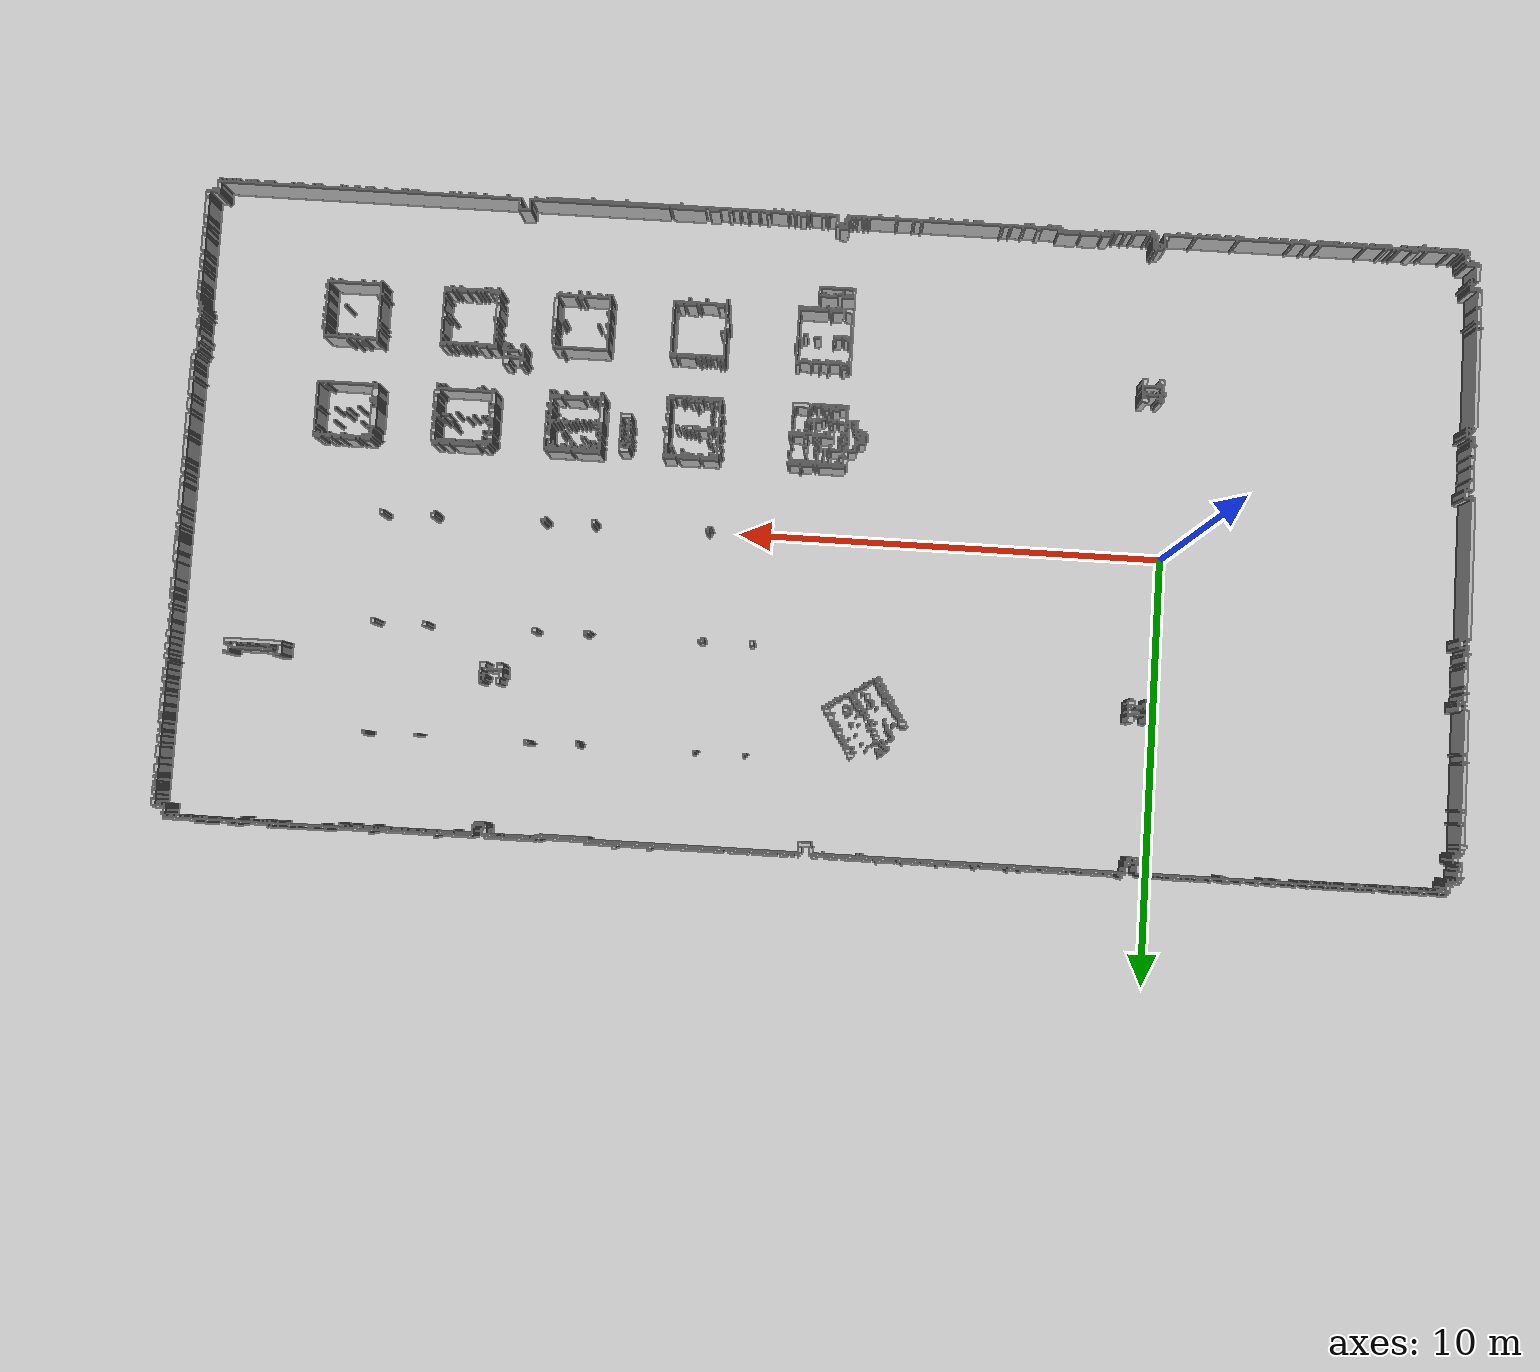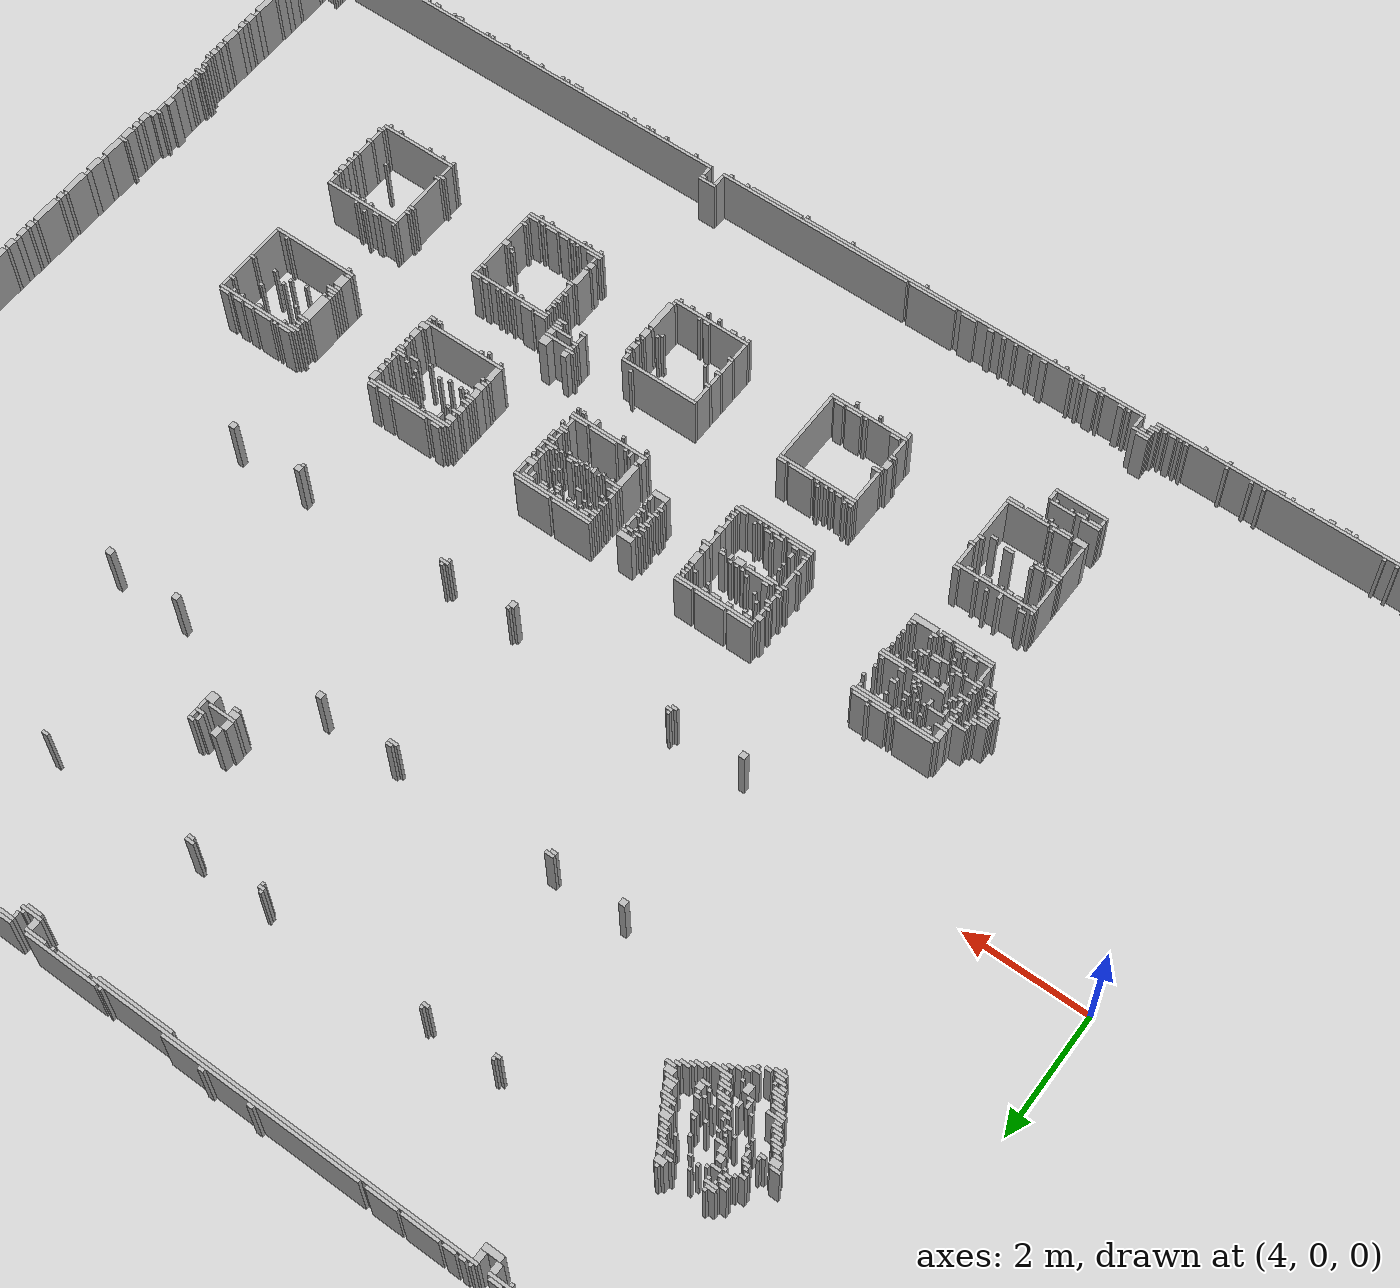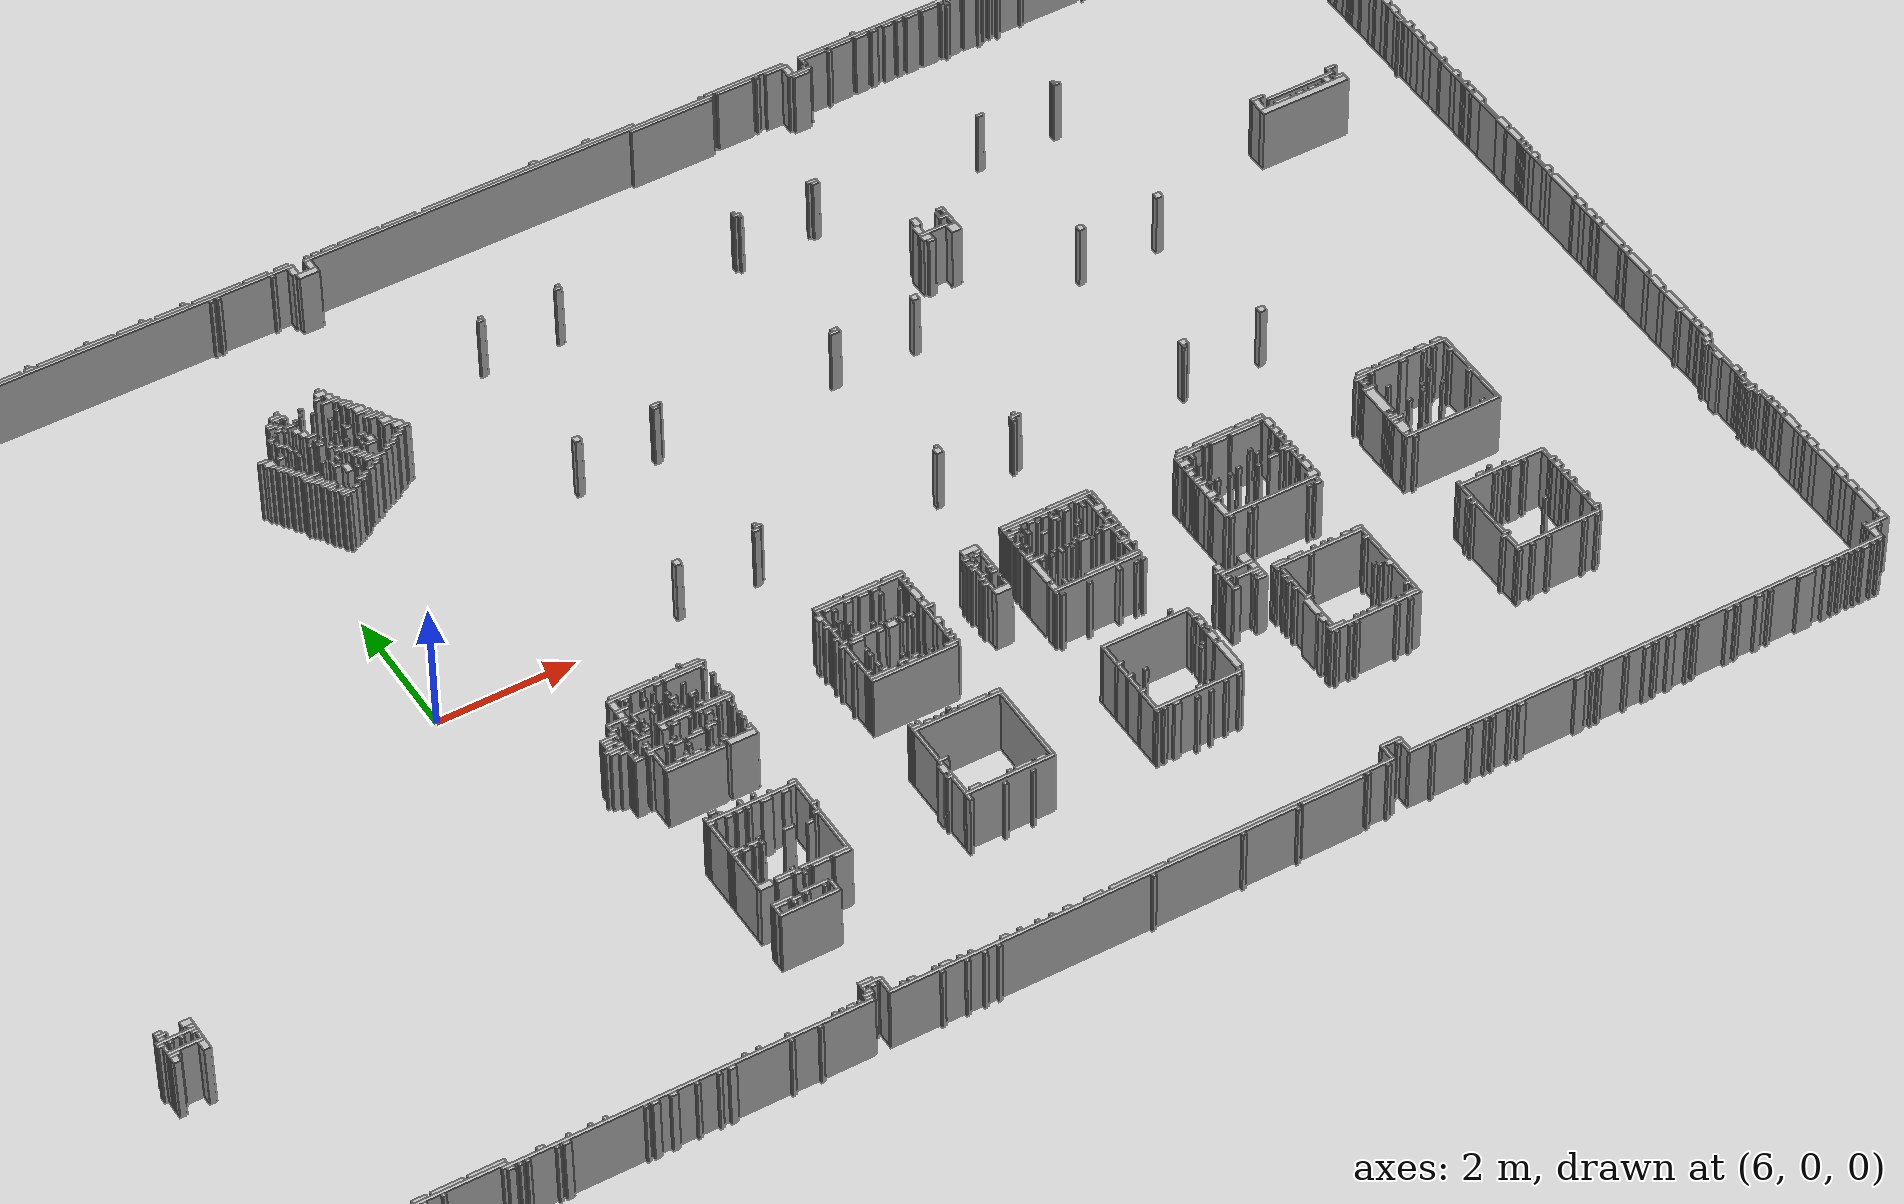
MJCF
<mujoco model="depot">
  <!-- Extruded from the map depot by artefacts_toolkit_navigation.map_to_world -->
  <compiler angle="degree"/>
  <option gravity="0 0 -9.81"/>
  <worldbody>
    <light pos="0 0 10" dir="-0.5 0.1 -0.9" directional="true"/>
    <geom name="ground" type="plane" size="50 50 0.1" rgba="0.8 0.8 0.8 1"/>
    <geom name="wall_0" type="box" pos="0.735 7.495 0.5" size="0.025 0.025 0.5" euler="0 0 0.0" rgba="0.7 0.7 0.7 1"/>
    <geom name="wall_1" type="box" pos="3.035 7.495 0.5" size="0.025 0.025 0.5" euler="0 0 0.0" rgba="0.7 0.7 0.7 1"/>
    <geom name="wall_2" type="box" pos="3.335 7.495 0.5" size="0.025 0.025 0.5" euler="0 0 0.0" rgba="0.7 0.7 0.7 1"/>
    <geom name="wall_3" type="box" pos="4.085 7.495 0.5" size="0.025 0.025 0.5" euler="0 0 0.0" rgba="0.7 0.7 0.7 1"/>
    <geom name="wall_4" type="box" pos="4.935 7.495 0.5" size="0.025 0.025 0.5" euler="0 0 0.0" rgba="0.7 0.7 0.7 1"/>
    <geom name="wall_5" type="box" pos="5.735 7.495 0.5" size="0.025 0.025 0.5" euler="0 0 0.0" rgba="0.7 0.7 0.7 1"/>
    <geom name="wall_6" type="box" pos="6.335 7.495 0.5" size="0.025 0.025 0.5" euler="0 0 0.0" rgba="0.7 0.7 0.7 1"/>
    <geom name="wall_7" type="box" pos="11.56 7.495 0.5" size="0.05 0.025 0.5" euler="0 0 0.0" rgba="0.7 0.7 0.7 1"/>
    <geom name="wall_8" type="box" pos="12.36 7.495 0.5" size="0.05 0.025 0.5" euler="0 0 0.0" rgba="0.7 0.7 0.7 1"/>
    <geom name="wall_9" type="box" pos="16.485 7.495 0.5" size="0.025 0.025 0.5" euler="0 0 0.0" rgba="0.7 0.7 0.7 1"/>
    <geom name="wall_10" type="box" pos="17.985 7.495 0.5" size="0.025 0.025 0.5" euler="0 0 0.0" rgba="0.7 0.7 0.7 1"/>
    <geom name="wall_11" type="box" pos="18.985 7.495 0.5" size="0.025 0.025 0.5" euler="0 0 0.0" rgba="0.7 0.7 0.7 1"/>
    <geom name="wall_12" type="box" pos="19.335 7.495 0.5" size="0.075 0.025 0.5" euler="0 0 0.0" rgba="0.7 0.7 0.7 1"/>
    <geom name="wall_13" type="box" pos="19.635 7.495 0.5" size="0.025 0.025 0.5" euler="0 0 0.0" rgba="0.7 0.7 0.7 1"/>
    <geom name="wall_14" type="box" pos="19.835 7.495 0.5" size="0.025 0.025 0.5" euler="0 0 0.0" rgba="0.7 0.7 0.7 1"/>
    <geom name="wall_15" type="box" pos="20.085 7.495 0.5" size="0.025 0.025 0.5" euler="0 0 0.0" rgba="0.7 0.7 0.7 1"/>
    <geom name="wall_16" type="box" pos="20.235 7.495 0.5" size="0.025 0.025 0.5" euler="0 0 0.0" rgba="0.7 0.7 0.7 1"/>
    <geom name="wall_17" type="box" pos="20.335 7.495 0.5" size="0.025 0.025 0.5" euler="0 0 0.0" rgba="0.7 0.7 0.7 1"/>
    <geom name="wall_18" type="box" pos="21.035 7.495 0.5" size="0.025 0.025 0.5" euler="0 0 0.0" rgba="0.7 0.7 0.7 1"/>
    <geom name="wall_19" type="box" pos="21.21 7.495 0.5" size="0.05 0.025 0.5" euler="0 0 0.0" rgba="0.7 0.7 0.7 1"/>
    <geom name="wall_20" type="box" pos="21.735 7.495 0.5" size="0.025 0.025 0.5" euler="0 0 0.0" rgba="0.7 0.7 0.7 1"/>
    <geom name="wall_21" type="box" pos="21.985 7.495 0.5" size="0.025 0.025 0.5" euler="0 0 0.0" rgba="0.7 0.7 0.7 1"/>
    <geom name="wall_22" type="box" pos="-6.715 7.445 0.5" size="0.025 0.025 0.5" euler="0 0 0.0" rgba="0.7 0.7 0.7 1"/>
    <geom name="wall_23" type="box" pos="-6.565 7.445 0.5" size="0.025 0.025 0.5" euler="0 0 0.0" rgba="0.7 0.7 0.7 1"/>
    <geom name="wall_24" type="box" pos="-6.265 7.445 0.5" size="0.025 0.025 0.5" euler="0 0 0.0" rgba="0.7 0.7 0.7 1"/>
    <geom name="wall_25" type="box" pos="-6.14 7.445 0.5" size="0.05 0.025 0.5" euler="0 0 0.0" rgba="0.7 0.7 0.7 1"/>
    <geom name="wall_26" type="box" pos="-5.865 7.445 0.5" size="0.025 0.025 0.5" euler="0 0 0.0" rgba="0.7 0.7 0.7 1"/>
    <geom name="wall_27" type="box" pos="-5.765 7.445 0.5" size="0.025 0.025 0.5" euler="0 0 0.0" rgba="0.7 0.7 0.7 1"/>
    <geom name="wall_28" type="box" pos="-5.665 7.445 0.5" size="0.025 0.025 0.5" euler="0 0 0.0" rgba="0.7 0.7 0.7 1"/>
    <geom name="wall_29" type="box" pos="-5.565 7.445 0.5" size="0.025 0.025 0.5" euler="0 0 0.0" rgba="0.7 0.7 0.7 1"/>
    <geom name="wall_30" type="box" pos="-5.465 7.445 0.5" size="0.025 0.025 0.5" euler="0 0 0.0" rgba="0.7 0.7 0.7 1"/>
    <geom name="wall_31" type="box" pos="-5.065 7.445 0.5" size="0.025 0.025 0.5" euler="0 0 0.0" rgba="0.7 0.7 0.7 1"/>
    <geom name="wall_32" type="box" pos="-4.865 7.445 0.5" size="0.025 0.025 0.5" euler="0 0 0.0" rgba="0.7 0.7 0.7 1"/>
    <geom name="wall_33" type="box" pos="-4.765 7.445 0.5" size="0.025 0.025 0.5" euler="0 0 0.0" rgba="0.7 0.7 0.7 1"/>
    <geom name="wall_34" type="box" pos="-4.665 7.445 0.5" size="0.025 0.025 0.5" euler="0 0 0.0" rgba="0.7 0.7 0.7 1"/>
    <geom name="wall_35" type="box" pos="-4.44 7.445 0.5" size="0.05 0.025 0.5" euler="0 0 0.0" rgba="0.7 0.7 0.7 1"/>
    <geom name="wall_36" type="box" pos="-4.265 7.445 0.5" size="0.025 0.025 0.5" euler="0 0 0.0" rgba="0.7 0.7 0.7 1"/>
    <geom name="wall_37" type="box" pos="-4.065 7.445 0.5" size="0.025 0.025 0.5" euler="0 0 0.0" rgba="0.7 0.7 0.7 1"/>
    <geom name="wall_38" type="box" pos="-3.965 7.445 0.5" size="0.025 0.025 0.5" euler="0 0 0.0" rgba="0.7 0.7 0.7 1"/>
    <geom name="wall_39" type="box" pos="-3.765 7.445 0.5" size="0.025 0.025 0.5" euler="0 0 0.0" rgba="0.7 0.7 0.7 1"/>
    <geom name="wall_40" type="box" pos="-3.565 7.445 0.5" size="0.025 0.025 0.5" euler="0 0 0.0" rgba="0.7 0.7 0.7 1"/>
    <geom name="wall_41" type="box" pos="-3.265 7.445 0.5" size="0.025 0.025 0.5" euler="0 0 0.0" rgba="0.7 0.7 0.7 1"/>
    <geom name="wall_42" type="box" pos="-3.065 7.445 0.5" size="0.025 0.025 0.5" euler="0 0 0.0" rgba="0.7 0.7 0.7 1"/>
    <geom name="wall_43" type="box" pos="-2.765 7.445 0.5" size="0.075 0.025 0.5" euler="0 0 0.0" rgba="0.7 0.7 0.7 1"/>
    <geom name="wall_44" type="box" pos="-2.39 7.445 0.5" size="0.05 0.025 0.5" euler="0 0 0.0" rgba="0.7 0.7 0.7 1"/>
    <geom name="wall_45" type="box" pos="-2.015 7.445 0.5" size="0.025 0.025 0.5" euler="0 0 0.0" rgba="0.7 0.7 0.7 1"/>
    <geom name="wall_46" type="box" pos="-1.69 7.445 0.5" size="0.1 0.025 0.5" euler="0 0 0.0" rgba="0.7 0.7 0.7 1"/>
    <geom name="wall_47" type="box" pos="-1.315 7.445 0.5" size="0.025 0.025 0.5" euler="0 0 0.0" rgba="0.7 0.7 0.7 1"/>
    <geom name="wall_48" type="box" pos="-1.09 7.445 0.5" size="0.1 0.025 0.5" euler="0 0 0.0" rgba="0.7 0.7 0.7 1"/>
    <geom name="wall_49" type="box" pos="-0.865 7.445 0.5" size="0.025 0.025 0.5" euler="0 0 0.0" rgba="0.7 0.7 0.7 1"/>
    <geom name="wall_50" type="box" pos="-0.715 7.445 0.5" size="0.025 0.025 0.5" euler="0 0 0.0" rgba="0.7 0.7 0.7 1"/>
    <geom name="wall_51" type="box" pos="-0.515 7.445 0.5" size="0.125 0.025 0.5" euler="0 0 0.0" rgba="0.7 0.7 0.7 1"/>
    <geom name="wall_52" type="box" pos="-0.265 7.445 0.5" size="0.025 0.025 0.5" euler="0 0 0.0" rgba="0.7 0.7 0.7 1"/>
    <geom name="wall_53" type="box" pos="-0.065 7.445 0.5" size="0.025 0.025 0.5" euler="0 0 0.0" rgba="0.7 0.7 0.7 1"/>
    <geom name="wall_54" type="box" pos="0.035 7.445 0.5" size="0.025 0.025 0.5" euler="0 0 0.0" rgba="0.7 0.7 0.7 1"/>
    <geom name="wall_55" type="box" pos="0.135 7.445 0.5" size="0.025 0.025 0.5" euler="0 0 0.0" rgba="0.7 0.7 0.7 1"/>
    <geom name="wall_56" type="box" pos="0.285 7.445 0.5" size="0.025 0.025 0.5" euler="0 0 0.0" rgba="0.7 0.7 0.7 1"/>
    <geom name="wall_57" type="box" pos="0.76 7.445 0.5" size="0.05 0.025 0.5" euler="0 0 0.0" rgba="0.7 0.7 0.7 1"/>
    <geom name="wall_58" type="box" pos="1.01 7.445 0.5" size="0.1 0.025 0.5" euler="0 0 0.0" rgba="0.7 0.7 0.7 1"/>
    <geom name="wall_59" type="box" pos="1.385 7.445 0.5" size="0.225 0.025 0.5" euler="0 0 0.0" rgba="0.7 0.7 0.7 1"/>
    <geom name="wall_60" type="box" pos="1.71 7.445 0.5" size="0.05 0.025 0.5" euler="0 0 0.0" rgba="0.7 0.7 0.7 1"/>
    <geom name="wall_61" type="box" pos="1.935 7.445 0.5" size="0.025 0.025 0.5" euler="0 0 0.0" rgba="0.7 0.7 0.7 1"/>
    <geom name="wall_62" type="box" pos="2.285 7.445 0.5" size="0.275 0.025 0.5" euler="0 0 0.0" rgba="0.7 0.7 0.7 1"/>
    <geom name="wall_63" type="box" pos="2.985 7.445 0.5" size="0.325 0.025 0.5" euler="0 0 0.0" rgba="0.7 0.7 0.7 1"/>
    <geom name="wall_64" type="box" pos="3.66 7.445 0.5" size="0.3 0.025 0.5" euler="0 0 0.0" rgba="0.7 0.7 0.7 1"/>
    <geom name="wall_65" type="box" pos="4.085 7.445 0.5" size="0.075 0.025 0.5" euler="0 0 0.0" rgba="0.7 0.7 0.7 1"/>
    <geom name="wall_66" type="box" pos="4.46 7.445 0.5" size="0.25 0.025 0.5" euler="0 0 0.0" rgba="0.7 0.7 0.7 1"/>
    <geom name="wall_67" type="box" pos="5.035 7.445 0.5" size="0.275 0.025 0.5" euler="0 0 0.0" rgba="0.7 0.7 0.7 1"/>
    <geom name="wall_68" type="box" pos="5.61 7.445 0.5" size="0.25 0.025 0.5" euler="0 0 0.0" rgba="0.7 0.7 0.7 1"/>
    <geom name="wall_69" type="box" pos="6.16 7.445 0.5" size="0.25 0.025 0.5" euler="0 0 0.0" rgba="0.7 0.7 0.7 1"/>
    <geom name="wall_70" type="box" pos="6.81 7.445 0.5" size="0.35 0.025 0.5" euler="0 0 0.0" rgba="0.7 0.7 0.7 1"/>
    <geom name="wall_71" type="box" pos="7.385 7.445 0.5" size="0.175 0.025 0.5" euler="0 0 0.0" rgba="0.7 0.7 0.7 1"/>
    <geom name="wall_72" type="box" pos="7.76 7.445 0.5" size="0.1 0.025 0.5" euler="0 0 0.0" rgba="0.7 0.7 0.7 1"/>
    <geom name="wall_73" type="box" pos="8.135 7.445 0.5" size="0.025 0.025 0.5" euler="0 0 0.0" rgba="0.7 0.7 0.7 1"/>
    <geom name="wall_74" type="box" pos="8.26 7.445 0.5" size="0.05 0.025 0.5" euler="0 0 0.0" rgba="0.7 0.7 0.7 1"/>
    <geom name="wall_75" type="box" pos="8.46 7.445 0.5" size="0.1 0.025 0.5" euler="0 0 0.0" rgba="0.7 0.7 0.7 1"/>
    <geom name="wall_76" type="box" pos="8.91 7.445 0.5" size="0.3 0.025 0.5" euler="0 0 0.0" rgba="0.7 0.7 0.7 1"/>
    <geom name="wall_77" type="box" pos="9.51 7.445 0.5" size="0.25 0.025 0.5" euler="0 0 0.0" rgba="0.7 0.7 0.7 1"/>
    <geom name="wall_78" type="box" pos="11.46 7.445 0.5" size="1.6 0.025 0.5" euler="0 0 0.0" rgba="0.7 0.7 0.7 1"/>
    <geom name="wall_79" type="box" pos="14.085 7.445 0.5" size="0.025 0.025 0.5" euler="0 0 0.0" rgba="0.7 0.7 0.7 1"/>
    <geom name="wall_80" type="box" pos="14.76 7.445 0.5" size="0.6 0.025 0.5" euler="0 0 0.0" rgba="0.7 0.7 0.7 1"/>
    <geom name="wall_81" type="box" pos="19.185 7.445 0.5" size="3.575 0.025 0.5" euler="0 0 0.0" rgba="0.7 0.7 0.7 1"/>
    <geom name="wall_82" type="box" pos="-3.19 7.395 0.5" size="3.6 0.025 0.5" euler="0 0 0.0" rgba="0.7 0.7 0.7 1"/>
    <geom name="wall_83" type="box" pos="4.26 7.395 0.5" size="3.65 0.025 0.5" euler="0 0 0.0" rgba="0.7 0.7 0.7 1"/>
    <geom name="wall_84" type="box" pos="11.16 7.395 0.5" size="3.1 0.025 0.5" euler="0 0 0.0" rgba="0.7 0.7 0.7 1"/>
    <geom name="wall_85" type="box" pos="14.585 7.395 0.5" size="0.275 0.025 0.5" euler="0 0 0.0" rgba="0.7 0.7 0.7 1"/>
    <geom name="wall_86" type="box" pos="14.935 7.395 0.5" size="0.025 0.025 0.5" euler="0 0 0.0" rgba="0.7 0.7 0.7 1"/>
    <geom name="wall_87" type="box" pos="15.235 7.395 0.5" size="0.175 0.025 0.5" euler="0 0 0.0" rgba="0.7 0.7 0.7 1"/>
    <geom name="wall_88" type="box" pos="15.81 7.395 0.5" size="0.2 0.025 0.5" euler="0 0 0.0" rgba="0.7 0.7 0.7 1"/>
    <geom name="wall_89" type="box" pos="16.235 7.395 0.5" size="0.175 0.025 0.5" euler="0 0 0.0" rgba="0.7 0.7 0.7 1"/>
    <geom name="wall_90" type="box" pos="16.56 7.395 0.5" size="0.1 0.025 0.5" euler="0 0 0.0" rgba="0.7 0.7 0.7 1"/>
    <geom name="wall_91" type="box" pos="16.76 7.395 0.5" size="0.05 0.025 0.5" euler="0 0 0.0" rgba="0.7 0.7 0.7 1"/>
    <geom name="wall_92" type="box" pos="16.985 7.395 0.5" size="0.075 0.025 0.5" euler="0 0 0.0" rgba="0.7 0.7 0.7 1"/>
    <geom name="wall_93" type="box" pos="17.16 7.395 0.5" size="0.05 0.025 0.5" euler="0 0 0.0" rgba="0.7 0.7 0.7 1"/>
    <geom name="wall_94" type="box" pos="17.36 7.395 0.5" size="0.1 0.025 0.5" euler="0 0 0.0" rgba="0.7 0.7 0.7 1"/>
    <geom name="wall_95" type="box" pos="17.635 7.395 0.5" size="0.125 0.025 0.5" euler="0 0 0.0" rgba="0.7 0.7 0.7 1"/>
    <geom name="wall_96" type="box" pos="17.835 7.395 0.5" size="0.025 0.025 0.5" euler="0 0 0.0" rgba="0.7 0.7 0.7 1"/>
    <geom name="wall_97" type="box" pos="18.01 7.395 0.5" size="0.1 0.025 0.5" euler="0 0 0.0" rgba="0.7 0.7 0.7 1"/>
    <geom name="wall_98" type="box" pos="18.26 7.395 0.5" size="0.1 0.025 0.5" euler="0 0 0.0" rgba="0.7 0.7 0.7 1"/>
    <geom name="wall_99" type="box" pos="18.485 7.395 0.5" size="0.025 0.025 0.5" euler="0 0 0.0" rgba="0.7 0.7 0.7 1"/>
    <geom name="wall_100" type="box" pos="18.585 7.395 0.5" size="0.025 0.025 0.5" euler="0 0 0.0" rgba="0.7 0.7 0.7 1"/>
    <geom name="wall_101" type="box" pos="19.085 7.395 0.5" size="0.025 0.025 0.5" euler="0 0 0.0" rgba="0.7 0.7 0.7 1"/>
    <geom name="wall_102" type="box" pos="20.085 7.395 0.5" size="0.025 0.025 0.5" euler="0 0 0.0" rgba="0.7 0.7 0.7 1"/>
    <geom name="wall_103" type="box" pos="20.285 7.395 0.5" size="0.025 0.025 0.5" euler="0 0 0.0" rgba="0.7 0.7 0.7 1"/>
    <geom name="wall_104" type="box" pos="20.385 7.395 0.5" size="0.025 0.025 0.5" euler="0 0 0.0" rgba="0.7 0.7 0.7 1"/>
    <geom name="wall_105" type="box" pos="20.485 7.395 0.5" size="0.025 0.025 0.5" euler="0 0 0.0" rgba="0.7 0.7 0.7 1"/>
    <geom name="wall_106" type="box" pos="20.685 7.395 0.5" size="0.025 0.025 0.5" euler="0 0 0.0" rgba="0.7 0.7 0.7 1"/>
    <geom name="wall_107" type="box" pos="21.035 7.395 0.5" size="0.025 0.025 0.5" euler="0 0 0.0" rgba="0.7 0.7 0.7 1"/>
    <geom name="wall_108" type="box" pos="21.435 7.395 0.5" size="0.025 0.025 0.5" euler="0 0 0.0" rgba="0.7 0.7 0.7 1"/>
    <geom name="wall_109" type="box" pos="21.76 7.395 0.5" size="0.05 0.025 0.5" euler="0 0 0.0" rgba="0.7 0.7 0.7 1"/>
    <geom name="wall_110" type="box" pos="21.885 7.395 0.5" size="0.025 0.025 0.5" euler="0 0 0.0" rgba="0.7 0.7 0.7 1"/>
    <geom name="wall_111" type="box" pos="22.085 7.395 0.5" size="0.025 0.025 0.5" euler="0 0 0.0" rgba="0.7 0.7 0.7 1"/>
    <geom name="wall_112" type="box" pos="22.285 7.395 0.5" size="0.025 0.025 0.5" euler="0 0 0.0" rgba="0.7 0.7 0.7 1"/>
    <geom name="wall_113" type="box" pos="22.41 7.395 0.5" size="0.05 0.025 0.5" euler="0 0 0.0" rgba="0.7 0.7 0.7 1"/>
    <geom name="wall_114" type="box" pos="22.56 7.395 0.5" size="0.05 0.025 0.5" euler="0 0 0.0" rgba="0.7 0.7 0.7 1"/>
    <geom name="wall_115" type="box" pos="22.71 7.395 0.5" size="0.05 0.025 0.5" euler="0 0 0.0" rgba="0.7 0.7 0.7 1"/>
    <geom name="wall_116" type="box" pos="-6.64 7.345 0.5" size="0.15 0.025 0.5" euler="0 0 0.0" rgba="0.7 0.7 0.7 1"/>
    <geom name="wall_117" type="box" pos="-6.365 7.345 0.5" size="0.025 0.025 0.5" euler="0 0 0.0" rgba="0.7 0.7 0.7 1"/>
    <geom name="wall_118" type="box" pos="-6.215 7.345 0.5" size="0.025 0.025 0.5" euler="0 0 0.0" rgba="0.7 0.7 0.7 1"/>
    <geom name="wall_119" type="box" pos="-5.99 7.345 0.5" size="0.1 0.025 0.5" euler="0 0 0.0" rgba="0.7 0.7 0.7 1"/>
    <geom name="wall_120" type="box" pos="-5.815 7.345 0.5" size="0.025 0.025 0.5" euler="0 0 0.0" rgba="0.7 0.7 0.7 1"/>
    <geom name="wall_121" type="box" pos="-5.615 7.345 0.5" size="0.075 0.025 0.5" euler="0 0 0.0" rgba="0.7 0.7 0.7 1"/>
    <geom name="wall_122" type="box" pos="-5.415 7.345 0.5" size="0.075 0.025 0.5" euler="0 0 0.0" rgba="0.7 0.7 0.7 1"/>
    <geom name="wall_123" type="box" pos="-5.265 7.345 0.5" size="0.025 0.025 0.5" euler="0 0 0.0" rgba="0.7 0.7 0.7 1"/>
    <geom name="wall_124" type="box" pos="-5.165 7.345 0.5" size="0.025 0.025 0.5" euler="0 0 0.0" rgba="0.7 0.7 0.7 1"/>
    <geom name="wall_125" type="box" pos="-4.915 7.345 0.5" size="0.025 0.025 0.5" euler="0 0 0.0" rgba="0.7 0.7 0.7 1"/>
    <geom name="wall_126" type="box" pos="-4.765 7.345 0.5" size="0.075 0.025 0.5" euler="0 0 0.0" rgba="0.7 0.7 0.7 1"/>
    <geom name="wall_127" type="box" pos="-4.465 7.345 0.5" size="0.075 0.025 0.5" euler="0 0 0.0" rgba="0.7 0.7 0.7 1"/>
    <geom name="wall_128" type="box" pos="-4.115 7.345 0.5" size="0.025 0.025 0.5" euler="0 0 0.0" rgba="0.7 0.7 0.7 1"/>
    <geom name="wall_129" type="box" pos="-4.015 7.345 0.5" size="0.025 0.025 0.5" euler="0 0 0.0" rgba="0.7 0.7 0.7 1"/>
    <geom name="wall_130" type="box" pos="-3.865 7.345 0.5" size="0.025 0.025 0.5" euler="0 0 0.0" rgba="0.7 0.7 0.7 1"/>
    <geom name="wall_131" type="box" pos="-3.64 7.345 0.5" size="0.05 0.025 0.5" euler="0 0 0.0" rgba="0.7 0.7 0.7 1"/>
    <geom name="wall_132" type="box" pos="-3.365 7.345 0.5" size="0.025 0.025 0.5" euler="0 0 0.0" rgba="0.7 0.7 0.7 1"/>
    <geom name="wall_133" type="box" pos="-2.865 7.345 0.5" size="0.025 0.025 0.5" euler="0 0 0.0" rgba="0.7 0.7 0.7 1"/>
    <geom name="wall_134" type="box" pos="-2.59 7.345 0.5" size="0.05 0.025 0.5" euler="0 0 0.0" rgba="0.7 0.7 0.7 1"/>
    <geom name="wall_135" type="box" pos="-1.59 7.345 0.5" size="0.05 0.025 0.5" euler="0 0 0.0" rgba="0.7 0.7 0.7 1"/>
    <geom name="wall_136" type="box" pos="0.36 7.27 0.5" size="0.05 0.1 0.5" euler="0 0 0.0" rgba="0.7 0.7 0.7 1"/>
    <geom name="wall_137" type="box" pos="0.61 7.295 0.5" size="0.05 0.075 0.5" euler="0 0 0.0" rgba="0.7 0.7 0.7 1"/>
    <geom name="wall_138" type="box" pos="6.685 7.345 0.5" size="0.025 0.025 0.5" euler="0 0 0.0" rgba="0.7 0.7 0.7 1"/>
    <geom name="wall_139" type="box" pos="6.785 7.345 0.5" size="0.025 0.025 0.5" euler="0 0 0.0" rgba="0.7 0.7 0.7 1"/>
    <geom name="wall_140" type="box" pos="7.585 7.345 0.5" size="0.025 0.025 0.5" euler="0 0 0.0" rgba="0.7 0.7 0.7 1"/>
    <geom name="wall_141" type="box" pos="7.86 7.295 0.5" size="0.05 0.075 0.5" euler="0 0 0.0" rgba="0.7 0.7 0.7 1"/>
    <geom name="wall_142" type="box" pos="8.11 7.295 0.5" size="0.05 0.075 0.5" euler="0 0 0.0" rgba="0.7 0.7 0.7 1"/>
    <geom name="wall_143" type="box" pos="13.585 7.345 0.5" size="0.625 0.025 0.5" euler="0 0 0.0" rgba="0.7 0.7 0.7 1"/>
    <geom name="wall_144" type="box" pos="15.36 7.295 0.5" size="0.05 0.075 0.5" euler="0 0 0.0" rgba="0.7 0.7 0.7 1"/>
    <geom name="wall_145" type="box" pos="15.635 7.32 0.5" size="0.025 0.05 0.5" euler="0 0 0.0" rgba="0.7 0.7 0.7 1"/>
    <geom name="wall_146" type="box" pos="16.035 7.345 0.5" size="0.025 0.025 0.5" euler="0 0 0.0" rgba="0.7 0.7 0.7 1"/>
    <geom name="wall_147" type="box" pos="17.885 7.345 0.5" size="0.025 0.025 0.5" euler="0 0 0.0" rgba="0.7 0.7 0.7 1"/>
    <geom name="wall_148" type="box" pos="18.385 7.345 0.5" size="0.025 0.025 0.5" euler="0 0 0.0" rgba="0.7 0.7 0.7 1"/>
    <geom name="wall_149" type="box" pos="18.685 7.345 0.5" size="0.025 0.025 0.5" euler="0 0 0.0" rgba="0.7 0.7 0.7 1"/>
    <geom name="wall_150" type="box" pos="20.935 7.345 0.5" size="0.025 0.025 0.5" euler="0 0 0.0" rgba="0.7 0.7 0.7 1"/>
    <geom name="wall_151" type="box" pos="22.76 7.345 0.5" size="0.05 0.025 0.5" euler="0 0 0.0" rgba="0.7 0.7 0.7 1"/>
    <geom name="wall_152" type="box" pos="-6.74 7.27 0.5" size="0.05 0.05 0.5" euler="0 0 0.0" rgba="0.7 0.7 0.7 1"/>
    <geom name="wall_153" type="box" pos="22.735 7.27 0.5" size="0.025 0.05 0.5" euler="0 0 0.0" rgba="0.7 0.7 0.7 1"/>
    <geom name="wall_154" type="box" pos="15.585 7.245 0.5" size="0.025 0.025 0.5" euler="0 0 0.0" rgba="0.7 0.7 0.7 1"/>
    <geom name="wall_155" type="box" pos="-6.79 7.195 0.5" size="0.1 0.025 0.5" euler="0 0 0.0" rgba="0.7 0.7 0.7 1"/>
    <geom name="wall_156" type="box" pos="0.585 7.195 0.5" size="0.075 0.025 0.5" euler="0 0 0.0" rgba="0.7 0.7 0.7 1"/>
    <geom name="wall_157" type="box" pos="8.01 7.17 0.5" size="0.15 0.05 0.5" euler="0 0 0.0" rgba="0.7 0.7 0.7 1"/>
    <geom name="wall_158" type="box" pos="15.485 7.195 0.5" size="0.175 0.025 0.5" euler="0 0 0.0" rgba="0.7 0.7 0.7 1"/>
    <geom name="wall_159" type="box" pos="22.86 7.195 0.5" size="0.15 0.025 0.5" euler="0 0 0.0" rgba="0.7 0.7 0.7 1"/>
    <geom name="wall_160" type="box" pos="-6.89 7.145 0.5" size="0.15 0.025 0.5" euler="0 0 0.0" rgba="0.7 0.7 0.7 1"/>
    <geom name="wall_161" type="box" pos="0.485 7.145 0.5" size="0.175 0.025 0.5" euler="0 0 0.0" rgba="0.7 0.7 0.7 1"/>
    <geom name="wall_162" type="box" pos="15.485 7.145 0.5" size="0.125 0.025 0.5" euler="0 0 0.0" rgba="0.7 0.7 0.7 1"/>
    <geom name="wall_163" type="box" pos="22.735 7.145 0.5" size="0.025 0.025 0.5" euler="0 0 0.0" rgba="0.7 0.7 0.7 1"/>
    <geom name="wall_164" type="box" pos="22.835 7.145 0.5" size="0.025 0.025 0.5" euler="0 0 0.0" rgba="0.7 0.7 0.7 1"/>
    <geom name="wall_165" type="box" pos="23.01 7.095 0.5" size="0.05 0.075 0.5" euler="0 0 0.0" rgba="0.7 0.7 0.7 1"/>
    <geom name="wall_166" type="box" pos="-6.99 7.095 0.5" size="0.05 0.025 0.5" euler="0 0 0.0" rgba="0.7 0.7 0.7 1"/>
    <geom name="wall_167" type="box" pos="-6.865 7.095 0.5" size="0.025 0.025 0.5" euler="0 0 0.0" rgba="0.7 0.7 0.7 1"/>
    <geom name="wall_168" type="box" pos="-6.765 7.095 0.5" size="0.025 0.025 0.5" euler="0 0 0.0" rgba="0.7 0.7 0.7 1"/>
    <geom name="wall_169" type="box" pos="0.41 7.095 0.5" size="0.05 0.025 0.5" euler="0 0 0.0" rgba="0.7 0.7 0.7 1"/>
    <geom name="wall_170" type="box" pos="0.56 7.095 0.5" size="0.05 0.025 0.5" euler="0 0 0.0" rgba="0.7 0.7 0.7 1"/>
    <geom name="wall_171" type="box" pos="-7.015 7.045 0.5" size="0.075 0.025 0.5" euler="0 0 0.0" rgba="0.7 0.7 0.7 1"/>
    <geom name="wall_172" type="box" pos="0.485 7.045 0.5" size="0.125 0.025 0.5" euler="0 0 0.0" rgba="0.7 0.7 0.7 1"/>
    <geom name="wall_173" type="box" pos="-6.99 6.945 0.5" size="0.05 0.075 0.5" euler="0 0 0.0" rgba="0.7 0.7 0.7 1"/>
    <geom name="wall_174" type="box" pos="22.985 6.97 0.5" size="0.025 0.05 0.5" euler="0 0 0.0" rgba="0.7 0.7 0.7 1"/>
    <geom name="wall_175" type="box" pos="23.01 6.87 0.5" size="0.05 0.05 0.5" euler="0 0 0.0" rgba="0.7 0.7 0.7 1"/>
    <geom name="wall_176" type="box" pos="-7.015 6.82 0.5" size="0.025 0.05 0.5" euler="0 0 0.0" rgba="0.7 0.7 0.7 1"/>
    <geom name="wall_177" type="box" pos="22.985 6.795 0.5" size="0.025 0.025 0.5" euler="0 0 0.0" rgba="0.7 0.7 0.7 1"/>
    <geom name="wall_178" type="box" pos="-6.99 6.745 0.5" size="0.05 0.025 0.5" euler="0 0 0.0" rgba="0.7 0.7 0.7 1"/>
    <geom name="wall_179" type="box" pos="23.01 6.745 0.5" size="0.05 0.025 0.5" euler="0 0 0.0" rgba="0.7 0.7 0.7 1"/>
    <geom name="wall_180" type="box" pos="-7.015 6.695 0.5" size="0.025 0.025 0.5" euler="0 0 0.0" rgba="0.7 0.7 0.7 1"/>
    <geom name="wall_181" type="box" pos="-6.865 6.695 0.5" size="0.025 0.025 0.5" euler="0 0 0.0" rgba="0.7 0.7 0.7 1"/>
    <geom name="wall_182" type="box" pos="22.985 6.695 0.5" size="0.025 0.025 0.5" euler="0 0 0.0" rgba="0.7 0.7 0.7 1"/>
    <geom name="wall_183" type="box" pos="-6.89 6.62 0.5" size="0.05 0.05 0.5" euler="0 0 0.0" rgba="0.7 0.7 0.7 1"/>
    <geom name="wall_184" type="box" pos="23.01 6.645 0.5" size="0.05 0.025 0.5" euler="0 0 0.0" rgba="0.7 0.7 0.7 1"/>
    <geom name="wall_185" type="box" pos="22.985 6.57 0.5" size="0.025 0.05 0.5" euler="0 0 0.0" rgba="0.7 0.7 0.7 1"/>
    <geom name="wall_186" type="box" pos="-6.94 6.545 0.5" size="0.1 0.025 0.5" euler="0 0 0.0" rgba="0.7 0.7 0.7 1"/>
    <geom name="wall_187" type="box" pos="-6.99 6.495 0.5" size="0.1 0.025 0.5" euler="0 0 0.0" rgba="0.7 0.7 0.7 1"/>
    <geom name="wall_188" type="box" pos="23.01 6.495 0.5" size="0.05 0.025 0.5" euler="0 0 0.0" rgba="0.7 0.7 0.7 1"/>
    <geom name="wall_189" type="box" pos="-7.04 6.42 0.5" size="0.05 0.05 0.5" euler="0 0 0.0" rgba="0.7 0.7 0.7 1"/>
    <geom name="wall_190" type="box" pos="22.985 6.445 0.5" size="0.025 0.025 0.5" euler="0 0 0.0" rgba="0.7 0.7 0.7 1"/>
    <geom name="wall_191" type="box" pos="23.01 6.32 0.5" size="0.05 0.1 0.5" euler="0 0 0.0" rgba="0.7 0.7 0.7 1"/>
    <geom name="wall_192" type="box" pos="-7.065 6.32 0.5" size="0.075 0.05 0.5" euler="0 0 0.0" rgba="0.7 0.7 0.7 1"/>
    <geom name="wall_193" type="box" pos="-7.04 6.045 0.5" size="0.05 0.225 0.5" euler="0 0 0.0" rgba="0.7 0.7 0.7 1"/>
    <geom name="wall_194" type="box" pos="22.985 6.145 0.5" size="0.025 0.075 0.5" euler="0 0 0.0" rgba="0.7 0.7 0.7 1"/>
    <geom name="wall_195" type="box" pos="23.01 5.945 0.5" size="0.05 0.125 0.5" euler="0 0 0.0" rgba="0.7 0.7 0.7 1"/>
    <geom name="wall_196" type="box" pos="-7.015 5.795 0.5" size="0.075 0.025 0.5" euler="0 0 0.0" rgba="0.7 0.7 0.7 1"/>
    <geom name="wall_197" type="box" pos="22.985 5.77 0.5" size="0.025 0.05 0.5" euler="0 0 0.0" rgba="0.7 0.7 0.7 1"/>
    <geom name="wall_198" type="box" pos="-7.04 5.645 0.5" size="0.05 0.125 0.5" euler="0 0 0.0" rgba="0.7 0.7 0.7 1"/>
    <geom name="wall_199" type="box" pos="23.01 5.645 0.5" size="0.05 0.075 0.5" euler="0 0 0.0" rgba="0.7 0.7 0.7 1"/>
    <geom name="wall_200" type="box" pos="22.985 5.52 0.5" size="0.025 0.05 0.5" euler="0 0 0.0" rgba="0.7 0.7 0.7 1"/>
    <geom name="wall_201" type="box" pos="-7.015 5.495 0.5" size="0.075 0.025 0.5" euler="0 0 0.0" rgba="0.7 0.7 0.7 1"/>
    <geom name="wall_202" type="box" pos="-7.04 4.945 0.5" size="0.05 0.525 0.5" euler="0 0 0.0" rgba="0.7 0.7 0.7 1"/>
    <geom name="wall_203" type="box" pos="23.01 5.445 0.5" size="0.05 0.025 0.5" euler="0 0 0.0" rgba="0.7 0.7 0.7 1"/>
    <geom name="wall_204" type="box" pos="22.985 5.345 0.5" size="0.025 0.075 0.5" euler="0 0 0.0" rgba="0.7 0.7 0.7 1"/>
    <geom name="wall_205" type="box" pos="9.535 5.245 0.5" size="0.025 0.025 0.5" euler="0 0 0.0" rgba="0.7 0.7 0.7 1"/>
    <geom name="wall_206" type="box" pos="10.685 5.245 0.5" size="0.025 0.025 0.5" euler="0 0 0.0" rgba="0.7 0.7 0.7 1"/>
    <geom name="wall_207" type="box" pos="13.335 5.245 0.5" size="0.025 0.025 0.5" euler="0 0 0.0" rgba="0.7 0.7 0.7 1"/>
    <geom name="wall_208" type="box" pos="14.535 5.245 0.5" size="0.075 0.025 0.5" euler="0 0 0.0" rgba="0.7 0.7 0.7 1"/>
    <geom name="wall_209" type="box" pos="18.285 5.245 0.5" size="0.025 0.025 0.5" euler="0 0 0.0" rgba="0.7 0.7 0.7 1"/>
    <geom name="wall_210" type="box" pos="23.01 5.22 0.5" size="0.05 0.05 0.5" euler="0 0 0.0" rgba="0.7 0.7 0.7 1"/>
    <geom name="wall_211" type="box" pos="9.51 5.195 0.5" size="0.05 0.025 0.5" euler="0 0 0.0" rgba="0.7 0.7 0.7 1"/>
    <geom name="wall_212" type="box" pos="10.66 5.195 0.5" size="0.05 0.025 0.5" euler="0 0 0.0" rgba="0.7 0.7 0.7 1"/>
    <geom name="wall_213" type="box" pos="13.36 5.195 0.5" size="0.05 0.025 0.5" euler="0 0 0.0" rgba="0.7 0.7 0.7 1"/>
    <geom name="wall_214" type="box" pos="14.56 5.195 0.5" size="0.05 0.025 0.5" euler="0 0 0.0" rgba="0.7 0.7 0.7 1"/>
    <geom name="wall_215" type="box" pos="17.11 5.195 0.5" size="0.05 0.025 0.5" euler="0 0 0.0" rgba="0.7 0.7 0.7 1"/>
    <geom name="wall_216" type="box" pos="18.31 5.195 0.5" size="0.05 0.025 0.5" euler="0 0 0.0" rgba="0.7 0.7 0.7 1"/>
    <geom name="wall_217" type="box" pos="7.085 5.145 0.5" size="0.025 0.025 0.5" euler="0 0 0.0" rgba="0.7 0.7 0.7 1"/>
    <geom name="wall_218" type="box" pos="13.385 5.145 0.5" size="0.025 0.025 0.5" euler="0 0 0.0" rgba="0.7 0.7 0.7 1"/>
    <geom name="wall_219" type="box" pos="22.985 5.145 0.5" size="0.025 0.025 0.5" euler="0 0 0.0" rgba="0.7 0.7 0.7 1"/>
    <geom name="wall_220" type="box" pos="7.085 5.07 0.5" size="0.075 0.05 0.5" euler="0 0 0.0" rgba="0.7 0.7 0.7 1"/>
    <geom name="wall_221" type="box" pos="23.01 5.095 0.5" size="0.05 0.025 0.5" euler="0 0 0.0" rgba="0.7 0.7 0.7 1"/>
    <geom name="wall_222" type="box" pos="6.435 5.045 0.5" size="0.025 0.025 0.5" euler="0 0 0.0" rgba="0.7 0.7 0.7 1"/>
    <geom name="wall_223" type="box" pos="22.985 5.045 0.5" size="0.025 0.025 0.5" euler="0 0 0.0" rgba="0.7 0.7 0.7 1"/>
    <geom name="wall_224" type="box" pos="6.385 4.995 0.5" size="0.075 0.025 0.5" euler="0 0 0.0" rgba="0.7 0.7 0.7 1"/>
    <geom name="wall_225" type="box" pos="7.01 4.995 0.5" size="0.05 0.025 0.5" euler="0 0 0.0" rgba="0.7 0.7 0.7 1"/>
    <geom name="wall_226" type="box" pos="7.16 4.97 0.5" size="0.05 0.05 0.5" euler="0 0 0.0" rgba="0.7 0.7 0.7 1"/>
    <geom name="wall_227" type="box" pos="23.01 4.945 0.5" size="0.05 0.075 0.5" euler="0 0 0.0" rgba="0.7 0.7 0.7 1"/>
    <geom name="wall_228" type="box" pos="6.41 4.945 0.5" size="0.1 0.025 0.5" euler="0 0 0.0" rgba="0.7 0.7 0.7 1"/>
    <geom name="wall_229" type="box" pos="6.735 4.945 0.5" size="0.025 0.025 0.5" euler="0 0 0.0" rgba="0.7 0.7 0.7 1"/>
    <geom name="wall_230" type="box" pos="6.26 4.895 0.5" size="0.05 0.025 0.5" euler="0 0 0.0" rgba="0.7 0.7 0.7 1"/>
    <geom name="wall_231" type="box" pos="6.385 4.895 0.5" size="0.025 0.025 0.5" euler="0 0 0.0" rgba="0.7 0.7 0.7 1"/>
    <geom name="wall_232" type="box" pos="6.485 4.895 0.5" size="0.025 0.025 0.5" euler="0 0 0.0" rgba="0.7 0.7 0.7 1"/>
    <geom name="wall_233" type="box" pos="7.135 4.895 0.5" size="0.125 0.025 0.5" euler="0 0 0.0" rgba="0.7 0.7 0.7 1"/>
    <geom name="wall_234" type="box" pos="6.285 4.845 0.5" size="0.075 0.025 0.5" euler="0 0 0.0" rgba="0.7 0.7 0.7 1"/>
    <geom name="wall_235" type="box" pos="6.685 4.845 0.5" size="0.025 0.025 0.5" euler="0 0 0.0" rgba="0.7 0.7 0.7 1"/>
    <geom name="wall_236" type="box" pos="7.21 4.845 0.5" size="0.05 0.025 0.5" euler="0 0 0.0" rgba="0.7 0.7 0.7 1"/>
    <geom name="wall_237" type="box" pos="22.985 4.845 0.5" size="0.025 0.025 0.5" euler="0 0 0.0" rgba="0.7 0.7 0.7 1"/>
    <geom name="wall_238" type="box" pos="6.36 4.795 0.5" size="0.05 0.025 0.5" euler="0 0 0.0" rgba="0.7 0.7 0.7 1"/>
    <geom name="wall_239" type="box" pos="6.585 4.795 0.5" size="0.025 0.025 0.5" euler="0 0 0.0" rgba="0.7 0.7 0.7 1"/>
    <geom name="wall_240" type="box" pos="6.835 4.795 0.5" size="0.025 0.025 0.5" euler="0 0 0.0" rgba="0.7 0.7 0.7 1"/>
    <geom name="wall_241" type="box" pos="7.26 4.795 0.5" size="0.05 0.025 0.5" euler="0 0 0.0" rgba="0.7 0.7 0.7 1"/>
    <geom name="wall_242" type="box" pos="23.01 4.72 0.5" size="0.05 0.1 0.5" euler="0 0 0.0" rgba="0.7 0.7 0.7 1"/>
    <geom name="wall_243" type="box" pos="6.31 4.745 0.5" size="0.05 0.025 0.5" euler="0 0 0.0" rgba="0.7 0.7 0.7 1"/>
    <geom name="wall_244" type="box" pos="6.485 4.745 0.5" size="0.075 0.025 0.5" euler="0 0 0.0" rgba="0.7 0.7 0.7 1"/>
    <geom name="wall_245" type="box" pos="7.285 4.745 0.5" size="0.075 0.025 0.5" euler="0 0 0.0" rgba="0.7 0.7 0.7 1"/>
    <geom name="wall_246" type="box" pos="6.235 4.695 0.5" size="0.025 0.025 0.5" euler="0 0 0.0" rgba="0.7 0.7 0.7 1"/>
    <geom name="wall_247" type="box" pos="6.385 4.695 0.5" size="0.025 0.025 0.5" euler="0 0 0.0" rgba="0.7 0.7 0.7 1"/>
    <geom name="wall_248" type="box" pos="7.135 4.695 0.5" size="0.025 0.025 0.5" euler="0 0 0.0" rgba="0.7 0.7 0.7 1"/>
    <geom name="wall_249" type="box" pos="7.31 4.695 0.5" size="0.05 0.025 0.5" euler="0 0 0.0" rgba="0.7 0.7 0.7 1"/>
    <geom name="wall_250" type="box" pos="6.16 4.645 0.5" size="0.05 0.025 0.5" euler="0 0 0.0" rgba="0.7 0.7 0.7 1"/>
    <geom name="wall_251" type="box" pos="6.51 4.62 0.5" size="0.05 0.05 0.5" euler="0 0 0.0" rgba="0.7 0.7 0.7 1"/>
    <geom name="wall_252" type="box" pos="7.335 4.645 0.5" size="0.075 0.025 0.5" euler="0 0 0.0" rgba="0.7 0.7 0.7 1"/>
    <geom name="wall_253" type="box" pos="6.135 4.595 0.5" size="0.025 0.025 0.5" euler="0 0 0.0" rgba="0.7 0.7 0.7 1"/>
    <geom name="wall_254" type="box" pos="6.985 4.595 0.5" size="0.025 0.025 0.5" euler="0 0 0.0" rgba="0.7 0.7 0.7 1"/>
    <geom name="wall_255" type="box" pos="7.385 4.57 0.5" size="0.075 0.05 0.5" euler="0 0 0.0" rgba="0.7 0.7 0.7 1"/>
    <geom name="wall_256" type="box" pos="22.985 4.57 0.5" size="0.025 0.05 0.5" euler="0 0 0.0" rgba="0.7 0.7 0.7 1"/>
    <geom name="wall_257" type="box" pos="6.185 4.545 0.5" size="0.025 0.025 0.5" euler="0 0 0.0" rgba="0.7 0.7 0.7 1"/>
    <geom name="wall_258" type="box" pos="6.56 4.52 0.5" size="0.05 0.05 0.5" euler="0 0 0.0" rgba="0.7 0.7 0.7 1"/>
    <geom name="wall_259" type="box" pos="6.21 4.495 0.5" size="0.05 0.025 0.5" euler="0 0 0.0" rgba="0.7 0.7 0.7 1"/>
    <geom name="wall_260" type="box" pos="7.41 4.495 0.5" size="0.1 0.025 0.5" euler="0 0 0.0" rgba="0.7 0.7 0.7 1"/>
    <geom name="wall_261" type="box" pos="23.01 4.495 0.5" size="0.05 0.025 0.5" euler="0 0 0.0" rgba="0.7 0.7 0.7 1"/>
    <geom name="wall_262" type="box" pos="6.26 4.445 0.5" size="0.05 0.025 0.5" euler="0 0 0.0" rgba="0.7 0.7 0.7 1"/>
    <geom name="wall_263" type="box" pos="6.635 4.445 0.5" size="0.075 0.025 0.5" euler="0 0 0.0" rgba="0.7 0.7 0.7 1"/>
    <geom name="wall_264" type="box" pos="7.46 4.445 0.5" size="0.05 0.025 0.5" euler="0 0 0.0" rgba="0.7 0.7 0.7 1"/>
    <geom name="wall_265" type="box" pos="22.985 4.395 0.5" size="0.025 0.075 0.5" euler="0 0 0.0" rgba="0.7 0.7 0.7 1"/>
    <geom name="wall_266" type="box" pos="-7.065 4.395 0.5" size="0.075 0.025 0.5" euler="0 0 0.0" rgba="0.7 0.7 0.7 1"/>
    <geom name="wall_267" type="box" pos="6.285 4.37 0.5" size="0.025 0.05 0.5" euler="0 0 0.0" rgba="0.7 0.7 0.7 1"/>
    <geom name="wall_268" type="box" pos="7.085 4.395 0.5" size="0.025 0.025 0.5" euler="0 0 0.0" rgba="0.7 0.7 0.7 1"/>
    <geom name="wall_269" type="box" pos="7.46 4.395 0.5" size="0.1 0.025 0.5" euler="0 0 0.0" rgba="0.7 0.7 0.7 1"/>
    <geom name="wall_270" type="box" pos="-7.04 4.295 0.5" size="0.05 0.075 0.5" euler="0 0 0.0" rgba="0.7 0.7 0.7 1"/>
    <geom name="wall_271" type="box" pos="5.885 4.345 0.5" size="0.075 0.025 0.5" euler="0 0 0.0" rgba="0.7 0.7 0.7 1"/>
    <geom name="wall_272" type="box" pos="6.135 4.345 0.5" size="0.025 0.025 0.5" euler="0 0 0.0" rgba="0.7 0.7 0.7 1"/>
    <geom name="wall_273" type="box" pos="6.635 4.345 0.5" size="0.025 0.025 0.5" euler="0 0 0.0" rgba="0.7 0.7 0.7 1"/>
    <geom name="wall_274" type="box" pos="6.735 4.345 0.5" size="0.025 0.025 0.5" euler="0 0 0.0" rgba="0.7 0.7 0.7 1"/>
    <geom name="wall_275" type="box" pos="6.935 4.345 0.5" size="0.025 0.025 0.5" euler="0 0 0.0" rgba="0.7 0.7 0.7 1"/>
    <geom name="wall_276" type="box" pos="7.11 4.345 0.5" size="0.05 0.025 0.5" euler="0 0 0.0" rgba="0.7 0.7 0.7 1"/>
    <geom name="wall_277" type="box" pos="7.51 4.345 0.5" size="0.1 0.025 0.5" euler="0 0 0.0" rgba="0.7 0.7 0.7 1"/>
    <geom name="wall_278" type="box" pos="5.935 4.27 0.5" size="0.075 0.05 0.5" euler="0 0 0.0" rgba="0.7 0.7 0.7 1"/>
    <geom name="wall_279" type="box" pos="6.11 4.295 0.5" size="0.05 0.025 0.5" euler="0 0 0.0" rgba="0.7 0.7 0.7 1"/>
    <geom name="wall_280" type="box" pos="6.335 4.295 0.5" size="0.025 0.025 0.5" euler="0 0 0.0" rgba="0.7 0.7 0.7 1"/>
    <geom name="wall_281" type="box" pos="6.535 4.295 0.5" size="0.025 0.025 0.5" euler="0 0 0.0" rgba="0.7 0.7 0.7 1"/>
    <geom name="wall_282" type="box" pos="6.685 4.295 0.5" size="0.025 0.025 0.5" euler="0 0 0.0" rgba="0.7 0.7 0.7 1"/>
    <geom name="wall_283" type="box" pos="7.56 4.295 0.5" size="0.05 0.025 0.5" euler="0 0 0.0" rgba="0.7 0.7 0.7 1"/>
    <geom name="wall_284" type="box" pos="23.01 4.27 0.5" size="0.05 0.05 0.5" euler="0 0 0.0" rgba="0.7 0.7 0.7 1"/>
    <geom name="wall_285" type="box" pos="6.66 4.245 0.5" size="0.05 0.025 0.5" euler="0 0 0.0" rgba="0.7 0.7 0.7 1"/>
    <geom name="wall_286" type="box" pos="7.585 4.22 0.5" size="0.075 0.05 0.5" euler="0 0 0.0" rgba="0.7 0.7 0.7 1"/>
    <geom name="wall_287" type="box" pos="-7.015 4.195 0.5" size="0.075 0.025 0.5" euler="0 0 0.0" rgba="0.7 0.7 0.7 1"/>
    <geom name="wall_288" type="box" pos="5.96 4.195 0.5" size="0.05 0.025 0.5" euler="0 0 0.0" rgba="0.7 0.7 0.7 1"/>
    <geom name="wall_289" type="box" pos="6.335 4.195 0.5" size="0.025 0.025 0.5" euler="0 0 0.0" rgba="0.7 0.7 0.7 1"/>
    <geom name="wall_290" type="box" pos="6.785 4.195 0.5" size="0.025 0.025 0.5" euler="0 0 0.0" rgba="0.7 0.7 0.7 1"/>
    <geom name="wall_291" type="box" pos="22.985 4.195 0.5" size="0.025 0.025 0.5" euler="0 0 0.0" rgba="0.7 0.7 0.7 1"/>
    <geom name="wall_292" type="box" pos="-7.04 3.67 0.5" size="0.05 0.5 0.5" euler="0 0 0.0" rgba="0.7 0.7 0.7 1"/>
    <geom name="wall_293" type="box" pos="6.01 4.145 0.5" size="0.05 0.025 0.5" euler="0 0 0.0" rgba="0.7 0.7 0.7 1"/>
    <geom name="wall_294" type="box" pos="6.76 4.145 0.5" size="0.05 0.025 0.5" euler="0 0 0.0" rgba="0.7 0.7 0.7 1"/>
    <geom name="wall_295" type="box" pos="6.985 4.145 0.5" size="0.025 0.025 0.5" euler="0 0 0.0" rgba="0.7 0.7 0.7 1"/>
    <geom name="wall_296" type="box" pos="7.21 4.145 0.5" size="0.05 0.025 0.5" euler="0 0 0.0" rgba="0.7 0.7 0.7 1"/>
    <geom name="wall_297" type="box" pos="7.61 4.145 0.5" size="0.1 0.025 0.5" euler="0 0 0.0" rgba="0.7 0.7 0.7 1"/>
    <geom name="wall_298" type="box" pos="23.01 4.095 0.5" size="0.05 0.075 0.5" euler="0 0 0.0" rgba="0.7 0.7 0.7 1"/>
    <geom name="wall_299" type="box" pos="6.035 4.095 0.5" size="0.075 0.025 0.5" euler="0 0 0.0" rgba="0.7 0.7 0.7 1"/>
    <geom name="wall_300" type="box" pos="6.86 4.095 0.5" size="0.05 0.025 0.5" euler="0 0 0.0" rgba="0.7 0.7 0.7 1"/>
    <geom name="wall_301" type="box" pos="7.135 4.095 0.5" size="0.025 0.025 0.5" euler="0 0 0.0" rgba="0.7 0.7 0.7 1"/>
    <geom name="wall_302" type="box" pos="7.235 4.095 0.5" size="0.025 0.025 0.5" euler="0 0 0.0" rgba="0.7 0.7 0.7 1"/>
    <geom name="wall_303" type="box" pos="7.685 4.07 0.5" size="0.075 0.05 0.5" euler="0 0 0.0" rgba="0.7 0.7 0.7 1"/>
    <geom name="wall_304" type="box" pos="6.085 4.045 0.5" size="0.075 0.025 0.5" euler="0 0 0.0" rgba="0.7 0.7 0.7 1"/>
    <geom name="wall_305" type="box" pos="6.81 4.045 0.5" size="0.05 0.025 0.5" euler="0 0 0.0" rgba="0.7 0.7 0.7 1"/>
    <geom name="wall_306" type="box" pos="7.26 4.02 0.5" size="0.05 0.05 0.5" euler="0 0 0.0" rgba="0.7 0.7 0.7 1"/>
    <geom name="wall_307" type="box" pos="6.11 3.995 0.5" size="0.05 0.025 0.5" euler="0 0 0.0" rgba="0.7 0.7 0.7 1"/>
    <geom name="wall_308" type="box" pos="6.91 3.995 0.5" size="0.1 0.025 0.5" euler="0 0 0.0" rgba="0.7 0.7 0.7 1"/>
    <geom name="wall_309" type="box" pos="7.135 3.995 0.5" size="0.025 0.025 0.5" euler="0 0 0.0" rgba="0.7 0.7 0.7 1"/>
    <geom name="wall_310" type="box" pos="7.735 3.995 0.5" size="0.075 0.025 0.5" euler="0 0 0.0" rgba="0.7 0.7 0.7 1"/>
    <geom name="wall_311" type="box" pos="22.985 3.945 0.5" size="0.025 0.075 0.5" euler="0 0 0.0" rgba="0.7 0.7 0.7 1"/>
    <geom name="wall_312" type="box" pos="6.135 3.945 0.5" size="0.075 0.025 0.5" euler="0 0 0.0" rgba="0.7 0.7 0.7 1"/>
    <geom name="wall_313" type="box" pos="6.535 3.945 0.5" size="0.025 0.025 0.5" euler="0 0 0.0" rgba="0.7 0.7 0.7 1"/>
    <geom name="wall_314" type="box" pos="6.735 3.92 0.5" size="0.025 0.05 0.5" euler="0 0 0.0" rgba="0.7 0.7 0.7 1"/>
    <geom name="wall_315" type="box" pos="6.96 3.945 0.5" size="0.1 0.025 0.5" euler="0 0 0.0" rgba="0.7 0.7 0.7 1"/>
    <geom name="wall_316" type="box" pos="7.235 3.945 0.5" size="0.075 0.025 0.5" euler="0 0 0.0" rgba="0.7 0.7 0.7 1"/>
    <geom name="wall_317" type="box" pos="7.66 3.945 0.5" size="0.05 0.025 0.5" euler="0 0 0.0" rgba="0.7 0.7 0.7 1"/>
    <geom name="wall_318" type="box" pos="0.285 3.845 0.5" size="0.075 0.075 0.5" euler="0 0 0.0" rgba="0.7 0.7 0.7 1"/>
    <geom name="wall_319" type="box" pos="0.685 3.845 0.5" size="0.075 0.075 0.5" euler="0 0 0.0" rgba="0.7 0.7 0.7 1"/>
    <geom name="wall_320" type="box" pos="6.185 3.895 0.5" size="0.075 0.025 0.5" euler="0 0 0.0" rgba="0.7 0.7 0.7 1"/>
    <geom name="wall_321" type="box" pos="6.635 3.87 0.5" size="0.025 0.05 0.5" euler="0 0 0.0" rgba="0.7 0.7 0.7 1"/>
    <geom name="wall_322" type="box" pos="6.935 3.895 0.5" size="0.025 0.025 0.5" euler="0 0 0.0" rgba="0.7 0.7 0.7 1"/>
    <geom name="wall_323" type="box" pos="7.035 3.895 0.5" size="0.025 0.025 0.5" euler="0 0 0.0" rgba="0.7 0.7 0.7 1"/>
    <geom name="wall_324" type="box" pos="7.585 3.895 0.5" size="0.075 0.025 0.5" euler="0 0 0.0" rgba="0.7 0.7 0.7 1"/>
    <geom name="wall_325" type="box" pos="15.31 3.845 0.5" size="0.05 0.075 0.5" euler="0 0 0.0" rgba="0.7 0.7 0.7 1"/>
    <geom name="wall_326" type="box" pos="15.71 3.895 0.5" size="0.05 0.025 0.5" euler="0 0 0.0" rgba="0.7 0.7 0.7 1"/>
    <geom name="wall_327" type="box" pos="6.21 3.845 0.5" size="0.05 0.025 0.5" euler="0 0 0.0" rgba="0.7 0.7 0.7 1"/>
    <geom name="wall_328" type="box" pos="7.01 3.845 0.5" size="0.1 0.025 0.5" euler="0 0 0.0" rgba="0.7 0.7 0.7 1"/>
    <geom name="wall_329" type="box" pos="7.51 3.845 0.5" size="0.05 0.025 0.5" euler="0 0 0.0" rgba="0.7 0.7 0.7 1"/>
    <geom name="wall_330" type="box" pos="15.635 3.82 0.5" size="0.025 0.05 0.5" euler="0 0 0.0" rgba="0.7 0.7 0.7 1"/>
    <geom name="wall_331" type="box" pos="15.735 3.82 0.5" size="0.025 0.05 0.5" euler="0 0 0.0" rgba="0.7 0.7 0.7 1"/>
    <geom name="wall_332" type="box" pos="22.96 3.845 0.5" size="0.05 0.025 0.5" euler="0 0 0.0" rgba="0.7 0.7 0.7 1"/>
    <geom name="wall_333" type="box" pos="6.285 3.795 0.5" size="0.125 0.025 0.5" euler="0 0 0.0" rgba="0.7 0.7 0.7 1"/>
    <geom name="wall_334" type="box" pos="6.66 3.795 0.5" size="0.05 0.025 0.5" euler="0 0 0.0" rgba="0.7 0.7 0.7 1"/>
    <geom name="wall_335" type="box" pos="7.035 3.795 0.5" size="0.075 0.025 0.5" euler="0 0 0.0" rgba="0.7 0.7 0.7 1"/>
    <geom name="wall_336" type="box" pos="7.435 3.795 0.5" size="0.075 0.025 0.5" euler="0 0 0.0" rgba="0.7 0.7 0.7 1"/>
    <geom name="wall_337" type="box" pos="22.985 3.795 0.5" size="0.025 0.025 0.5" euler="0 0 0.0" rgba="0.7 0.7 0.7 1"/>
    <geom name="wall_338" type="box" pos="0.485 3.745 0.5" size="0.275 0.025 0.5" euler="0 0 0.0" rgba="0.7 0.7 0.7 1"/>
    <geom name="wall_339" type="box" pos="6.235 3.745 0.5" size="0.075 0.025 0.5" euler="0 0 0.0" rgba="0.7 0.7 0.7 1"/>
    <geom name="wall_340" type="box" pos="6.76 3.695 0.5" size="0.05 0.075 0.5" euler="0 0 0.0" rgba="0.7 0.7 0.7 1"/>
    <geom name="wall_341" type="box" pos="7.085 3.745 0.5" size="0.075 0.025 0.5" euler="0 0 0.0" rgba="0.7 0.7 0.7 1"/>
    <geom name="wall_342" type="box" pos="7.36 3.745 0.5" size="0.05 0.025 0.5" euler="0 0 0.0" rgba="0.7 0.7 0.7 1"/>
    <geom name="wall_343" type="box" pos="15.26 3.695 0.5" size="0.05 0.075 0.5" euler="0 0 0.0" rgba="0.7 0.7 0.7 1"/>
    <geom name="wall_344" type="box" pos="15.685 3.745 0.5" size="0.075 0.025 0.5" euler="0 0 0.0" rgba="0.7 0.7 0.7 1"/>
    <geom name="wall_345" type="box" pos="23.01 3.72 0.5" size="0.05 0.05 0.5" euler="0 0 0.0" rgba="0.7 0.7 0.7 1"/>
    <geom name="wall_346" type="box" pos="0.26 3.695 0.5" size="0.05 0.025 0.5" euler="0 0 0.0" rgba="0.7 0.7 0.7 1"/>
    <geom name="wall_347" type="box" pos="0.71 3.67 0.5" size="0.05 0.05 0.5" euler="0 0 0.0" rgba="0.7 0.7 0.7 1"/>
    <geom name="wall_348" type="box" pos="6.31 3.695 0.5" size="0.1 0.025 0.5" euler="0 0 0.0" rgba="0.7 0.7 0.7 1"/>
    <geom name="wall_349" type="box" pos="7.16 3.695 0.5" size="0.15 0.025 0.5" euler="0 0 0.0" rgba="0.7 0.7 0.7 1"/>
    <geom name="wall_350" type="box" pos="15.735 3.645 0.5" size="0.025 0.075 0.5" euler="0 0 0.0" rgba="0.7 0.7 0.7 1"/>
    <geom name="wall_351" type="box" pos="0.285 3.645 0.5" size="0.025 0.025 0.5" euler="0 0 0.0" rgba="0.7 0.7 0.7 1"/>
    <geom name="wall_352" type="box" pos="6.335 3.645 0.5" size="0.075 0.025 0.5" euler="0 0 0.0" rgba="0.7 0.7 0.7 1"/>
    <geom name="wall_353" type="box" pos="6.885 3.645 0.5" size="0.025 0.025 0.5" euler="0 0 0.0" rgba="0.7 0.7 0.7 1"/>
    <geom name="wall_354" type="box" pos="7.16 3.645 0.5" size="0.05 0.025 0.5" euler="0 0 0.0" rgba="0.7 0.7 0.7 1"/>
    <geom name="wall_355" type="box" pos="22.985 3.62 0.5" size="0.025 0.05 0.5" euler="0 0 0.0" rgba="0.7 0.7 0.7 1"/>
    <geom name="wall_356" type="box" pos="0.285 3.595 0.5" size="0.075 0.025 0.5" euler="0 0 0.0" rgba="0.7 0.7 0.7 1"/>
    <geom name="wall_357" type="box" pos="0.485 3.595 0.5" size="0.075 0.025 0.5" euler="0 0 0.0" rgba="0.7 0.7 0.7 1"/>
    <geom name="wall_358" type="box" pos="0.685 3.595 0.5" size="0.075 0.025 0.5" euler="0 0 0.0" rgba="0.7 0.7 0.7 1"/>
    <geom name="wall_359" type="box" pos="6.385 3.595 0.5" size="0.075 0.025 0.5" euler="0 0 0.0" rgba="0.7 0.7 0.7 1"/>
    <geom name="wall_360" type="box" pos="7.11 3.595 0.5" size="0.05 0.025 0.5" euler="0 0 0.0" rgba="0.7 0.7 0.7 1"/>
    <geom name="wall_361" type="box" pos="15.435 3.595 0.5" size="0.225 0.025 0.5" euler="0 0 0.0" rgba="0.7 0.7 0.7 1"/>
    <geom name="wall_362" type="box" pos="0.485 3.545 0.5" size="0.275 0.025 0.5" euler="0 0 0.0" rgba="0.7 0.7 0.7 1"/>
    <geom name="wall_363" type="box" pos="6.41 3.545 0.5" size="0.1 0.025 0.5" euler="0 0 0.0" rgba="0.7 0.7 0.7 1"/>
    <geom name="wall_364" type="box" pos="7.01 3.545 0.5" size="0.05 0.025 0.5" euler="0 0 0.0" rgba="0.7 0.7 0.7 1"/>
    <geom name="wall_365" type="box" pos="15.285 3.52 0.5" size="0.075 0.05 0.5" euler="0 0 0.0" rgba="0.7 0.7 0.7 1"/>
    <geom name="wall_366" type="box" pos="15.685 3.495 0.5" size="0.075 0.075 0.5" euler="0 0 0.0" rgba="0.7 0.7 0.7 1"/>
    <geom name="wall_367" type="box" pos="20.46 3.545 0.5" size="0.1 0.025 0.5" euler="0 0 0.0" rgba="0.7 0.7 0.7 1"/>
    <geom name="wall_368" type="box" pos="21.635 3.545 0.5" size="0.075 0.025 0.5" euler="0 0 0.0" rgba="0.7 0.7 0.7 1"/>
    <geom name="wall_369" type="box" pos="23.01 3.495 0.5" size="0.05 0.075 0.5" euler="0 0 0.0" rgba="0.7 0.7 0.7 1"/>
    <geom name="wall_370" type="box" pos="0.335 3.495 0.5" size="0.075 0.025 0.5" euler="0 0 0.0" rgba="0.7 0.7 0.7 1"/>
    <geom name="wall_371" type="box" pos="0.685 3.47 0.5" size="0.075 0.05 0.5" euler="0 0 0.0" rgba="0.7 0.7 0.7 1"/>
    <geom name="wall_372" type="box" pos="6.435 3.495 0.5" size="0.075 0.025 0.5" euler="0 0 0.0" rgba="0.7 0.7 0.7 1"/>
    <geom name="wall_373" type="box" pos="6.91 3.495 0.5" size="0.05 0.025 0.5" euler="0 0 0.0" rgba="0.7 0.7 0.7 1"/>
    <geom name="wall_374" type="box" pos="20.41 3.42 0.5" size="0.05 0.1 0.5" euler="0 0 0.0" rgba="0.7 0.7 0.7 1"/>
    <geom name="wall_375" type="box" pos="21.585 3.495 0.5" size="0.025 0.025 0.5" euler="0 0 0.0" rgba="0.7 0.7 0.7 1"/>
    <geom name="wall_376" type="box" pos="0.285 3.445 0.5" size="0.075 0.025 0.5" euler="0 0 0.0" rgba="0.7 0.7 0.7 1"/>
    <geom name="wall_377" type="box" pos="6.41 3.445 0.5" size="0.05 0.025 0.5" euler="0 0 0.0" rgba="0.7 0.7 0.7 1"/>
    <geom name="wall_378" type="box" pos="6.535 3.445 0.5" size="0.025 0.025 0.5" euler="0 0 0.0" rgba="0.7 0.7 0.7 1"/>
    <geom name="wall_379" type="box" pos="6.835 3.445 0.5" size="0.075 0.025 0.5" euler="0 0 0.0" rgba="0.7 0.7 0.7 1"/>
    <geom name="wall_380" type="box" pos="15.31 3.445 0.5" size="0.05 0.025 0.5" euler="0 0 0.0" rgba="0.7 0.7 0.7 1"/>
    <geom name="wall_381" type="box" pos="21.085 3.445 0.5" size="0.525 0.025 0.5" euler="0 0 0.0" rgba="0.7 0.7 0.7 1"/>
    <geom name="wall_382" type="box" pos="0.31 3.395 0.5" size="0.05 0.025 0.5" euler="0 0 0.0" rgba="0.7 0.7 0.7 1"/>
    <geom name="wall_383" type="box" pos="0.685 3.395 0.5" size="0.025 0.025 0.5" euler="0 0 0.0" rgba="0.7 0.7 0.7 1"/>
    <geom name="wall_384" type="box" pos="6.485 3.395 0.5" size="0.075 0.025 0.5" euler="0 0 0.0" rgba="0.7 0.7 0.7 1"/>
    <geom name="wall_385" type="box" pos="6.835 3.395 0.5" size="0.025 0.025 0.5" euler="0 0 0.0" rgba="0.7 0.7 0.7 1"/>
    <geom name="wall_386" type="box" pos="21.46 3.37 0.5" size="0.05 0.05 0.5" euler="0 0 0.0" rgba="0.7 0.7 0.7 1"/>
    <geom name="wall_387" type="box" pos="22.985 3.345 0.5" size="0.025 0.075 0.5" euler="0 0 0.0" rgba="0.7 0.7 0.7 1"/>
    <geom name="wall_388" type="box" pos="6.535 3.345 0.5" size="0.075 0.025 0.5" euler="0 0 0.0" rgba="0.7 0.7 0.7 1"/>
    <geom name="wall_389" type="box" pos="6.71 3.345 0.5" size="0.05 0.025 0.5" euler="0 0 0.0" rgba="0.7 0.7 0.7 1"/>
    <geom name="wall_390" type="box" pos="20.735 3.345 0.5" size="0.125 0.025 0.5" euler="0 0 0.0" rgba="0.7 0.7 0.7 1"/>
    <geom name="wall_391" type="box" pos="21.01 3.345 0.5" size="0.05 0.025 0.5" euler="0 0 0.0" rgba="0.7 0.7 0.7 1"/>
    <geom name="wall_392" type="box" pos="21.21 3.345 0.5" size="0.05 0.025 0.5" euler="0 0 0.0" rgba="0.7 0.7 0.7 1"/>
    <geom name="wall_393" type="box" pos="21.335 3.345 0.5" size="0.025 0.025 0.5" euler="0 0 0.0" rgba="0.7 0.7 0.7 1"/>
    <geom name="wall_394" type="box" pos="21.635 3.345 0.5" size="0.075 0.025 0.5" euler="0 0 0.0" rgba="0.7 0.7 0.7 1"/>
    <geom name="wall_395" type="box" pos="6.56 3.295 0.5" size="0.1 0.025 0.5" euler="0 0 0.0" rgba="0.7 0.7 0.7 1"/>
    <geom name="wall_396" type="box" pos="21.035 3.27 0.5" size="0.675 0.05 0.5" euler="0 0 0.0" rgba="0.7 0.7 0.7 1"/>
    <geom name="wall_397" type="box" pos="6.535 3.245 0.5" size="0.025 0.025 0.5" euler="0 0 0.0" rgba="0.7 0.7 0.7 1"/>
    <geom name="wall_398" type="box" pos="23.01 3.195 0.5" size="0.05 0.075 0.5" euler="0 0 0.0" rgba="0.7 0.7 0.7 1"/>
    <geom name="wall_399" type="box" pos="-6.89 3.145 0.5" size="0.05 0.075 0.5" euler="0 0 0.0" rgba="0.7 0.7 0.7 1"/>
    <geom name="wall_400" type="box" pos="-7.015 3.095 0.5" size="0.025 0.025 0.5" euler="0 0 0.0" rgba="0.7 0.7 0.7 1"/>
    <geom name="wall_401" type="box" pos="22.985 3.02 0.5" size="0.025 0.1 0.5" euler="0 0 0.0" rgba="0.7 0.7 0.7 1"/>
    <geom name="wall_402" type="box" pos="-6.915 3.045 0.5" size="0.075 0.025 0.5" euler="0 0 0.0" rgba="0.7 0.7 0.7 1"/>
    <geom name="wall_403" type="box" pos="-6.94 2.995 0.5" size="0.1 0.025 0.5" euler="0 0 0.0" rgba="0.7 0.7 0.7 1"/>
    <geom name="wall_404" type="box" pos="-6.99 2.895 0.5" size="0.05 0.075 0.5" euler="0 0 0.0" rgba="0.7 0.7 0.7 1"/>
    <geom name="wall_405" type="box" pos="23.01 2.895 0.5" size="0.05 0.025 0.5" euler="0 0 0.0" rgba="0.7 0.7 0.7 1"/>
    <geom name="wall_406" type="box" pos="22.985 2.745 0.5" size="0.025 0.125 0.5" euler="0 0 0.0" rgba="0.7 0.7 0.7 1"/>
    <geom name="wall_407" type="box" pos="-7.04 2.795 0.5" size="0.05 0.025 0.5" euler="0 0 0.0" rgba="0.7 0.7 0.7 1"/>
    <geom name="wall_408" type="box" pos="-6.99 2.72 0.5" size="0.05 0.05 0.5" euler="0 0 0.0" rgba="0.7 0.7 0.7 1"/>
    <geom name="wall_409" type="box" pos="-7.015 2.645 0.5" size="0.025 0.025 0.5" euler="0 0 0.0" rgba="0.7 0.7 0.7 1"/>
    <geom name="wall_410" type="box" pos="9.51 2.62 0.5" size="0.05 0.05 0.5" euler="0 0 0.0" rgba="0.7 0.7 0.7 1"/>
    <geom name="wall_411" type="box" pos="10.685 2.645 0.5" size="0.075 0.025 0.5" euler="0 0 0.0" rgba="0.7 0.7 0.7 1"/>
    <geom name="wall_412" type="box" pos="13.36 2.645 0.5" size="0.05 0.025 0.5" euler="0 0 0.0" rgba="0.7 0.7 0.7 1"/>
    <geom name="wall_413" type="box" pos="14.56 2.62 0.5" size="0.05 0.05 0.5" euler="0 0 0.0" rgba="0.7 0.7 0.7 1"/>
    <geom name="wall_414" type="box" pos="17.11 2.62 0.5" size="0.05 0.05 0.5" euler="0 0 0.0" rgba="0.7 0.7 0.7 1"/>
    <geom name="wall_415" type="box" pos="18.31 2.62 0.5" size="0.05 0.05 0.5" euler="0 0 0.0" rgba="0.7 0.7 0.7 1"/>
    <geom name="wall_416" type="box" pos="-6.99 2.42 0.5" size="0.05 0.2 0.5" euler="0 0 0.0" rgba="0.7 0.7 0.7 1"/>
    <geom name="wall_417" type="box" pos="10.66 2.595 0.5" size="0.05 0.025 0.5" euler="0 0 0.0" rgba="0.7 0.7 0.7 1"/>
    <geom name="wall_418" type="box" pos="13.335 2.595 0.5" size="0.075 0.025 0.5" euler="0 0 0.0" rgba="0.7 0.7 0.7 1"/>
    <geom name="wall_419" type="box" pos="23.01 2.57 0.5" size="0.05 0.05 0.5" euler="0 0 0.0" rgba="0.7 0.7 0.7 1"/>
    <geom name="wall_420" type="box" pos="22.985 2.445 0.5" size="0.025 0.075 0.5" euler="0 0 0.0" rgba="0.7 0.7 0.7 1"/>
    <geom name="wall_421" type="box" pos="23.01 2.345 0.5" size="0.05 0.025 0.5" euler="0 0 0.0" rgba="0.7 0.7 0.7 1"/>
    <geom name="wall_422" type="box" pos="22.985 2.295 0.5" size="0.025 0.025 0.5" euler="0 0 0.0" rgba="0.7 0.7 0.7 1"/>
    <geom name="wall_423" type="box" pos="23.01 2.22 0.5" size="0.05 0.05 0.5" euler="0 0 0.0" rgba="0.7 0.7 0.7 1"/>
    <geom name="wall_424" type="box" pos="-7.015 2.195 0.5" size="0.025 0.025 0.5" euler="0 0 0.0" rgba="0.7 0.7 0.7 1"/>
    <geom name="wall_425" type="box" pos="-6.99 2.145 0.5" size="0.05 0.025 0.5" euler="0 0 0.0" rgba="0.7 0.7 0.7 1"/>
    <geom name="wall_426" type="box" pos="22.985 2.145 0.5" size="0.025 0.025 0.5" euler="0 0 0.0" rgba="0.7 0.7 0.7 1"/>
    <geom name="wall_427" type="box" pos="-7.015 2.095 0.5" size="0.025 0.025 0.5" euler="0 0 0.0" rgba="0.7 0.7 0.7 1"/>
    <geom name="wall_428" type="box" pos="23.01 2.02 0.5" size="0.05 0.1 0.5" euler="0 0 0.0" rgba="0.7 0.7 0.7 1"/>
    <geom name="wall_429" type="box" pos="-6.99 1.995 0.5" size="0.05 0.075 0.5" euler="0 0 0.0" rgba="0.7 0.7 0.7 1"/>
    <geom name="wall_430" type="box" pos="-7.015 1.895 0.5" size="0.075 0.025 0.5" euler="0 0 0.0" rgba="0.7 0.7 0.7 1"/>
    <geom name="wall_431" type="box" pos="22.985 1.72 0.5" size="0.025 0.2 0.5" euler="0 0 0.0" rgba="0.7 0.7 0.7 1"/>
    <geom name="wall_432" type="box" pos="-7.015 1.82 0.5" size="0.025 0.05 0.5" euler="0 0 0.0" rgba="0.7 0.7 0.7 1"/>
    <geom name="wall_433" type="box" pos="-6.94 1.745 0.5" size="0.1 0.025 0.5" euler="0 0 0.0" rgba="0.7 0.7 0.7 1"/>
    <geom name="wall_434" type="box" pos="-7.015 1.695 0.5" size="0.025 0.025 0.5" euler="0 0 0.0" rgba="0.7 0.7 0.7 1"/>
    <geom name="wall_435" type="box" pos="-6.89 1.645 0.5" size="0.05 0.075 0.5" euler="0 0 0.0" rgba="0.7 0.7 0.7 1"/>
    <geom name="wall_436" type="box" pos="-7.015 1.595 0.5" size="0.025 0.025 0.5" euler="0 0 0.0" rgba="0.7 0.7 0.7 1"/>
    <geom name="wall_437" type="box" pos="-6.965 1.545 0.5" size="0.125 0.025 0.5" euler="0 0 0.0" rgba="0.7 0.7 0.7 1"/>
    <geom name="wall_438" type="box" pos="-7.04 -0.105 0.5" size="0.05 1.625 0.5" euler="0 0 0.0" rgba="0.7 0.7 0.7 1"/>
    <geom name="wall_439" type="box" pos="23.01 1.42 0.5" size="0.05 0.1 0.5" euler="0 0 0.0" rgba="0.7 0.7 0.7 1"/>
    <geom name="wall_440" type="box" pos="22.985 1.295 0.5" size="0.025 0.025 0.5" euler="0 0 0.0" rgba="0.7 0.7 0.7 1"/>
    <geom name="wall_441" type="box" pos="23.01 1.145 0.5" size="0.05 0.125 0.5" euler="0 0 0.0" rgba="0.7 0.7 0.7 1"/>
    <geom name="wall_442" type="box" pos="22.985 0.995 0.5" size="0.025 0.025 0.5" euler="0 0 0.0" rgba="0.7 0.7 0.7 1"/>
    <geom name="wall_443" type="box" pos="23.01 0.945 0.5" size="0.05 0.025 0.5" euler="0 0 0.0" rgba="0.7 0.7 0.7 1"/>
    <geom name="wall_444" type="box" pos="22.985 0.895 0.5" size="0.025 0.025 0.5" euler="0 0 0.0" rgba="0.7 0.7 0.7 1"/>
    <geom name="wall_445" type="box" pos="23.01 0.845 0.5" size="0.05 0.025 0.5" euler="0 0 0.0" rgba="0.7 0.7 0.7 1"/>
    <geom name="wall_446" type="box" pos="22.985 0.77 0.5" size="0.025 0.05 0.5" euler="0 0 0.0" rgba="0.7 0.7 0.7 1"/>
    <geom name="wall_447" type="box" pos="23.01 0.67 0.5" size="0.05 0.05 0.5" euler="0 0 0.0" rgba="0.7 0.7 0.7 1"/>
    <geom name="wall_448" type="box" pos="22.985 0.52 0.5" size="0.025 0.1 0.5" euler="0 0 0.0" rgba="0.7 0.7 0.7 1"/>
    <geom name="wall_449" type="box" pos="23.01 0.37 0.5" size="0.05 0.05 0.5" euler="0 0 0.0" rgba="0.7 0.7 0.7 1"/>
    <geom name="wall_450" type="box" pos="22.985 0.27 0.5" size="0.025 0.05 0.5" euler="0 0 0.0" rgba="0.7 0.7 0.7 1"/>
    <geom name="wall_451" type="box" pos="23.01 -0.03 0.5" size="0.05 0.25 0.5" euler="0 0 0.0" rgba="0.7 0.7 0.7 1"/>
    <geom name="wall_452" type="box" pos="10.685 0.095 0.5" size="0.025 0.025 0.5" euler="0 0 0.0" rgba="0.7 0.7 0.7 1"/>
    <geom name="wall_453" type="box" pos="13.385 0.095 0.5" size="0.025 0.025 0.5" euler="0 0 0.0" rgba="0.7 0.7 0.7 1"/>
    <geom name="wall_454" type="box" pos="14.535 0.095 0.5" size="0.025 0.025 0.5" euler="0 0 0.0" rgba="0.7 0.7 0.7 1"/>
    <geom name="wall_455" type="box" pos="17.11 0.07 0.5" size="0.05 0.05 0.5" euler="0 0 0.0" rgba="0.7 0.7 0.7 1"/>
    <geom name="wall_456" type="box" pos="18.31 0.07 0.5" size="0.05 0.05 0.5" euler="0 0 0.0" rgba="0.7 0.7 0.7 1"/>
    <geom name="wall_457" type="box" pos="9.51 0.02 0.5" size="0.05 0.05 0.5" euler="0 0 0.0" rgba="0.7 0.7 0.7 1"/>
    <geom name="wall_458" type="box" pos="10.71 0.045 0.5" size="0.05 0.025 0.5" euler="0 0 0.0" rgba="0.7 0.7 0.7 1"/>
    <geom name="wall_459" type="box" pos="13.36 0.02 0.5" size="0.05 0.05 0.5" euler="0 0 0.0" rgba="0.7 0.7 0.7 1"/>
    <geom name="wall_460" type="box" pos="14.535 0.045 0.5" size="0.075 0.025 0.5" euler="0 0 0.0" rgba="0.7 0.7 0.7 1"/>
    <geom name="wall_461" type="box" pos="10.66 -0.005 0.5" size="0.05 0.025 0.5" euler="0 0 0.0" rgba="0.7 0.7 0.7 1"/>
    <geom name="wall_462" type="box" pos="14.485 -0.005 0.5" size="0.025 0.025 0.5" euler="0 0 0.0" rgba="0.7 0.7 0.7 1"/>
    <geom name="wall_463" type="box" pos="17.085 -0.005 0.5" size="0.025 0.025 0.5" euler="0 0 0.0" rgba="0.7 0.7 0.7 1"/>
    <geom name="wall_464" type="box" pos="22.985 -0.305 0.5" size="0.025 0.025 0.5" euler="0 0 0.0" rgba="0.7 0.7 0.7 1"/>
    <geom name="wall_465" type="box" pos="23.01 -0.405 0.5" size="0.05 0.075 0.5" euler="0 0 0.0" rgba="0.7 0.7 0.7 1"/>
    <geom name="wall_466" type="box" pos="22.985 -0.53 0.5" size="0.025 0.05 0.5" euler="0 0 0.0" rgba="0.7 0.7 0.7 1"/>
    <geom name="wall_467" type="box" pos="23.01 -0.655 0.5" size="0.05 0.075 0.5" euler="0 0 0.0" rgba="0.7 0.7 0.7 1"/>
    <geom name="wall_468" type="box" pos="22.985 -0.755 0.5" size="0.025 0.025 0.5" euler="0 0 0.0" rgba="0.7 0.7 0.7 1"/>
    <geom name="wall_469" type="box" pos="23.01 -0.83 0.5" size="0.05 0.05 0.5" euler="0 0 0.0" rgba="0.7 0.7 0.7 1"/>
    <geom name="wall_470" type="box" pos="22.985 -0.905 0.5" size="0.025 0.025 0.5" euler="0 0 0.0" rgba="0.7 0.7 0.7 1"/>
    <geom name="wall_471" type="box" pos="23.01 -1.155 0.5" size="0.05 0.225 0.5" euler="0 0 0.0" rgba="0.7 0.7 0.7 1"/>
    <geom name="wall_472" type="box" pos="22.985 -1.405 0.5" size="0.025 0.025 0.5" euler="0 0 0.0" rgba="0.7 0.7 0.7 1"/>
    <geom name="wall_473" type="box" pos="23.01 -1.48 0.5" size="0.05 0.05 0.5" euler="0 0 0.0" rgba="0.7 0.7 0.7 1"/>
    <geom name="wall_474" type="box" pos="8.635 -1.555 0.5" size="0.025 0.025 0.5" euler="0 0 0.0" rgba="0.7 0.7 0.7 1"/>
    <geom name="wall_475" type="box" pos="22.985 -1.555 0.5" size="0.025 0.025 0.5" euler="0 0 0.0" rgba="0.7 0.7 0.7 1"/>
    <geom name="wall_476" type="box" pos="7.91 -1.605 0.5" size="0.3 0.025 0.5" euler="0 0 0.0" rgba="0.7 0.7 0.7 1"/>
    <geom name="wall_477" type="box" pos="8.285 -1.605 0.5" size="0.025 0.025 0.5" euler="0 0 0.0" rgba="0.7 0.7 0.7 1"/>
    <geom name="wall_478" type="box" pos="8.485 -1.605 0.5" size="0.125 0.025 0.5" euler="0 0 0.0" rgba="0.7 0.7 0.7 1"/>
    <geom name="wall_479" type="box" pos="8.785 -1.605 0.5" size="0.125 0.025 0.5" euler="0 0 0.0" rgba="0.7 0.7 0.7 1"/>
    <geom name="wall_480" type="box" pos="10.76 -1.605 0.5" size="0.2 0.025 0.5" euler="0 0 0.0" rgba="0.7 0.7 0.7 1"/>
    <geom name="wall_481" type="box" pos="11.26 -1.605 0.5" size="0.25 0.025 0.5" euler="0 0 0.0" rgba="0.7 0.7 0.7 1"/>
    <geom name="wall_482" type="box" pos="11.71 -1.605 0.5" size="0.15 0.025 0.5" euler="0 0 0.0" rgba="0.7 0.7 0.7 1"/>
    <geom name="wall_483" type="box" pos="13.635 -1.605 0.5" size="0.325 0.025 0.5" euler="0 0 0.0" rgba="0.7 0.7 0.7 1"/>
    <geom name="wall_484" type="box" pos="14.31 -1.605 0.5" size="0.3 0.025 0.5" euler="0 0 0.0" rgba="0.7 0.7 0.7 1"/>
    <geom name="wall_485" type="box" pos="16.035 -1.605 0.5" size="0.075 0.025 0.5" euler="0 0 0.0" rgba="0.7 0.7 0.7 1"/>
    <geom name="wall_486" type="box" pos="16.51 -1.605 0.5" size="0.3 0.025 0.5" euler="0 0 0.0" rgba="0.7 0.7 0.7 1"/>
    <geom name="wall_487" type="box" pos="16.96 -1.605 0.5" size="0.1 0.025 0.5" euler="0 0 0.0" rgba="0.7 0.7 0.7 1"/>
    <geom name="wall_488" type="box" pos="17.185 -1.605 0.5" size="0.075 0.025 0.5" euler="0 0 0.0" rgba="0.7 0.7 0.7 1"/>
    <geom name="wall_489" type="box" pos="18.81 -1.605 0.5" size="0.1 0.025 0.5" euler="0 0 0.0" rgba="0.7 0.7 0.7 1"/>
    <geom name="wall_490" type="box" pos="18.985 -1.605 0.5" size="0.025 0.025 0.5" euler="0 0 0.0" rgba="0.7 0.7 0.7 1"/>
    <geom name="wall_491" type="box" pos="19.21 -1.605 0.5" size="0.15 0.025 0.5" euler="0 0 0.0" rgba="0.7 0.7 0.7 1"/>
    <geom name="wall_492" type="box" pos="19.485 -1.605 0.5" size="0.075 0.025 0.5" euler="0 0 0.0" rgba="0.7 0.7 0.7 1"/>
    <geom name="wall_493" type="box" pos="19.685 -1.605 0.5" size="0.075 0.025 0.5" euler="0 0 0.0" rgba="0.7 0.7 0.7 1"/>
    <geom name="wall_494" type="box" pos="19.935 -1.605 0.5" size="0.075 0.025 0.5" euler="0 0 0.0" rgba="0.7 0.7 0.7 1"/>
    <geom name="wall_495" type="box" pos="23.01 -1.78 0.5" size="0.05 0.2 0.5" euler="0 0 0.0" rgba="0.7 0.7 0.7 1"/>
    <geom name="wall_496" type="box" pos="8.26 -1.655 0.5" size="0.7 0.025 0.5" euler="0 0 0.0" rgba="0.7 0.7 0.7 1"/>
    <geom name="wall_497" type="box" pos="11.21 -1.655 0.5" size="0.65 0.025 0.5" euler="0 0 0.0" rgba="0.7 0.7 0.7 1"/>
    <geom name="wall_498" type="box" pos="13.985 -1.655 0.5" size="0.675 0.025 0.5" euler="0 0 0.0" rgba="0.7 0.7 0.7 1"/>
    <geom name="wall_499" type="box" pos="16.585 -1.655 0.5" size="0.675 0.025 0.5" euler="0 0 0.0" rgba="0.7 0.7 0.7 1"/>
    <geom name="wall_500" type="box" pos="19.36 -1.655 0.5" size="0.7 0.025 0.5" euler="0 0 0.0" rgba="0.7 0.7 0.7 1"/>
    <geom name="wall_501" type="box" pos="7.61 -1.755 0.5" size="0.05 0.075 0.5" euler="0 0 0.0" rgba="0.7 0.7 0.7 1"/>
    <geom name="wall_502" type="box" pos="7.785 -1.705 0.5" size="0.075 0.025 0.5" euler="0 0 0.0" rgba="0.7 0.7 0.7 1"/>
    <geom name="wall_503" type="box" pos="8.035 -1.705 0.5" size="0.025 0.025 0.5" euler="0 0 0.0" rgba="0.7 0.7 0.7 1"/>
    <geom name="wall_504" type="box" pos="8.26 -1.705 0.5" size="0.05 0.025 0.5" euler="0 0 0.0" rgba="0.7 0.7 0.7 1"/>
    <geom name="wall_505" type="box" pos="8.635 -1.705 0.5" size="0.275 0.025 0.5" euler="0 0 0.0" rgba="0.7 0.7 0.7 1"/>
    <geom name="wall_506" type="box" pos="10.585 -1.705 0.5" size="0.025 0.025 0.5" euler="0 0 0.0" rgba="0.7 0.7 0.7 1"/>
    <geom name="wall_507" type="box" pos="10.71 -1.705 0.5" size="0.05 0.025 0.5" euler="0 0 0.0" rgba="0.7 0.7 0.7 1"/>
    <geom name="wall_508" type="box" pos="11.01 -1.705 0.5" size="0.05 0.025 0.5" euler="0 0 0.0" rgba="0.7 0.7 0.7 1"/>
    <geom name="wall_509" type="box" pos="11.235 -1.705 0.5" size="0.075 0.025 0.5" euler="0 0 0.0" rgba="0.7 0.7 0.7 1"/>
    <geom name="wall_510" type="box" pos="11.41 -1.705 0.5" size="0.05 0.025 0.5" euler="0 0 0.0" rgba="0.7 0.7 0.7 1"/>
    <geom name="wall_511" type="box" pos="11.785 -1.705 0.5" size="0.025 0.025 0.5" euler="0 0 0.0" rgba="0.7 0.7 0.7 1"/>
    <geom name="wall_512" type="box" pos="12.785 -1.73 0.5" size="0.125 0.05 0.5" euler="0 0 0.0" rgba="0.7 0.7 0.7 1"/>
    <geom name="wall_513" type="box" pos="13.335 -1.705 0.5" size="0.025 0.025 0.5" euler="0 0 0.0" rgba="0.7 0.7 0.7 1"/>
    <geom name="wall_514" type="box" pos="13.485 -1.705 0.5" size="0.075 0.025 0.5" euler="0 0 0.0" rgba="0.7 0.7 0.7 1"/>
    <geom name="wall_515" type="box" pos="13.71 -1.705 0.5" size="0.05 0.025 0.5" euler="0 0 0.0" rgba="0.7 0.7 0.7 1"/>
    <geom name="wall_516" type="box" pos="13.91 -1.705 0.5" size="0.05 0.025 0.5" euler="0 0 0.0" rgba="0.7 0.7 0.7 1"/>
    <geom name="wall_517" type="box" pos="14.035 -1.705 0.5" size="0.025 0.025 0.5" euler="0 0 0.0" rgba="0.7 0.7 0.7 1"/>
    <geom name="wall_518" type="box" pos="14.185 -1.705 0.5" size="0.075 0.025 0.5" euler="0 0 0.0" rgba="0.7 0.7 0.7 1"/>
    <geom name="wall_519" type="box" pos="14.46 -1.705 0.5" size="0.1 0.025 0.5" euler="0 0 0.0" rgba="0.7 0.7 0.7 1"/>
    <geom name="wall_520" type="box" pos="14.635 -1.78 0.5" size="0.025 0.1 0.5" euler="0 0 0.0" rgba="0.7 0.7 0.7 1"/>
    <geom name="wall_521" type="box" pos="16.06 -1.705 0.5" size="0.2 0.025 0.5" euler="0 0 0.0" rgba="0.7 0.7 0.7 1"/>
    <geom name="wall_522" type="box" pos="16.335 -1.705 0.5" size="0.025 0.025 0.5" euler="0 0 0.0" rgba="0.7 0.7 0.7 1"/>
    <geom name="wall_523" type="box" pos="16.535 -1.705 0.5" size="0.125 0.025 0.5" euler="0 0 0.0" rgba="0.7 0.7 0.7 1"/>
    <geom name="wall_524" type="box" pos="16.935 -1.705 0.5" size="0.225 0.025 0.5" euler="0 0 0.0" rgba="0.7 0.7 0.7 1"/>
    <geom name="wall_525" type="box" pos="17.26 -1.755 0.5" size="0.05 0.075 0.5" euler="0 0 0.0" rgba="0.7 0.7 0.7 1"/>
    <geom name="wall_526" type="box" pos="18.71 -1.705 0.5" size="0.1 0.025 0.5" euler="0 0 0.0" rgba="0.7 0.7 0.7 1"/>
    <geom name="wall_527" type="box" pos="18.885 -1.705 0.5" size="0.025 0.025 0.5" euler="0 0 0.0" rgba="0.7 0.7 0.7 1"/>
    <geom name="wall_528" type="box" pos="19.36 -1.705 0.5" size="0.05 0.025 0.5" euler="0 0 0.0" rgba="0.7 0.7 0.7 1"/>
    <geom name="wall_529" type="box" pos="19.685 -1.705 0.5" size="0.025 0.025 0.5" euler="0 0 0.0" rgba="0.7 0.7 0.7 1"/>
    <geom name="wall_530" type="box" pos="19.835 -1.705 0.5" size="0.025 0.025 0.5" euler="0 0 0.0" rgba="0.7 0.7 0.7 1"/>
    <geom name="wall_531" type="box" pos="20.035 -1.755 0.5" size="0.025 0.075 0.5" euler="0 0 0.0" rgba="0.7 0.7 0.7 1"/>
    <geom name="wall_532" type="box" pos="-6.965 -1.755 0.5" size="0.125 0.025 0.5" euler="0 0 0.0" rgba="0.7 0.7 0.7 1"/>
    <geom name="wall_533" type="box" pos="7.785 -1.755 0.5" size="0.025 0.025 0.5" euler="0 0 0.0" rgba="0.7 0.7 0.7 1"/>
    <geom name="wall_534" type="box" pos="8.885 -1.755 0.5" size="0.025 0.025 0.5" euler="0 0 0.0" rgba="0.7 0.7 0.7 1"/>
    <geom name="wall_535" type="box" pos="10.56 -1.78 0.5" size="0.05 0.05 0.5" euler="0 0 0.0" rgba="0.7 0.7 0.7 1"/>
    <geom name="wall_536" type="box" pos="10.785 -1.755 0.5" size="0.025 0.025 0.5" euler="0 0 0.0" rgba="0.7 0.7 0.7 1"/>
    <geom name="wall_537" type="box" pos="11.81 -1.755 0.5" size="0.05 0.025 0.5" euler="0 0 0.0" rgba="0.7 0.7 0.7 1"/>
    <geom name="wall_538" type="box" pos="13.41 -1.755 0.5" size="0.1 0.025 0.5" euler="0 0 0.0" rgba="0.7 0.7 0.7 1"/>
    <geom name="wall_539" type="box" pos="13.585 -1.755 0.5" size="0.025 0.025 0.5" euler="0 0 0.0" rgba="0.7 0.7 0.7 1"/>
    <geom name="wall_540" type="box" pos="13.785 -1.755 0.5" size="0.025 0.025 0.5" euler="0 0 0.0" rgba="0.7 0.7 0.7 1"/>
    <geom name="wall_541" type="box" pos="13.985 -1.755 0.5" size="0.025 0.025 0.5" euler="0 0 0.0" rgba="0.7 0.7 0.7 1"/>
    <geom name="wall_542" type="box" pos="14.21 -1.755 0.5" size="0.05 0.025 0.5" euler="0 0 0.0" rgba="0.7 0.7 0.7 1"/>
    <geom name="wall_543" type="box" pos="14.435 -1.78 0.5" size="0.025 0.05 0.5" euler="0 0 0.0" rgba="0.7 0.7 0.7 1"/>
    <geom name="wall_544" type="box" pos="14.535 -1.805 0.5" size="0.025 0.075 0.5" euler="0 0 0.0" rgba="0.7 0.7 0.7 1"/>
    <geom name="wall_545" type="box" pos="15.91 -1.755 0.5" size="0.05 0.025 0.5" euler="0 0 0.0" rgba="0.7 0.7 0.7 1"/>
    <geom name="wall_546" type="box" pos="16.085 -1.78 0.5" size="0.025 0.05 0.5" euler="0 0 0.0" rgba="0.7 0.7 0.7 1"/>
    <geom name="wall_547" type="box" pos="18.685 -1.755 0.5" size="0.025 0.025 0.5" euler="0 0 0.0" rgba="0.7 0.7 0.7 1"/>
    <geom name="wall_548" type="box" pos="-7.015 -1.805 0.5" size="0.025 0.025 0.5" euler="0 0 0.0" rgba="0.7 0.7 0.7 1"/>
    <geom name="wall_549" type="box" pos="-6.89 -1.855 0.5" size="0.05 0.075 0.5" euler="0 0 0.0" rgba="0.7 0.7 0.7 1"/>
    <geom name="wall_550" type="box" pos="8.135 -1.805 0.5" size="0.025 0.025 0.5" euler="0 0 0.0" rgba="0.7 0.7 0.7 1"/>
    <geom name="wall_551" type="box" pos="11.435 -1.805 0.5" size="0.025 0.025 0.5" euler="0 0 0.0" rgba="0.7 0.7 0.7 1"/>
    <geom name="wall_552" type="box" pos="11.785 -1.805 0.5" size="0.025 0.025 0.5" euler="0 0 0.0" rgba="0.7 0.7 0.7 1"/>
    <geom name="wall_553" type="box" pos="12.685 -1.805 0.5" size="0.025 0.025 0.5" euler="0 0 0.0" rgba="0.7 0.7 0.7 1"/>
    <geom name="wall_554" type="box" pos="12.86 -1.805 0.5" size="0.05 0.025 0.5" euler="0 0 0.0" rgba="0.7 0.7 0.7 1"/>
    <geom name="wall_555" type="box" pos="13.36 -1.805 0.5" size="0.05 0.025 0.5" euler="0 0 0.0" rgba="0.7 0.7 0.7 1"/>
    <geom name="wall_556" type="box" pos="14.01 -1.805 0.5" size="0.05 0.025 0.5" euler="0 0 0.0" rgba="0.7 0.7 0.7 1"/>
    <geom name="wall_557" type="box" pos="15.935 -1.83 0.5" size="0.075 0.05 0.5" euler="0 0 0.0" rgba="0.7 0.7 0.7 1"/>
    <geom name="wall_558" type="box" pos="18.71 -1.805 0.5" size="0.05 0.025 0.5" euler="0 0 0.0" rgba="0.7 0.7 0.7 1"/>
    <geom name="wall_559" type="box" pos="7.66 -1.855 0.5" size="0.1 0.025 0.5" euler="0 0 0.0" rgba="0.7 0.7 0.7 1"/>
    <geom name="wall_560" type="box" pos="7.985 -1.855 0.5" size="0.025 0.025 0.5" euler="0 0 0.0" rgba="0.7 0.7 0.7 1"/>
    <geom name="wall_561" type="box" pos="8.535 -1.855 0.5" size="0.025 0.025 0.5" euler="0 0 0.0" rgba="0.7 0.7 0.7 1"/>
    <geom name="wall_562" type="box" pos="10.585 -1.88 0.5" size="0.025 0.05 0.5" euler="0 0 0.0" rgba="0.7 0.7 0.7 1"/>
    <geom name="wall_563" type="box" pos="11.685 -1.855 0.5" size="0.025 0.025 0.5" euler="0 0 0.0" rgba="0.7 0.7 0.7 1"/>
    <geom name="wall_564" type="box" pos="11.81 -1.855 0.5" size="0.05 0.025 0.5" euler="0 0 0.0" rgba="0.7 0.7 0.7 1"/>
    <geom name="wall_565" type="box" pos="12.66 -1.855 0.5" size="0.05 0.025 0.5" euler="0 0 0.0" rgba="0.7 0.7 0.7 1"/>
    <geom name="wall_566" type="box" pos="12.81 -1.855 0.5" size="0.05 0.025 0.5" euler="0 0 0.0" rgba="0.7 0.7 0.7 1"/>
    <geom name="wall_567" type="box" pos="13.335 -1.855 0.5" size="0.025 0.025 0.5" euler="0 0 0.0" rgba="0.7 0.7 0.7 1"/>
    <geom name="wall_568" type="box" pos="13.485 -1.855 0.5" size="0.025 0.025 0.5" euler="0 0 0.0" rgba="0.7 0.7 0.7 1"/>
    <geom name="wall_569" type="box" pos="13.585 -1.855 0.5" size="0.025 0.025 0.5" euler="0 0 0.0" rgba="0.7 0.7 0.7 1"/>
    <geom name="wall_570" type="box" pos="14.035 -1.855 0.5" size="0.025 0.025 0.5" euler="0 0 0.0" rgba="0.7 0.7 0.7 1"/>
    <geom name="wall_571" type="box" pos="17.235 -1.855 0.5" size="0.025 0.025 0.5" euler="0 0 0.0" rgba="0.7 0.7 0.7 1"/>
    <geom name="wall_572" type="box" pos="18.685 -1.855 0.5" size="0.025 0.025 0.5" euler="0 0 0.0" rgba="0.7 0.7 0.7 1"/>
    <geom name="wall_573" type="box" pos="20.01 -1.855 0.5" size="0.05 0.025 0.5" euler="0 0 0.0" rgba="0.7 0.7 0.7 1"/>
    <geom name="wall_574" type="box" pos="7.61 -1.93 0.5" size="0.05 0.05 0.5" euler="0 0 0.0" rgba="0.7 0.7 0.7 1"/>
    <geom name="wall_575" type="box" pos="8.285 -1.905 0.5" size="0.025 0.025 0.5" euler="0 0 0.0" rgba="0.7 0.7 0.7 1"/>
    <geom name="wall_576" type="box" pos="8.935 -1.905 0.5" size="0.025 0.025 0.5" euler="0 0 0.0" rgba="0.7 0.7 0.7 1"/>
    <geom name="wall_577" type="box" pos="11.785 -1.905 0.5" size="0.025 0.025 0.5" euler="0 0 0.0" rgba="0.7 0.7 0.7 1"/>
    <geom name="wall_578" type="box" pos="12.735 -1.905 0.5" size="0.025 0.025 0.5" euler="0 0 0.0" rgba="0.7 0.7 0.7 1"/>
    <geom name="wall_579" type="box" pos="12.885 -1.98 0.5" size="0.025 0.1 0.5" euler="0 0 0.0" rgba="0.7 0.7 0.7 1"/>
    <geom name="wall_580" type="box" pos="14.585 -1.93 0.5" size="0.075 0.05 0.5" euler="0 0 0.0" rgba="0.7 0.7 0.7 1"/>
    <geom name="wall_581" type="box" pos="15.935 -1.905 0.5" size="0.025 0.025 0.5" euler="0 0 0.0" rgba="0.7 0.7 0.7 1"/>
    <geom name="wall_582" type="box" pos="17.26 -1.93 0.5" size="0.05 0.05 0.5" euler="0 0 0.0" rgba="0.7 0.7 0.7 1"/>
    <geom name="wall_583" type="box" pos="18.71 -1.905 0.5" size="0.1 0.025 0.5" euler="0 0 0.0" rgba="0.7 0.7 0.7 1"/>
    <geom name="wall_584" type="box" pos="20.035 -2.08 0.5" size="0.025 0.2 0.5" euler="0 0 0.0" rgba="0.7 0.7 0.7 1"/>
    <geom name="wall_585" type="box" pos="-6.94 -1.955 0.5" size="0.1 0.025 0.5" euler="0 0 0.0" rgba="0.7 0.7 0.7 1"/>
    <geom name="wall_586" type="box" pos="10.56 -1.955 0.5" size="0.05 0.025 0.5" euler="0 0 0.0" rgba="0.7 0.7 0.7 1"/>
    <geom name="wall_587" type="box" pos="10.735 -1.955 0.5" size="0.025 0.025 0.5" euler="0 0 0.0" rgba="0.7 0.7 0.7 1"/>
    <geom name="wall_588" type="box" pos="11.81 -2.03 0.5" size="0.05 0.1 0.5" euler="0 0 0.0" rgba="0.7 0.7 0.7 1"/>
    <geom name="wall_589" type="box" pos="12.66 -1.955 0.5" size="0.05 0.025 0.5" euler="0 0 0.0" rgba="0.7 0.7 0.7 1"/>
    <geom name="wall_590" type="box" pos="13.36 -1.955 0.5" size="0.05 0.025 0.5" euler="0 0 0.0" rgba="0.7 0.7 0.7 1"/>
    <geom name="wall_591" type="box" pos="13.76 -1.955 0.5" size="0.05 0.025 0.5" euler="0 0 0.0" rgba="0.7 0.7 0.7 1"/>
    <geom name="wall_592" type="box" pos="15.935 -1.955 0.5" size="0.075 0.025 0.5" euler="0 0 0.0" rgba="0.7 0.7 0.7 1"/>
    <geom name="wall_593" type="box" pos="16.085 -1.955 0.5" size="0.025 0.025 0.5" euler="0 0 0.0" rgba="0.7 0.7 0.7 1"/>
    <geom name="wall_594" type="box" pos="18.685 -2.155 0.5" size="0.075 0.225 0.5" euler="0 0 0.0" rgba="0.7 0.7 0.7 1"/>
    <geom name="wall_595" type="box" pos="-6.99 -2.08 0.5" size="0.05 0.1 0.5" euler="0 0 0.0" rgba="0.7 0.7 0.7 1"/>
    <geom name="wall_596" type="box" pos="7.51 -2.005 0.5" size="0.15 0.025 0.5" euler="0 0 0.0" rgba="0.7 0.7 0.7 1"/>
    <geom name="wall_597" type="box" pos="7.835 -2.005 0.5" size="0.125 0.025 0.5" euler="0 0 0.0" rgba="0.7 0.7 0.7 1"/>
    <geom name="wall_598" type="box" pos="8.035 -2.005 0.5" size="0.025 0.025 0.5" euler="0 0 0.0" rgba="0.7 0.7 0.7 1"/>
    <geom name="wall_599" type="box" pos="8.135 -2.005 0.5" size="0.025 0.025 0.5" euler="0 0 0.0" rgba="0.7 0.7 0.7 1"/>
    <geom name="wall_600" type="box" pos="8.31 -2.005 0.5" size="0.05 0.025 0.5" euler="0 0 0.0" rgba="0.7 0.7 0.7 1"/>
    <geom name="wall_601" type="box" pos="10.585 -2.005 0.5" size="0.025 0.025 0.5" euler="0 0 0.0" rgba="0.7 0.7 0.7 1"/>
    <geom name="wall_602" type="box" pos="12.71 -2.005 0.5" size="0.05 0.025 0.5" euler="0 0 0.0" rgba="0.7 0.7 0.7 1"/>
    <geom name="wall_603" type="box" pos="13.335 -2.005 0.5" size="0.025 0.025 0.5" euler="0 0 0.0" rgba="0.7 0.7 0.7 1"/>
    <geom name="wall_604" type="box" pos="14.235 -2.005 0.5" size="0.025 0.025 0.5" euler="0 0 0.0" rgba="0.7 0.7 0.7 1"/>
    <geom name="wall_605" type="box" pos="14.56 -2.005 0.5" size="0.05 0.025 0.5" euler="0 0 0.0" rgba="0.7 0.7 0.7 1"/>
    <geom name="wall_606" type="box" pos="15.91 -2.03 0.5" size="0.05 0.05 0.5" euler="0 0 0.0" rgba="0.7 0.7 0.7 1"/>
    <geom name="wall_607" type="box" pos="17.235 -2.005 0.5" size="0.025 0.025 0.5" euler="0 0 0.0" rgba="0.7 0.7 0.7 1"/>
    <geom name="wall_608" type="box" pos="18.935 -2.005 0.5" size="0.025 0.025 0.5" euler="0 0 0.0" rgba="0.7 0.7 0.7 1"/>
    <geom name="wall_609" type="box" pos="19.585 -2.005 0.5" size="0.025 0.025 0.5" euler="0 0 0.0" rgba="0.7 0.7 0.7 1"/>
    <geom name="wall_610" type="box" pos="22.985 -2.03 0.5" size="0.025 0.05 0.5" euler="0 0 0.0" rgba="0.7 0.7 0.7 1"/>
    <geom name="wall_611" type="box" pos="7.385 -2.055 0.5" size="0.025 0.025 0.5" euler="0 0 0.0" rgba="0.7 0.7 0.7 1"/>
    <geom name="wall_612" type="box" pos="7.61 -2.055 0.5" size="0.05 0.025 0.5" euler="0 0 0.0" rgba="0.7 0.7 0.7 1"/>
    <geom name="wall_613" type="box" pos="7.735 -2.08 0.5" size="0.025 0.05 0.5" euler="0 0 0.0" rgba="0.7 0.7 0.7 1"/>
    <geom name="wall_614" type="box" pos="7.985 -2.08 0.5" size="0.025 0.05 0.5" euler="0 0 0.0" rgba="0.7 0.7 0.7 1"/>
    <geom name="wall_615" type="box" pos="8.56 -2.055 0.5" size="0.05 0.025 0.5" euler="0 0 0.0" rgba="0.7 0.7 0.7 1"/>
    <geom name="wall_616" type="box" pos="10.61 -2.055 0.5" size="0.05 0.025 0.5" euler="0 0 0.0" rgba="0.7 0.7 0.7 1"/>
    <geom name="wall_617" type="box" pos="10.835 -2.055 0.5" size="0.025 0.025 0.5" euler="0 0 0.0" rgba="0.7 0.7 0.7 1"/>
    <geom name="wall_618" type="box" pos="12.66 -2.055 0.5" size="0.05 0.025 0.5" euler="0 0 0.0" rgba="0.7 0.7 0.7 1"/>
    <geom name="wall_619" type="box" pos="13.435 -2.055 0.5" size="0.025 0.025 0.5" euler="0 0 0.0" rgba="0.7 0.7 0.7 1"/>
    <geom name="wall_620" type="box" pos="14.185 -2.055 0.5" size="0.025 0.025 0.5" euler="0 0 0.0" rgba="0.7 0.7 0.7 1"/>
    <geom name="wall_621" type="box" pos="14.535 -2.08 0.5" size="0.025 0.05 0.5" euler="0 0 0.0" rgba="0.7 0.7 0.7 1"/>
    <geom name="wall_622" type="box" pos="14.635 -2.055 0.5" size="0.025 0.025 0.5" euler="0 0 0.0" rgba="0.7 0.7 0.7 1"/>
    <geom name="wall_623" type="box" pos="16.785 -2.055 0.5" size="0.025 0.025 0.5" euler="0 0 0.0" rgba="0.7 0.7 0.7 1"/>
    <geom name="wall_624" type="box" pos="17.26 -2.055 0.5" size="0.05 0.025 0.5" euler="0 0 0.0" rgba="0.7 0.7 0.7 1"/>
    <geom name="wall_625" type="box" pos="7.41 -2.105 0.5" size="0.05 0.025 0.5" euler="0 0 0.0" rgba="0.7 0.7 0.7 1"/>
    <geom name="wall_626" type="box" pos="7.585 -2.105 0.5" size="0.025 0.025 0.5" euler="0 0 0.0" rgba="0.7 0.7 0.7 1"/>
    <geom name="wall_627" type="box" pos="8.235 -2.105 0.5" size="0.025 0.025 0.5" euler="0 0 0.0" rgba="0.7 0.7 0.7 1"/>
    <geom name="wall_628" type="box" pos="8.535 -2.105 0.5" size="0.025 0.025 0.5" euler="0 0 0.0" rgba="0.7 0.7 0.7 1"/>
    <geom name="wall_629" type="box" pos="8.885 -2.105 0.5" size="0.025 0.025 0.5" euler="0 0 0.0" rgba="0.7 0.7 0.7 1"/>
    <geom name="wall_630" type="box" pos="10.585 -2.13 0.5" size="0.025 0.05 0.5" euler="0 0 0.0" rgba="0.7 0.7 0.7 1"/>
    <geom name="wall_631" type="box" pos="12.685 -2.13 0.5" size="0.025 0.05 0.5" euler="0 0 0.0" rgba="0.7 0.7 0.7 1"/>
    <geom name="wall_632" type="box" pos="12.86 -2.105 0.5" size="0.05 0.025 0.5" euler="0 0 0.0" rgba="0.7 0.7 0.7 1"/>
    <geom name="wall_633" type="box" pos="13.335 -2.13 0.5" size="0.025 0.05 0.5" euler="0 0 0.0" rgba="0.7 0.7 0.7 1"/>
    <geom name="wall_634" type="box" pos="15.885 -2.105 0.5" size="0.025 0.025 0.5" euler="0 0 0.0" rgba="0.7 0.7 0.7 1"/>
    <geom name="wall_635" type="box" pos="17.235 -2.13 0.5" size="0.025 0.05 0.5" euler="0 0 0.0" rgba="0.7 0.7 0.7 1"/>
    <geom name="wall_636" type="box" pos="23.01 -2.205 0.5" size="0.05 0.125 0.5" euler="0 0 0.0" rgba="0.7 0.7 0.7 1"/>
    <geom name="wall_637" type="box" pos="7.36 -2.155 0.5" size="0.05 0.025 0.5" euler="0 0 0.0" rgba="0.7 0.7 0.7 1"/>
    <geom name="wall_638" type="box" pos="7.66 -2.155 0.5" size="0.05 0.025 0.5" euler="0 0 0.0" rgba="0.7 0.7 0.7 1"/>
    <geom name="wall_639" type="box" pos="7.785 -2.155 0.5" size="0.025 0.025 0.5" euler="0 0 0.0" rgba="0.7 0.7 0.7 1"/>
    <geom name="wall_640" type="box" pos="8.285 -2.155 0.5" size="0.025 0.025 0.5" euler="0 0 0.0" rgba="0.7 0.7 0.7 1"/>
    <geom name="wall_641" type="box" pos="11.785 -2.155 0.5" size="0.025 0.025 0.5" euler="0 0 0.0" rgba="0.7 0.7 0.7 1"/>
    <geom name="wall_642" type="box" pos="12.885 -2.155 0.5" size="0.025 0.025 0.5" euler="0 0 0.0" rgba="0.7 0.7 0.7 1"/>
    <geom name="wall_643" type="box" pos="14.585 -2.155 0.5" size="0.075 0.025 0.5" euler="0 0 0.0" rgba="0.7 0.7 0.7 1"/>
    <geom name="wall_644" type="box" pos="15.935 -2.155 0.5" size="0.075 0.025 0.5" euler="0 0 0.0" rgba="0.7 0.7 0.7 1"/>
    <geom name="wall_645" type="box" pos="16.835 -2.155 0.5" size="0.025 0.025 0.5" euler="0 0 0.0" rgba="0.7 0.7 0.7 1"/>
    <geom name="wall_646" type="box" pos="-7.015 -2.205 0.5" size="0.025 0.025 0.5" euler="0 0 0.0" rgba="0.7 0.7 0.7 1"/>
    <geom name="wall_647" type="box" pos="7.285 -2.205 0.5" size="0.125 0.025 0.5" euler="0 0 0.0" rgba="0.7 0.7 0.7 1"/>
    <geom name="wall_648" type="box" pos="7.61 -2.205 0.5" size="0.05 0.025 0.5" euler="0 0 0.0" rgba="0.7 0.7 0.7 1"/>
    <geom name="wall_649" type="box" pos="8.235 -2.205 0.5" size="0.025 0.025 0.5" euler="0 0 0.0" rgba="0.7 0.7 0.7 1"/>
    <geom name="wall_650" type="box" pos="8.335 -2.205 0.5" size="0.025 0.025 0.5" euler="0 0 0.0" rgba="0.7 0.7 0.7 1"/>
    <geom name="wall_651" type="box" pos="10.56 -2.205 0.5" size="0.05 0.025 0.5" euler="0 0 0.0" rgba="0.7 0.7 0.7 1"/>
    <geom name="wall_652" type="box" pos="11.085 -2.205 0.5" size="0.025 0.025 0.5" euler="0 0 0.0" rgba="0.7 0.7 0.7 1"/>
    <geom name="wall_653" type="box" pos="11.81 -2.23 0.5" size="0.05 0.05 0.5" euler="0 0 0.0" rgba="0.7 0.7 0.7 1"/>
    <geom name="wall_654" type="box" pos="12.71 -2.205 0.5" size="0.05 0.025 0.5" euler="0 0 0.0" rgba="0.7 0.7 0.7 1"/>
    <geom name="wall_655" type="box" pos="12.86 -2.205 0.5" size="0.05 0.025 0.5" euler="0 0 0.0" rgba="0.7 0.7 0.7 1"/>
    <geom name="wall_656" type="box" pos="13.385 -2.205 0.5" size="0.075 0.025 0.5" euler="0 0 0.0" rgba="0.7 0.7 0.7 1"/>
    <geom name="wall_657" type="box" pos="14.535 -2.205 0.5" size="0.025 0.025 0.5" euler="0 0 0.0" rgba="0.7 0.7 0.7 1"/>
    <geom name="wall_658" type="box" pos="14.635 -2.23 0.5" size="0.025 0.05 0.5" euler="0 0 0.0" rgba="0.7 0.7 0.7 1"/>
    <geom name="wall_659" type="box" pos="15.91 -2.205 0.5" size="0.05 0.025 0.5" euler="0 0 0.0" rgba="0.7 0.7 0.7 1"/>
    <geom name="wall_660" type="box" pos="17.035 -2.205 0.5" size="0.025 0.025 0.5" euler="0 0 0.0" rgba="0.7 0.7 0.7 1"/>
    <geom name="wall_661" type="box" pos="17.26 -2.205 0.5" size="0.05 0.025 0.5" euler="0 0 0.0" rgba="0.7 0.7 0.7 1"/>
    <geom name="wall_662" type="box" pos="19.335 -2.205 0.5" size="0.025 0.025 0.5" euler="0 0 0.0" rgba="0.7 0.7 0.7 1"/>
    <geom name="wall_663" type="box" pos="-6.99 -2.355 0.5" size="0.05 0.125 0.5" euler="0 0 0.0" rgba="0.7 0.7 0.7 1"/>
    <geom name="wall_664" type="box" pos="7.235 -2.255 0.5" size="0.075 0.025 0.5" euler="0 0 0.0" rgba="0.7 0.7 0.7 1"/>
    <geom name="wall_665" type="box" pos="7.385 -2.255 0.5" size="0.025 0.025 0.5" euler="0 0 0.0" rgba="0.7 0.7 0.7 1"/>
    <geom name="wall_666" type="box" pos="7.635 -2.28 0.5" size="0.025 0.05 0.5" euler="0 0 0.0" rgba="0.7 0.7 0.7 1"/>
    <geom name="wall_667" type="box" pos="7.785 -2.255 0.5" size="0.025 0.025 0.5" euler="0 0 0.0" rgba="0.7 0.7 0.7 1"/>
    <geom name="wall_668" type="box" pos="8.285 -2.255 0.5" size="0.025 0.025 0.5" euler="0 0 0.0" rgba="0.7 0.7 0.7 1"/>
    <geom name="wall_669" type="box" pos="8.56 -2.255 0.5" size="0.05 0.025 0.5" euler="0 0 0.0" rgba="0.7 0.7 0.7 1"/>
    <geom name="wall_670" type="box" pos="8.885 -2.255 0.5" size="0.025 0.025 0.5" euler="0 0 0.0" rgba="0.7 0.7 0.7 1"/>
    <geom name="wall_671" type="box" pos="10.585 -2.255 0.5" size="0.025 0.025 0.5" euler="0 0 0.0" rgba="0.7 0.7 0.7 1"/>
    <geom name="wall_672" type="box" pos="10.81 -2.255 0.5" size="0.05 0.025 0.5" euler="0 0 0.0" rgba="0.7 0.7 0.7 1"/>
    <geom name="wall_673" type="box" pos="11.185 -2.255 0.5" size="0.025 0.025 0.5" euler="0 0 0.0" rgba="0.7 0.7 0.7 1"/>
    <geom name="wall_674" type="box" pos="11.285 -2.255 0.5" size="0.025 0.025 0.5" euler="0 0 0.0" rgba="0.7 0.7 0.7 1"/>
    <geom name="wall_675" type="box" pos="11.385 -2.255 0.5" size="0.025 0.025 0.5" euler="0 0 0.0" rgba="0.7 0.7 0.7 1"/>
    <geom name="wall_676" type="box" pos="12.66 -2.255 0.5" size="0.05 0.025 0.5" euler="0 0 0.0" rgba="0.7 0.7 0.7 1"/>
    <geom name="wall_677" type="box" pos="13.36 -2.255 0.5" size="0.05 0.025 0.5" euler="0 0 0.0" rgba="0.7 0.7 0.7 1"/>
    <geom name="wall_678" type="box" pos="14.035 -2.255 0.5" size="0.025 0.025 0.5" euler="0 0 0.0" rgba="0.7 0.7 0.7 1"/>
    <geom name="wall_679" type="box" pos="14.16 -2.255 0.5" size="0.05 0.025 0.5" euler="0 0 0.0" rgba="0.7 0.7 0.7 1"/>
    <geom name="wall_680" type="box" pos="14.385 -2.255 0.5" size="0.025 0.025 0.5" euler="0 0 0.0" rgba="0.7 0.7 0.7 1"/>
    <geom name="wall_681" type="box" pos="14.51 -2.255 0.5" size="0.05 0.025 0.5" euler="0 0 0.0" rgba="0.7 0.7 0.7 1"/>
    <geom name="wall_682" type="box" pos="15.935 -2.255 0.5" size="0.075 0.025 0.5" euler="0 0 0.0" rgba="0.7 0.7 0.7 1"/>
    <geom name="wall_683" type="box" pos="16.485 -2.255 0.5" size="0.025 0.025 0.5" euler="0 0 0.0" rgba="0.7 0.7 0.7 1"/>
    <geom name="wall_684" type="box" pos="17.185 -2.255 0.5" size="0.075 0.025 0.5" euler="0 0 0.0" rgba="0.7 0.7 0.7 1"/>
    <geom name="wall_685" type="box" pos="7.26 -2.305 0.5" size="0.1 0.025 0.5" euler="0 0 0.0" rgba="0.7 0.7 0.7 1"/>
    <geom name="wall_686" type="box" pos="7.76 -2.305 0.5" size="0.05 0.025 0.5" euler="0 0 0.0" rgba="0.7 0.7 0.7 1"/>
    <geom name="wall_687" type="box" pos="8.16 -2.305 0.5" size="0.25 0.025 0.5" euler="0 0 0.0" rgba="0.7 0.7 0.7 1"/>
    <geom name="wall_688" type="box" pos="8.76 -2.305 0.5" size="0.2 0.025 0.5" euler="0 0 0.0" rgba="0.7 0.7 0.7 1"/>
    <geom name="wall_689" type="box" pos="10.61 -2.305 0.5" size="0.05 0.025 0.5" euler="0 0 0.0" rgba="0.7 0.7 0.7 1"/>
    <geom name="wall_690" type="box" pos="10.935 -2.305 0.5" size="0.225 0.025 0.5" euler="0 0 0.0" rgba="0.7 0.7 0.7 1"/>
    <geom name="wall_691" type="box" pos="11.285 -2.33 0.5" size="0.075 0.05 0.5" euler="0 0 0.0" rgba="0.7 0.7 0.7 1"/>
    <geom name="wall_692" type="box" pos="11.435 -2.33 0.5" size="0.025 0.05 0.5" euler="0 0 0.0" rgba="0.7 0.7 0.7 1"/>
    <geom name="wall_693" type="box" pos="11.56 -2.305 0.5" size="0.05 0.025 0.5" euler="0 0 0.0" rgba="0.7 0.7 0.7 1"/>
    <geom name="wall_694" type="box" pos="11.835 -2.305 0.5" size="0.075 0.025 0.5" euler="0 0 0.0" rgba="0.7 0.7 0.7 1"/>
    <geom name="wall_695" type="box" pos="12.685 -2.305 0.5" size="0.025 0.025 0.5" euler="0 0 0.0" rgba="0.7 0.7 0.7 1"/>
    <geom name="wall_696" type="box" pos="12.885 -2.305 0.5" size="0.025 0.025 0.5" euler="0 0 0.0" rgba="0.7 0.7 0.7 1"/>
    <geom name="wall_697" type="box" pos="13.435 -2.305 0.5" size="0.125 0.025 0.5" euler="0 0 0.0" rgba="0.7 0.7 0.7 1"/>
    <geom name="wall_698" type="box" pos="13.685 -2.305 0.5" size="0.025 0.025 0.5" euler="0 0 0.0" rgba="0.7 0.7 0.7 1"/>
    <geom name="wall_699" type="box" pos="13.785 -2.33 0.5" size="0.025 0.05 0.5" euler="0 0 0.0" rgba="0.7 0.7 0.7 1"/>
    <geom name="wall_700" type="box" pos="13.885 -2.305 0.5" size="0.025 0.025 0.5" euler="0 0 0.0" rgba="0.7 0.7 0.7 1"/>
    <geom name="wall_701" type="box" pos="13.985 -2.305 0.5" size="0.025 0.025 0.5" euler="0 0 0.0" rgba="0.7 0.7 0.7 1"/>
    <geom name="wall_702" type="box" pos="14.135 -2.305 0.5" size="0.075 0.025 0.5" euler="0 0 0.0" rgba="0.7 0.7 0.7 1"/>
    <geom name="wall_703" type="box" pos="14.335 -2.305 0.5" size="0.025 0.025 0.5" euler="0 0 0.0" rgba="0.7 0.7 0.7 1"/>
    <geom name="wall_704" type="box" pos="14.535 -2.305 0.5" size="0.125 0.025 0.5" euler="0 0 0.0" rgba="0.7 0.7 0.7 1"/>
    <geom name="wall_705" type="box" pos="15.91 -2.355 0.5" size="0.05 0.075 0.5" euler="0 0 0.0" rgba="0.7 0.7 0.7 1"/>
    <geom name="wall_706" type="box" pos="16.035 -2.305 0.5" size="0.025 0.025 0.5" euler="0 0 0.0" rgba="0.7 0.7 0.7 1"/>
    <geom name="wall_707" type="box" pos="16.135 -2.305 0.5" size="0.025 0.025 0.5" euler="0 0 0.0" rgba="0.7 0.7 0.7 1"/>
    <geom name="wall_708" type="box" pos="16.335 -2.305 0.5" size="0.025 0.025 0.5" euler="0 0 0.0" rgba="0.7 0.7 0.7 1"/>
    <geom name="wall_709" type="box" pos="16.985 -2.305 0.5" size="0.075 0.025 0.5" euler="0 0 0.0" rgba="0.7 0.7 0.7 1"/>
    <geom name="wall_710" type="box" pos="17.235 -2.305 0.5" size="0.075 0.025 0.5" euler="0 0 0.0" rgba="0.7 0.7 0.7 1"/>
    <geom name="wall_711" type="box" pos="19.285 -2.305 0.5" size="0.025 0.025 0.5" euler="0 0 0.0" rgba="0.7 0.7 0.7 1"/>
    <geom name="wall_712" type="box" pos="19.585 -2.305 0.5" size="0.025 0.025 0.5" euler="0 0 0.0" rgba="0.7 0.7 0.7 1"/>
    <geom name="wall_713" type="box" pos="20.01 -2.305 0.5" size="0.05 0.025 0.5" euler="0 0 0.0" rgba="0.7 0.7 0.7 1"/>
    <geom name="wall_714" type="box" pos="7.21 -2.355 0.5" size="0.05 0.025 0.5" euler="0 0 0.0" rgba="0.7 0.7 0.7 1"/>
    <geom name="wall_715" type="box" pos="7.36 -2.355 0.5" size="0.05 0.025 0.5" euler="0 0 0.0" rgba="0.7 0.7 0.7 1"/>
    <geom name="wall_716" type="box" pos="7.585 -2.355 0.5" size="0.025 0.025 0.5" euler="0 0 0.0" rgba="0.7 0.7 0.7 1"/>
    <geom name="wall_717" type="box" pos="7.685 -2.355 0.5" size="0.025 0.025 0.5" euler="0 0 0.0" rgba="0.7 0.7 0.7 1"/>
    <geom name="wall_718" type="box" pos="7.96 -2.38 0.5" size="0.05 0.05 0.5" euler="0 0 0.0" rgba="0.7 0.7 0.7 1"/>
    <geom name="wall_719" type="box" pos="8.235 -2.355 0.5" size="0.125 0.025 0.5" euler="0 0 0.0" rgba="0.7 0.7 0.7 1"/>
    <geom name="wall_720" type="box" pos="8.685 -2.355 0.5" size="0.275 0.025 0.5" euler="0 0 0.0" rgba="0.7 0.7 0.7 1"/>
    <geom name="wall_721" type="box" pos="10.56 -2.355 0.5" size="0.05 0.025 0.5" euler="0 0 0.0" rgba="0.7 0.7 0.7 1"/>
    <geom name="wall_722" type="box" pos="10.76 -2.355 0.5" size="0.1 0.025 0.5" euler="0 0 0.0" rgba="0.7 0.7 0.7 1"/>
    <geom name="wall_723" type="box" pos="11.11 -2.355 0.5" size="0.05 0.025 0.5" euler="0 0 0.0" rgba="0.7 0.7 0.7 1"/>
    <geom name="wall_724" type="box" pos="11.585 -2.355 0.5" size="0.025 0.025 0.5" euler="0 0 0.0" rgba="0.7 0.7 0.7 1"/>
    <geom name="wall_725" type="box" pos="11.785 -2.43 0.5" size="0.025 0.1 0.5" euler="0 0 0.0" rgba="0.7 0.7 0.7 1"/>
    <geom name="wall_726" type="box" pos="12.66 -2.355 0.5" size="0.05 0.025 0.5" euler="0 0 0.0" rgba="0.7 0.7 0.7 1"/>
    <geom name="wall_727" type="box" pos="13.36 -2.53 0.5" size="0.05 0.2 0.5" euler="0 0 0.0" rgba="0.7 0.7 0.7 1"/>
    <geom name="wall_728" type="box" pos="13.485 -2.355 0.5" size="0.025 0.025 0.5" euler="0 0 0.0" rgba="0.7 0.7 0.7 1"/>
    <geom name="wall_729" type="box" pos="13.635 -2.355 0.5" size="0.025 0.025 0.5" euler="0 0 0.0" rgba="0.7 0.7 0.7 1"/>
    <geom name="wall_730" type="box" pos="13.935 -2.355 0.5" size="0.025 0.025 0.5" euler="0 0 0.0" rgba="0.7 0.7 0.7 1"/>
    <geom name="wall_731" type="box" pos="14.235 -2.355 0.5" size="0.025 0.025 0.5" euler="0 0 0.0" rgba="0.7 0.7 0.7 1"/>
    <geom name="wall_732" type="box" pos="14.535 -2.355 0.5" size="0.025 0.025 0.5" euler="0 0 0.0" rgba="0.7 0.7 0.7 1"/>
    <geom name="wall_733" type="box" pos="16.735 -2.355 0.5" size="0.025 0.025 0.5" euler="0 0 0.0" rgba="0.7 0.7 0.7 1"/>
    <geom name="wall_734" type="box" pos="17.26 -2.355 0.5" size="0.05 0.025 0.5" euler="0 0 0.0" rgba="0.7 0.7 0.7 1"/>
    <geom name="wall_735" type="box" pos="19.035 -2.355 0.5" size="0.025 0.025 0.5" euler="0 0 0.0" rgba="0.7 0.7 0.7 1"/>
    <geom name="wall_736" type="box" pos="20.035 -2.605 0.5" size="0.025 0.275 0.5" euler="0 0 0.0" rgba="0.7 0.7 0.7 1"/>
    <geom name="wall_737" type="box" pos="22.985 -2.38 0.5" size="0.025 0.05 0.5" euler="0 0 0.0" rgba="0.7 0.7 0.7 1"/>
    <geom name="wall_738" type="box" pos="7.26 -2.405 0.5" size="0.15 0.025 0.5" euler="0 0 0.0" rgba="0.7 0.7 0.7 1"/>
    <geom name="wall_739" type="box" pos="7.66 -2.405 0.5" size="0.1 0.025 0.5" euler="0 0 0.0" rgba="0.7 0.7 0.7 1"/>
    <geom name="wall_740" type="box" pos="8.11 -2.405 0.5" size="0.05 0.025 0.5" euler="0 0 0.0" rgba="0.7 0.7 0.7 1"/>
    <geom name="wall_741" type="box" pos="8.335 -2.405 0.5" size="0.025 0.025 0.5" euler="0 0 0.0" rgba="0.7 0.7 0.7 1"/>
    <geom name="wall_742" type="box" pos="8.485 -2.405 0.5" size="0.025 0.025 0.5" euler="0 0 0.0" rgba="0.7 0.7 0.7 1"/>
    <geom name="wall_743" type="box" pos="8.735 -2.405 0.5" size="0.025 0.025 0.5" euler="0 0 0.0" rgba="0.7 0.7 0.7 1"/>
    <geom name="wall_744" type="box" pos="8.885 -2.405 0.5" size="0.025 0.025 0.5" euler="0 0 0.0" rgba="0.7 0.7 0.7 1"/>
    <geom name="wall_745" type="box" pos="10.585 -2.505 0.5" size="0.025 0.125 0.5" euler="0 0 0.0" rgba="0.7 0.7 0.7 1"/>
    <geom name="wall_746" type="box" pos="12.685 -2.43 0.5" size="0.025 0.05 0.5" euler="0 0 0.0" rgba="0.7 0.7 0.7 1"/>
    <geom name="wall_747" type="box" pos="12.885 -2.43 0.5" size="0.025 0.05 0.5" euler="0 0 0.0" rgba="0.7 0.7 0.7 1"/>
    <geom name="wall_748" type="box" pos="14.585 -2.405 0.5" size="0.075 0.025 0.5" euler="0 0 0.0" rgba="0.7 0.7 0.7 1"/>
    <geom name="wall_749" type="box" pos="17.235 -2.43 0.5" size="0.025 0.05 0.5" euler="0 0 0.0" rgba="0.7 0.7 0.7 1"/>
    <geom name="wall_750" type="box" pos="18.635 -2.405 0.5" size="0.025 0.025 0.5" euler="0 0 0.0" rgba="0.7 0.7 0.7 1"/>
    <geom name="wall_751" type="box" pos="18.735 -2.405 0.5" size="0.025 0.025 0.5" euler="0 0 0.0" rgba="0.7 0.7 0.7 1"/>
    <geom name="wall_752" type="box" pos="7.235 -2.455 0.5" size="0.075 0.025 0.5" euler="0 0 0.0" rgba="0.7 0.7 0.7 1"/>
    <geom name="wall_753" type="box" pos="7.385 -2.455 0.5" size="0.025 0.025 0.5" euler="0 0 0.0" rgba="0.7 0.7 0.7 1"/>
    <geom name="wall_754" type="box" pos="8.56 -2.455 0.5" size="0.05 0.025 0.5" euler="0 0 0.0" rgba="0.7 0.7 0.7 1"/>
    <geom name="wall_755" type="box" pos="14.535 -2.48 0.5" size="0.025 0.05 0.5" euler="0 0 0.0" rgba="0.7 0.7 0.7 1"/>
    <geom name="wall_756" type="box" pos="14.635 -2.48 0.5" size="0.025 0.05 0.5" euler="0 0 0.0" rgba="0.7 0.7 0.7 1"/>
    <geom name="wall_757" type="box" pos="15.935 -2.48 0.5" size="0.075 0.05 0.5" euler="0 0 0.0" rgba="0.7 0.7 0.7 1"/>
    <geom name="wall_758" type="box" pos="18.66 -2.455 0.5" size="0.05 0.025 0.5" euler="0 0 0.0" rgba="0.7 0.7 0.7 1"/>
    <geom name="wall_759" type="box" pos="23.01 -2.605 0.5" size="0.05 0.175 0.5" euler="0 0 0.0" rgba="0.7 0.7 0.7 1"/>
    <geom name="wall_760" type="box" pos="-7.015 -2.505 0.5" size="0.025 0.025 0.5" euler="0 0 0.0" rgba="0.7 0.7 0.7 1"/>
    <geom name="wall_761" type="box" pos="7.335 -2.505 0.5" size="0.075 0.025 0.5" euler="0 0 0.0" rgba="0.7 0.7 0.7 1"/>
    <geom name="wall_762" type="box" pos="7.635 -2.505 0.5" size="0.025 0.025 0.5" euler="0 0 0.0" rgba="0.7 0.7 0.7 1"/>
    <geom name="wall_763" type="box" pos="8.885 -2.505 0.5" size="0.025 0.025 0.5" euler="0 0 0.0" rgba="0.7 0.7 0.7 1"/>
    <geom name="wall_764" type="box" pos="12.785 -2.53 0.5" size="0.125 0.05 0.5" euler="0 0 0.0" rgba="0.7 0.7 0.7 1"/>
    <geom name="wall_765" type="box" pos="17.26 -2.505 0.5" size="0.05 0.025 0.5" euler="0 0 0.0" rgba="0.7 0.7 0.7 1"/>
    <geom name="wall_766" type="box" pos="18.685 -2.505 0.5" size="0.075 0.025 0.5" euler="0 0 0.0" rgba="0.7 0.7 0.7 1"/>
    <geom name="wall_767" type="box" pos="-6.99 -2.63 0.5" size="0.05 0.1 0.5" euler="0 0 0.0" rgba="0.7 0.7 0.7 1"/>
    <geom name="wall_768" type="box" pos="7.41 -2.555 0.5" size="0.05 0.025 0.5" euler="0 0 0.0" rgba="0.7 0.7 0.7 1"/>
    <geom name="wall_769" type="box" pos="7.61 -2.555 0.5" size="0.05 0.025 0.5" euler="0 0 0.0" rgba="0.7 0.7 0.7 1"/>
    <geom name="wall_770" type="box" pos="10.785 -2.555 0.5" size="0.025 0.025 0.5" euler="0 0 0.0" rgba="0.7 0.7 0.7 1"/>
    <geom name="wall_771" type="box" pos="11.81 -2.58 0.5" size="0.05 0.05 0.5" euler="0 0 0.0" rgba="0.7 0.7 0.7 1"/>
    <geom name="wall_772" type="box" pos="14.56 -2.555 0.5" size="0.05 0.025 0.5" euler="0 0 0.0" rgba="0.7 0.7 0.7 1"/>
    <geom name="wall_773" type="box" pos="15.91 -2.555 0.5" size="0.05 0.025 0.5" euler="0 0 0.0" rgba="0.7 0.7 0.7 1"/>
    <geom name="wall_774" type="box" pos="17.235 -2.555 0.5" size="0.025 0.025 0.5" euler="0 0 0.0" rgba="0.7 0.7 0.7 1"/>
    <geom name="wall_775" type="box" pos="18.71 -2.555 0.5" size="0.1 0.025 0.5" euler="0 0 0.0" rgba="0.7 0.7 0.7 1"/>
    <geom name="wall_776" type="box" pos="7.385 -2.605 0.5" size="0.025 0.025 0.5" euler="0 0 0.0" rgba="0.7 0.7 0.7 1"/>
    <geom name="wall_777" type="box" pos="7.635 -2.605 0.5" size="0.025 0.025 0.5" euler="0 0 0.0" rgba="0.7 0.7 0.7 1"/>
    <geom name="wall_778" type="box" pos="7.985 -2.605 0.5" size="0.025 0.025 0.5" euler="0 0 0.0" rgba="0.7 0.7 0.7 1"/>
    <geom name="wall_779" type="box" pos="8.485 -2.605 0.5" size="0.025 0.025 0.5" euler="0 0 0.0" rgba="0.7 0.7 0.7 1"/>
    <geom name="wall_780" type="box" pos="8.585 -2.605 0.5" size="0.025 0.025 0.5" euler="0 0 0.0" rgba="0.7 0.7 0.7 1"/>
    <geom name="wall_781" type="box" pos="14.535 -2.605 0.5" size="0.075 0.025 0.5" euler="0 0 0.0" rgba="0.7 0.7 0.7 1"/>
    <geom name="wall_782" type="box" pos="15.885 -2.605 0.5" size="0.025 0.025 0.5" euler="0 0 0.0" rgba="0.7 0.7 0.7 1"/>
    <geom name="wall_783" type="box" pos="15.985 -2.605 0.5" size="0.025 0.025 0.5" euler="0 0 0.0" rgba="0.7 0.7 0.7 1"/>
    <geom name="wall_784" type="box" pos="17.26 -2.655 0.5" size="0.05 0.075 0.5" euler="0 0 0.0" rgba="0.7 0.7 0.7 1"/>
    <geom name="wall_785" type="box" pos="18.66 -2.605 0.5" size="0.05 0.025 0.5" euler="0 0 0.0" rgba="0.7 0.7 0.7 1"/>
    <geom name="wall_786" type="box" pos="7.41 -2.655 0.5" size="0.05 0.025 0.5" euler="0 0 0.0" rgba="0.7 0.7 0.7 1"/>
    <geom name="wall_787" type="box" pos="7.685 -2.655 0.5" size="0.125 0.025 0.5" euler="0 0 0.0" rgba="0.7 0.7 0.7 1"/>
    <geom name="wall_788" type="box" pos="7.91 -2.655 0.5" size="0.05 0.025 0.5" euler="0 0 0.0" rgba="0.7 0.7 0.7 1"/>
    <geom name="wall_789" type="box" pos="8.285 -2.655 0.5" size="0.075 0.025 0.5" euler="0 0 0.0" rgba="0.7 0.7 0.7 1"/>
    <geom name="wall_790" type="box" pos="8.485 -2.655 0.5" size="0.075 0.025 0.5" euler="0 0 0.0" rgba="0.7 0.7 0.7 1"/>
    <geom name="wall_791" type="box" pos="8.885 -2.655 0.5" size="0.025 0.025 0.5" euler="0 0 0.0" rgba="0.7 0.7 0.7 1"/>
    <geom name="wall_792" type="box" pos="10.56 -2.655 0.5" size="0.05 0.025 0.5" euler="0 0 0.0" rgba="0.7 0.7 0.7 1"/>
    <geom name="wall_793" type="box" pos="10.785 -2.655 0.5" size="0.025 0.025 0.5" euler="0 0 0.0" rgba="0.7 0.7 0.7 1"/>
    <geom name="wall_794" type="box" pos="11.785 -2.705 0.5" size="0.025 0.075 0.5" euler="0 0 0.0" rgba="0.7 0.7 0.7 1"/>
    <geom name="wall_795" type="box" pos="14.56 -2.655 0.5" size="0.05 0.025 0.5" euler="0 0 0.0" rgba="0.7 0.7 0.7 1"/>
    <geom name="wall_796" type="box" pos="15.91 -2.755 0.5" size="0.05 0.125 0.5" euler="0 0 0.0" rgba="0.7 0.7 0.7 1"/>
    <geom name="wall_797" type="box" pos="18.685 -2.73 0.5" size="0.075 0.1 0.5" euler="0 0 0.0" rgba="0.7 0.7 0.7 1"/>
    <geom name="wall_798" type="box" pos="7.435 -2.705 0.5" size="0.075 0.025 0.5" euler="0 0 0.0" rgba="0.7 0.7 0.7 1"/>
    <geom name="wall_799" type="box" pos="7.61 -2.705 0.5" size="0.05 0.025 0.5" euler="0 0 0.0" rgba="0.7 0.7 0.7 1"/>
    <geom name="wall_800" type="box" pos="7.835 -2.705 0.5" size="0.025 0.025 0.5" euler="0 0 0.0" rgba="0.7 0.7 0.7 1"/>
    <geom name="wall_801" type="box" pos="7.985 -2.705 0.5" size="0.075 0.025 0.5" euler="0 0 0.0" rgba="0.7 0.7 0.7 1"/>
    <geom name="wall_802" type="box" pos="8.235 -2.705 0.5" size="0.125 0.025 0.5" euler="0 0 0.0" rgba="0.7 0.7 0.7 1"/>
    <geom name="wall_803" type="box" pos="8.435 -2.705 0.5" size="0.025 0.025 0.5" euler="0 0 0.0" rgba="0.7 0.7 0.7 1"/>
    <geom name="wall_804" type="box" pos="10.585 -2.78 0.5" size="0.025 0.1 0.5" euler="0 0 0.0" rgba="0.7 0.7 0.7 1"/>
    <geom name="wall_805" type="box" pos="14.535 -2.755 0.5" size="0.025 0.075 0.5" euler="0 0 0.0" rgba="0.7 0.7 0.7 1"/>
    <geom name="wall_806" type="box" pos="14.635 -2.705 0.5" size="0.025 0.025 0.5" euler="0 0 0.0" rgba="0.7 0.7 0.7 1"/>
    <geom name="wall_807" type="box" pos="-7.015 -2.755 0.5" size="0.025 0.025 0.5" euler="0 0 0.0" rgba="0.7 0.7 0.7 1"/>
    <geom name="wall_808" type="box" pos="7.635 -2.855 0.5" size="0.025 0.125 0.5" euler="0 0 0.0" rgba="0.7 0.7 0.7 1"/>
    <geom name="wall_809" type="box" pos="8.885 -2.755 0.5" size="0.025 0.025 0.5" euler="0 0 0.0" rgba="0.7 0.7 0.7 1"/>
    <geom name="wall_810" type="box" pos="13.385 -2.755 0.5" size="0.025 0.025 0.5" euler="0 0 0.0" rgba="0.7 0.7 0.7 1"/>
    <geom name="wall_811" type="box" pos="17.235 -2.755 0.5" size="0.025 0.025 0.5" euler="0 0 0.0" rgba="0.7 0.7 0.7 1"/>
    <geom name="wall_812" type="box" pos="-6.99 -2.88 0.5" size="0.05 0.1 0.5" euler="0 0 0.0" rgba="0.7 0.7 0.7 1"/>
    <geom name="wall_813" type="box" pos="8.085 -2.805 0.5" size="0.025 0.025 0.5" euler="0 0 0.0" rgba="0.7 0.7 0.7 1"/>
    <geom name="wall_814" type="box" pos="10.785 -2.83 0.5" size="0.025 0.05 0.5" euler="0 0 0.0" rgba="0.7 0.7 0.7 1"/>
    <geom name="wall_815" type="box" pos="11.81 -2.805 0.5" size="0.05 0.025 0.5" euler="0 0 0.0" rgba="0.7 0.7 0.7 1"/>
    <geom name="wall_816" type="box" pos="13.36 -2.83 0.5" size="0.05 0.05 0.5" euler="0 0 0.0" rgba="0.7 0.7 0.7 1"/>
    <geom name="wall_817" type="box" pos="13.535 -2.83 0.5" size="0.025 0.05 0.5" euler="0 0 0.0" rgba="0.7 0.7 0.7 1"/>
    <geom name="wall_818" type="box" pos="17.235 -2.83 0.5" size="0.075 0.05 0.5" euler="0 0 0.0" rgba="0.7 0.7 0.7 1"/>
    <geom name="wall_819" type="box" pos="22.985 -2.805 0.5" size="0.075 0.025 0.5" euler="0 0 0.0" rgba="0.7 0.7 0.7 1"/>
    <geom name="wall_820" type="box" pos="11.135 -2.855 0.5" size="0.025 0.025 0.5" euler="0 0 0.0" rgba="0.7 0.7 0.7 1"/>
    <geom name="wall_821" type="box" pos="11.785 -2.855 0.5" size="0.025 0.025 0.5" euler="0 0 0.0" rgba="0.7 0.7 0.7 1"/>
    <geom name="wall_822" type="box" pos="13.635 -2.855 0.5" size="0.025 0.025 0.5" euler="0 0 0.0" rgba="0.7 0.7 0.7 1"/>
    <geom name="wall_823" type="box" pos="14.035 -2.855 0.5" size="0.225 0.025 0.5" euler="0 0 0.0" rgba="0.7 0.7 0.7 1"/>
    <geom name="wall_824" type="box" pos="14.46 -2.855 0.5" size="0.15 0.025 0.5" euler="0 0 0.0" rgba="0.7 0.7 0.7 1"/>
    <geom name="wall_825" type="box" pos="18.66 -2.855 0.5" size="0.05 0.025 0.5" euler="0 0 0.0" rgba="0.7 0.7 0.7 1"/>
    <geom name="wall_826" type="box" pos="19.835 -2.855 0.5" size="0.025 0.025 0.5" euler="0 0 0.0" rgba="0.7 0.7 0.7 1"/>
    <geom name="wall_827" type="box" pos="23.01 -2.93 0.5" size="0.05 0.1 0.5" euler="0 0 0.0" rgba="0.7 0.7 0.7 1"/>
    <geom name="wall_828" type="box" pos="7.985 -2.905 0.5" size="0.025 0.025 0.5" euler="0 0 0.0" rgba="0.7 0.7 0.7 1"/>
    <geom name="wall_829" type="box" pos="8.535 -2.905 0.5" size="0.025 0.025 0.5" euler="0 0 0.0" rgba="0.7 0.7 0.7 1"/>
    <geom name="wall_830" type="box" pos="8.885 -2.905 0.5" size="0.025 0.025 0.5" euler="0 0 0.0" rgba="0.7 0.7 0.7 1"/>
    <geom name="wall_831" type="box" pos="10.61 -2.905 0.5" size="0.05 0.025 0.5" euler="0 0 0.0" rgba="0.7 0.7 0.7 1"/>
    <geom name="wall_832" type="box" pos="11.81 -2.905 0.5" size="0.05 0.025 0.5" euler="0 0 0.0" rgba="0.7 0.7 0.7 1"/>
    <geom name="wall_833" type="box" pos="13.96 -2.905 0.5" size="0.65 0.025 0.5" euler="0 0 0.0" rgba="0.7 0.7 0.7 1"/>
    <geom name="wall_834" type="box" pos="16.56 -2.905 0.5" size="0.7 0.025 0.5" euler="0 0 0.0" rgba="0.7 0.7 0.7 1"/>
    <geom name="wall_835" type="box" pos="19.335 -2.905 0.5" size="0.725 0.025 0.5" euler="0 0 0.0" rgba="0.7 0.7 0.7 1"/>
    <geom name="wall_836" type="box" pos="7.91 -2.955 0.5" size="0.1 0.025 0.5" euler="0 0 0.0" rgba="0.7 0.7 0.7 1"/>
    <geom name="wall_837" type="box" pos="8.11 -2.955 0.5" size="0.05 0.025 0.5" euler="0 0 0.0" rgba="0.7 0.7 0.7 1"/>
    <geom name="wall_838" type="box" pos="8.51 -2.955 0.5" size="0.05 0.025 0.5" euler="0 0 0.0" rgba="0.7 0.7 0.7 1"/>
    <geom name="wall_839" type="box" pos="8.86 -2.955 0.5" size="0.05 0.025 0.5" euler="0 0 0.0" rgba="0.7 0.7 0.7 1"/>
    <geom name="wall_840" type="box" pos="10.585 -2.955 0.5" size="0.025 0.025 0.5" euler="0 0 0.0" rgba="0.7 0.7 0.7 1"/>
    <geom name="wall_841" type="box" pos="10.81 -2.955 0.5" size="0.05 0.025 0.5" euler="0 0 0.0" rgba="0.7 0.7 0.7 1"/>
    <geom name="wall_842" type="box" pos="11.085 -2.955 0.5" size="0.075 0.025 0.5" euler="0 0 0.0" rgba="0.7 0.7 0.7 1"/>
    <geom name="wall_843" type="box" pos="11.26 -2.955 0.5" size="0.05 0.025 0.5" euler="0 0 0.0" rgba="0.7 0.7 0.7 1"/>
    <geom name="wall_844" type="box" pos="11.485 -2.955 0.5" size="0.025 0.025 0.5" euler="0 0 0.0" rgba="0.7 0.7 0.7 1"/>
    <geom name="wall_845" type="box" pos="11.785 -2.955 0.5" size="0.025 0.025 0.5" euler="0 0 0.0" rgba="0.7 0.7 0.7 1"/>
    <geom name="wall_846" type="box" pos="13.335 -2.955 0.5" size="0.025 0.025 0.5" euler="0 0 0.0" rgba="0.7 0.7 0.7 1"/>
    <geom name="wall_847" type="box" pos="14.235 -2.98 0.5" size="0.025 0.05 0.5" euler="0 0 0.0" rgba="0.7 0.7 0.7 1"/>
    <geom name="wall_848" type="box" pos="15.935 -2.955 0.5" size="0.025 0.025 0.5" euler="0 0 0.0" rgba="0.7 0.7 0.7 1"/>
    <geom name="wall_849" type="box" pos="16.285 -2.955 0.5" size="0.025 0.025 0.5" euler="0 0 0.0" rgba="0.7 0.7 0.7 1"/>
    <geom name="wall_850" type="box" pos="17.235 -2.955 0.5" size="0.025 0.025 0.5" euler="0 0 0.0" rgba="0.7 0.7 0.7 1"/>
    <geom name="wall_851" type="box" pos="18.735 -2.955 0.5" size="0.025 0.025 0.5" euler="0 0 0.0" rgba="0.7 0.7 0.7 1"/>
    <geom name="wall_852" type="box" pos="-7.015 -3.005 0.5" size="0.075 0.025 0.5" euler="0 0 0.0" rgba="0.7 0.7 0.7 1"/>
    <geom name="wall_853" type="box" pos="7.735 -3.005 0.5" size="0.125 0.025 0.5" euler="0 0 0.0" rgba="0.7 0.7 0.7 1"/>
    <geom name="wall_854" type="box" pos="8.06 -3.005 0.5" size="0.15 0.025 0.5" euler="0 0 0.0" rgba="0.7 0.7 0.7 1"/>
    <geom name="wall_855" type="box" pos="8.31 -3.005 0.5" size="0.05 0.025 0.5" euler="0 0 0.0" rgba="0.7 0.7 0.7 1"/>
    <geom name="wall_856" type="box" pos="8.435 -3.005 0.5" size="0.025 0.025 0.5" euler="0 0 0.0" rgba="0.7 0.7 0.7 1"/>
    <geom name="wall_857" type="box" pos="8.71 -3.03 0.5" size="0.2 0.05 0.5" euler="0 0 0.0" rgba="0.7 0.7 0.7 1"/>
    <geom name="wall_858" type="box" pos="10.76 -3.005 0.5" size="0.2 0.025 0.5" euler="0 0 0.0" rgba="0.7 0.7 0.7 1"/>
    <geom name="wall_859" type="box" pos="11.035 -3.005 0.5" size="0.025 0.025 0.5" euler="0 0 0.0" rgba="0.7 0.7 0.7 1"/>
    <geom name="wall_860" type="box" pos="11.185 -3.005 0.5" size="0.075 0.025 0.5" euler="0 0 0.0" rgba="0.7 0.7 0.7 1"/>
    <geom name="wall_861" type="box" pos="11.335 -3.005 0.5" size="0.025 0.025 0.5" euler="0 0 0.0" rgba="0.7 0.7 0.7 1"/>
    <geom name="wall_862" type="box" pos="11.435 -3.005 0.5" size="0.025 0.025 0.5" euler="0 0 0.0" rgba="0.7 0.7 0.7 1"/>
    <geom name="wall_863" type="box" pos="11.76 -3.005 0.5" size="0.1 0.025 0.5" euler="0 0 0.0" rgba="0.7 0.7 0.7 1"/>
    <geom name="wall_864" type="box" pos="13.385 -3.005 0.5" size="0.025 0.025 0.5" euler="0 0 0.0" rgba="0.7 0.7 0.7 1"/>
    <geom name="wall_865" type="box" pos="13.785 -3.005 0.5" size="0.025 0.025 0.5" euler="0 0 0.0" rgba="0.7 0.7 0.7 1"/>
    <geom name="wall_866" type="box" pos="14.485 -3.005 0.5" size="0.025 0.025 0.5" euler="0 0 0.0" rgba="0.7 0.7 0.7 1"/>
    <geom name="wall_867" type="box" pos="14.585 -3.005 0.5" size="0.025 0.025 0.5" euler="0 0 0.0" rgba="0.7 0.7 0.7 1"/>
    <geom name="wall_868" type="box" pos="16.185 -3.005 0.5" size="0.025 0.025 0.5" euler="0 0 0.0" rgba="0.7 0.7 0.7 1"/>
    <geom name="wall_869" type="box" pos="17.085 -3.005 0.5" size="0.025 0.025 0.5" euler="0 0 0.0" rgba="0.7 0.7 0.7 1"/>
    <geom name="wall_870" type="box" pos="17.21 -3.005 0.5" size="0.05 0.025 0.5" euler="0 0 0.0" rgba="0.7 0.7 0.7 1"/>
    <geom name="wall_871" type="box" pos="-6.99 -3.055 0.5" size="0.05 0.025 0.5" euler="0 0 0.0" rgba="0.7 0.7 0.7 1"/>
    <geom name="wall_872" type="box" pos="8.035 -3.055 0.5" size="0.425 0.025 0.5" euler="0 0 0.0" rgba="0.7 0.7 0.7 1"/>
    <geom name="wall_873" type="box" pos="11.185 -3.055 0.5" size="0.625 0.025 0.5" euler="0 0 0.0" rgba="0.7 0.7 0.7 1"/>
    <geom name="wall_874" type="box" pos="22.985 -3.055 0.5" size="0.025 0.025 0.5" euler="0 0 0.0" rgba="0.7 0.7 0.7 1"/>
    <geom name="wall_875" type="box" pos="-7.015 -3.105 0.5" size="0.025 0.025 0.5" euler="0 0 0.0" rgba="0.7 0.7 0.7 1"/>
    <geom name="wall_876" type="box" pos="23.01 -3.13 0.5" size="0.05 0.05 0.5" euler="0 0 0.0" rgba="0.7 0.7 0.7 1"/>
    <geom name="wall_877" type="box" pos="-6.99 -3.155 0.5" size="0.05 0.025 0.5" euler="0 0 0.0" rgba="0.7 0.7 0.7 1"/>
    <geom name="wall_878" type="box" pos="-6.94 -3.205 0.5" size="0.1 0.025 0.5" euler="0 0 0.0" rgba="0.7 0.7 0.7 1"/>
    <geom name="wall_879" type="box" pos="22.985 -3.205 0.5" size="0.025 0.025 0.5" euler="0 0 0.0" rgba="0.7 0.7 0.7 1"/>
    <geom name="wall_880" type="box" pos="-6.865 -3.28 0.5" size="0.025 0.05 0.5" euler="0 0 0.0" rgba="0.7 0.7 0.7 1"/>
    <geom name="wall_881" type="box" pos="23.01 -3.305 0.5" size="0.05 0.075 0.5" euler="0 0 0.0" rgba="0.7 0.7 0.7 1"/>
    <geom name="wall_882" type="box" pos="-6.965 -3.305 0.5" size="0.025 0.025 0.5" euler="0 0 0.0" rgba="0.7 0.7 0.7 1"/>
    <geom name="wall_883" type="box" pos="-6.94 -3.355 0.5" size="0.1 0.025 0.5" euler="0 0 0.0" rgba="0.7 0.7 0.7 1"/>
    <geom name="wall_884" type="box" pos="-7.015 -3.405 0.5" size="0.025 0.025 0.5" euler="0 0 0.0" rgba="0.7 0.7 0.7 1"/>
    <geom name="wall_885" type="box" pos="-6.865 -3.405 0.5" size="0.025 0.025 0.5" euler="0 0 0.0" rgba="0.7 0.7 0.7 1"/>
    <geom name="wall_886" type="box" pos="22.96 -3.43 0.5" size="0.05 0.05 0.5" euler="0 0 0.0" rgba="0.7 0.7 0.7 1"/>
    <geom name="wall_887" type="box" pos="-7.04 -4.605 0.5" size="0.05 1.175 0.5" euler="0 0 0.0" rgba="0.7 0.7 0.7 1"/>
    <geom name="wall_888" type="box" pos="22.91 -3.505 0.5" size="0.05 0.025 0.5" euler="0 0 0.0" rgba="0.7 0.7 0.7 1"/>
    <geom name="wall_889" type="box" pos="22.935 -3.605 0.5" size="0.025 0.075 0.5" euler="0 0 0.0" rgba="0.7 0.7 0.7 1"/>
    <geom name="wall_890" type="box" pos="0.31 -3.605 0.5" size="0.05 0.025 0.5" euler="0 0 0.0" rgba="0.7 0.7 0.7 1"/>
    <geom name="wall_891" type="box" pos="0.685 -3.63 0.5" size="0.075 0.05 0.5" euler="0 0 0.0" rgba="0.7 0.7 0.7 1"/>
    <geom name="wall_892" type="box" pos="15.31 -3.63 0.5" size="0.05 0.05 0.5" euler="0 0 0.0" rgba="0.7 0.7 0.7 1"/>
    <geom name="wall_893" type="box" pos="15.685 -3.655 0.5" size="0.075 0.075 0.5" euler="0 0 0.0" rgba="0.7 0.7 0.7 1"/>
    <geom name="wall_894" type="box" pos="0.335 -3.655 0.5" size="0.075 0.025 0.5" euler="0 0 0.0" rgba="0.7 0.7 0.7 1"/>
    <geom name="wall_895" type="box" pos="0.31 -3.705 0.5" size="0.05 0.025 0.5" euler="0 0 0.0" rgba="0.7 0.7 0.7 1"/>
    <geom name="wall_896" type="box" pos="0.71 -3.705 0.5" size="0.05 0.025 0.5" euler="0 0 0.0" rgba="0.7 0.7 0.7 1"/>
    <geom name="wall_897" type="box" pos="15.285 -3.705 0.5" size="0.075 0.025 0.5" euler="0 0 0.0" rgba="0.7 0.7 0.7 1"/>
    <geom name="wall_898" type="box" pos="22.91 -3.755 0.5" size="0.05 0.075 0.5" euler="0 0 0.0" rgba="0.7 0.7 0.7 1"/>
    <geom name="wall_899" type="box" pos="0.485 -3.755 0.5" size="0.275 0.025 0.5" euler="0 0 0.0" rgba="0.7 0.7 0.7 1"/>
    <geom name="wall_900" type="box" pos="15.51 -3.755 0.5" size="0.25 0.025 0.5" euler="0 0 0.0" rgba="0.7 0.7 0.7 1"/>
    <geom name="wall_901" type="box" pos="0.26 -3.805 0.5" size="0.05 0.025 0.5" euler="0 0 0.0" rgba="0.7 0.7 0.7 1"/>
    <geom name="wall_902" type="box" pos="0.385 -3.805 0.5" size="0.025 0.025 0.5" euler="0 0 0.0" rgba="0.7 0.7 0.7 1"/>
    <geom name="wall_903" type="box" pos="0.535 -3.805 0.5" size="0.025 0.025 0.5" euler="0 0 0.0" rgba="0.7 0.7 0.7 1"/>
    <geom name="wall_904" type="box" pos="0.71 -3.805 0.5" size="0.05 0.025 0.5" euler="0 0 0.0" rgba="0.7 0.7 0.7 1"/>
    <geom name="wall_905" type="box" pos="15.285 -3.805 0.5" size="0.025 0.025 0.5" euler="0 0 0.0" rgba="0.7 0.7 0.7 1"/>
    <geom name="wall_906" type="box" pos="15.71 -3.83 0.5" size="0.05 0.05 0.5" euler="0 0 0.0" rgba="0.7 0.7 0.7 1"/>
    <geom name="wall_907" type="box" pos="0.285 -3.88 0.5" size="0.025 0.05 0.5" euler="0 0 0.0" rgba="0.7 0.7 0.7 1"/>
    <geom name="wall_908" type="box" pos="0.735 -3.88 0.5" size="0.025 0.05 0.5" euler="0 0 0.0" rgba="0.7 0.7 0.7 1"/>
    <geom name="wall_909" type="box" pos="15.31 -3.855 0.5" size="0.05 0.025 0.5" euler="0 0 0.0" rgba="0.7 0.7 0.7 1"/>
    <geom name="wall_910" type="box" pos="22.935 -3.93 0.5" size="0.025 0.1 0.5" euler="0 0 0.0" rgba="0.7 0.7 0.7 1"/>
    <geom name="wall_911" type="box" pos="15.285 -3.955 0.5" size="0.025 0.075 0.5" euler="0 0 0.0" rgba="0.7 0.7 0.7 1"/>
    <geom name="wall_912" type="box" pos="15.585 -3.905 0.5" size="0.175 0.025 0.5" euler="0 0 0.0" rgba="0.7 0.7 0.7 1"/>
    <geom name="wall_913" type="box" pos="19.235 -3.905 0.5" size="0.025 0.025 0.5" euler="0 0 0.0" rgba="0.7 0.7 0.7 1"/>
    <geom name="wall_914" type="box" pos="0.51 -3.955 0.5" size="0.25 0.025 0.5" euler="0 0 0.0" rgba="0.7 0.7 0.7 1"/>
    <geom name="wall_915" type="box" pos="7.76 -3.955 0.5" size="0.05 0.025 0.5" euler="0 0 0.0" rgba="0.7 0.7 0.7 1"/>
    <geom name="wall_916" type="box" pos="8.135 -3.98 0.5" size="0.025 0.05 0.5" euler="0 0 0.0" rgba="0.7 0.7 0.7 1"/>
    <geom name="wall_917" type="box" pos="8.335 -3.955 0.5" size="0.025 0.025 0.5" euler="0 0 0.0" rgba="0.7 0.7 0.7 1"/>
    <geom name="wall_918" type="box" pos="10.585 -3.955 0.5" size="0.025 0.025 0.5" euler="0 0 0.0" rgba="0.7 0.7 0.7 1"/>
    <geom name="wall_919" type="box" pos="10.685 -3.955 0.5" size="0.025 0.025 0.5" euler="0 0 0.0" rgba="0.7 0.7 0.7 1"/>
    <geom name="wall_920" type="box" pos="11.135 -3.955 0.5" size="0.025 0.025 0.5" euler="0 0 0.0" rgba="0.7 0.7 0.7 1"/>
    <geom name="wall_921" type="box" pos="14.385 -3.955 0.5" size="0.025 0.025 0.5" euler="0 0 0.0" rgba="0.7 0.7 0.7 1"/>
    <geom name="wall_922" type="box" pos="15.685 -3.955 0.5" size="0.075 0.025 0.5" euler="0 0 0.0" rgba="0.7 0.7 0.7 1"/>
    <geom name="wall_923" type="box" pos="16.01 -3.955 0.5" size="0.1 0.025 0.5" euler="0 0 0.0" rgba="0.7 0.7 0.7 1"/>
    <geom name="wall_924" type="box" pos="16.26 -3.955 0.5" size="0.1 0.025 0.5" euler="0 0 0.0" rgba="0.7 0.7 0.7 1"/>
    <geom name="wall_925" type="box" pos="16.535 -3.955 0.5" size="0.025 0.025 0.5" euler="0 0 0.0" rgba="0.7 0.7 0.7 1"/>
    <geom name="wall_926" type="box" pos="16.685 -3.955 0.5" size="0.025 0.025 0.5" euler="0 0 0.0" rgba="0.7 0.7 0.7 1"/>
    <geom name="wall_927" type="box" pos="16.785 -3.955 0.5" size="0.025 0.025 0.5" euler="0 0 0.0" rgba="0.7 0.7 0.7 1"/>
    <geom name="wall_928" type="box" pos="17.01 -3.955 0.5" size="0.05 0.025 0.5" euler="0 0 0.0" rgba="0.7 0.7 0.7 1"/>
    <geom name="wall_929" type="box" pos="17.185 -3.955 0.5" size="0.075 0.025 0.5" euler="0 0 0.0" rgba="0.7 0.7 0.7 1"/>
    <geom name="wall_930" type="box" pos="18.735 -3.955 0.5" size="0.025 0.025 0.5" euler="0 0 0.0" rgba="0.7 0.7 0.7 1"/>
    <geom name="wall_931" type="box" pos="19.06 -3.955 0.5" size="0.05 0.025 0.5" euler="0 0 0.0" rgba="0.7 0.7 0.7 1"/>
    <geom name="wall_932" type="box" pos="19.435 -3.955 0.5" size="0.025 0.025 0.5" euler="0 0 0.0" rgba="0.7 0.7 0.7 1"/>
    <geom name="wall_933" type="box" pos="0.335 -4.005 0.5" size="0.075 0.025 0.5" euler="0 0 0.0" rgba="0.7 0.7 0.7 1"/>
    <geom name="wall_934" type="box" pos="0.71 -4.055 0.5" size="0.05 0.075 0.5" euler="0 0 0.0" rgba="0.7 0.7 0.7 1"/>
    <geom name="wall_935" type="box" pos="7.635 -4.005 0.5" size="0.025 0.025 0.5" euler="0 0 0.0" rgba="0.7 0.7 0.7 1"/>
    <geom name="wall_936" type="box" pos="7.835 -4.005 0.5" size="0.025 0.025 0.5" euler="0 0 0.0" rgba="0.7 0.7 0.7 1"/>
    <geom name="wall_937" type="box" pos="8.535 -4.005 0.5" size="0.025 0.025 0.5" euler="0 0 0.0" rgba="0.7 0.7 0.7 1"/>
    <geom name="wall_938" type="box" pos="8.86 -4.005 0.5" size="0.05 0.025 0.5" euler="0 0 0.0" rgba="0.7 0.7 0.7 1"/>
    <geom name="wall_939" type="box" pos="10.635 -4.005 0.5" size="0.075 0.025 0.5" euler="0 0 0.0" rgba="0.7 0.7 0.7 1"/>
    <geom name="wall_940" type="box" pos="10.81 -4.005 0.5" size="0.05 0.025 0.5" euler="0 0 0.0" rgba="0.7 0.7 0.7 1"/>
    <geom name="wall_941" type="box" pos="10.935 -4.005 0.5" size="0.025 0.025 0.5" euler="0 0 0.0" rgba="0.7 0.7 0.7 1"/>
    <geom name="wall_942" type="box" pos="11.035 -4.005 0.5" size="0.025 0.025 0.5" euler="0 0 0.0" rgba="0.7 0.7 0.7 1"/>
    <geom name="wall_943" type="box" pos="11.185 -4.005 0.5" size="0.025 0.025 0.5" euler="0 0 0.0" rgba="0.7 0.7 0.7 1"/>
    <geom name="wall_944" type="box" pos="11.46 -4.005 0.5" size="0.2 0.025 0.5" euler="0 0 0.0" rgba="0.7 0.7 0.7 1"/>
    <geom name="wall_945" type="box" pos="11.785 -4.005 0.5" size="0.075 0.025 0.5" euler="0 0 0.0" rgba="0.7 0.7 0.7 1"/>
    <geom name="wall_946" type="box" pos="15.71 -4.005 0.5" size="0.05 0.025 0.5" euler="0 0 0.0" rgba="0.7 0.7 0.7 1"/>
    <geom name="wall_947" type="box" pos="16.585 -4.005 0.5" size="0.675 0.025 0.5" euler="0 0 0.0" rgba="0.7 0.7 0.7 1"/>
    <geom name="wall_948" type="box" pos="19.36 -4.005 0.5" size="0.65 0.025 0.5" euler="0 0 0.0" rgba="0.7 0.7 0.7 1"/>
    <geom name="wall_949" type="box" pos="0.31 -4.08 0.5" size="0.05 0.05 0.5" euler="0 0 0.0" rgba="0.7 0.7 0.7 1"/>
    <geom name="wall_950" type="box" pos="8.26 -4.055 0.5" size="0.65 0.025 0.5" euler="0 0 0.0" rgba="0.7 0.7 0.7 1"/>
    <geom name="wall_951" type="box" pos="11.21 -4.055 0.5" size="0.65 0.025 0.5" euler="0 0 0.0" rgba="0.7 0.7 0.7 1"/>
    <geom name="wall_952" type="box" pos="13.96 -4.055 0.5" size="0.65 0.025 0.5" euler="0 0 0.0" rgba="0.7 0.7 0.7 1"/>
    <geom name="wall_953" type="box" pos="15.31 -4.055 0.5" size="0.05 0.025 0.5" euler="0 0 0.0" rgba="0.7 0.7 0.7 1"/>
    <geom name="wall_954" type="box" pos="15.685 -4.055 0.5" size="0.075 0.025 0.5" euler="0 0 0.0" rgba="0.7 0.7 0.7 1"/>
    <geom name="wall_955" type="box" pos="15.935 -4.055 0.5" size="0.025 0.025 0.5" euler="0 0 0.0" rgba="0.7 0.7 0.7 1"/>
    <geom name="wall_956" type="box" pos="16.435 -4.055 0.5" size="0.025 0.025 0.5" euler="0 0 0.0" rgba="0.7 0.7 0.7 1"/>
    <geom name="wall_957" type="box" pos="17.235 -4.08 0.5" size="0.025 0.05 0.5" euler="0 0 0.0" rgba="0.7 0.7 0.7 1"/>
    <geom name="wall_958" type="box" pos="18.735 -4.13 0.5" size="0.025 0.1 0.5" euler="0 0 0.0" rgba="0.7 0.7 0.7 1"/>
    <geom name="wall_959" type="box" pos="19.235 -4.055 0.5" size="0.025 0.025 0.5" euler="0 0 0.0" rgba="0.7 0.7 0.7 1"/>
    <geom name="wall_960" type="box" pos="19.385 -4.055 0.5" size="0.025 0.025 0.5" euler="0 0 0.0" rgba="0.7 0.7 0.7 1"/>
    <geom name="wall_961" type="box" pos="19.535 -4.055 0.5" size="0.075 0.025 0.5" euler="0 0 0.0" rgba="0.7 0.7 0.7 1"/>
    <geom name="wall_962" type="box" pos="19.685 -4.055 0.5" size="0.025 0.025 0.5" euler="0 0 0.0" rgba="0.7 0.7 0.7 1"/>
    <geom name="wall_963" type="box" pos="19.985 -4.105 0.5" size="0.025 0.075 0.5" euler="0 0 0.0" rgba="0.7 0.7 0.7 1"/>
    <geom name="wall_964" type="box" pos="22.96 -4.08 0.5" size="0.05 0.05 0.5" euler="0 0 0.0" rgba="0.7 0.7 0.7 1"/>
    <geom name="wall_965" type="box" pos="7.66 -4.105 0.5" size="0.05 0.025 0.5" euler="0 0 0.0" rgba="0.7 0.7 0.7 1"/>
    <geom name="wall_966" type="box" pos="7.91 -4.105 0.5" size="0.05 0.025 0.5" euler="0 0 0.0" rgba="0.7 0.7 0.7 1"/>
    <geom name="wall_967" type="box" pos="8.06 -4.105 0.5" size="0.05 0.025 0.5" euler="0 0 0.0" rgba="0.7 0.7 0.7 1"/>
    <geom name="wall_968" type="box" pos="8.185 -4.105 0.5" size="0.025 0.025 0.5" euler="0 0 0.0" rgba="0.7 0.7 0.7 1"/>
    <geom name="wall_969" type="box" pos="8.435 -4.105 0.5" size="0.075 0.025 0.5" euler="0 0 0.0" rgba="0.7 0.7 0.7 1"/>
    <geom name="wall_970" type="box" pos="8.71 -4.105 0.5" size="0.05 0.025 0.5" euler="0 0 0.0" rgba="0.7 0.7 0.7 1"/>
    <geom name="wall_971" type="box" pos="8.885 -4.255 0.5" size="0.025 0.175 0.5" euler="0 0 0.0" rgba="0.7 0.7 0.7 1"/>
    <geom name="wall_972" type="box" pos="10.585 -4.355 0.5" size="0.025 0.275 0.5" euler="0 0 0.0" rgba="0.7 0.7 0.7 1"/>
    <geom name="wall_973" type="box" pos="11.835 -4.68 0.5" size="0.025 0.6 0.5" euler="0 0 0.0" rgba="0.7 0.7 0.7 1"/>
    <geom name="wall_974" type="box" pos="13.335 -4.23 0.5" size="0.025 0.15 0.5" euler="0 0 0.0" rgba="0.7 0.7 0.7 1"/>
    <geom name="wall_975" type="box" pos="14.585 -4.13 0.5" size="0.025 0.05 0.5" euler="0 0 0.0" rgba="0.7 0.7 0.7 1"/>
    <geom name="wall_976" type="box" pos="15.985 -4.13 0.5" size="0.025 0.05 0.5" euler="0 0 0.0" rgba="0.7 0.7 0.7 1"/>
    <geom name="wall_977" type="box" pos="7.635 -4.355 0.5" size="0.025 0.225 0.5" euler="0 0 0.0" rgba="0.7 0.7 0.7 1"/>
    <geom name="wall_978" type="box" pos="17.21 -4.155 0.5" size="0.05 0.025 0.5" euler="0 0 0.0" rgba="0.7 0.7 0.7 1"/>
    <geom name="wall_979" type="box" pos="22.935 -4.155 0.5" size="0.025 0.025 0.5" euler="0 0 0.0" rgba="0.7 0.7 0.7 1"/>
    <geom name="wall_980" type="box" pos="14.61 -4.205 0.5" size="0.05 0.025 0.5" euler="0 0 0.0" rgba="0.7 0.7 0.7 1"/>
    <geom name="wall_981" type="box" pos="15.96 -4.205 0.5" size="0.05 0.025 0.5" euler="0 0 0.0" rgba="0.7 0.7 0.7 1"/>
    <geom name="wall_982" type="box" pos="17.235 -4.405 0.5" size="0.025 0.225 0.5" euler="0 0 0.0" rgba="0.7 0.7 0.7 1"/>
    <geom name="wall_983" type="box" pos="20.01 -4.205 0.5" size="0.05 0.025 0.5" euler="0 0 0.0" rgba="0.7 0.7 0.7 1"/>
    <geom name="wall_984" type="box" pos="22.96 -4.205 0.5" size="0.05 0.025 0.5" euler="0 0 0.0" rgba="0.7 0.7 0.7 1"/>
    <geom name="wall_985" type="box" pos="14.635 -4.255 0.5" size="0.025 0.025 0.5" euler="0 0 0.0" rgba="0.7 0.7 0.7 1"/>
    <geom name="wall_986" type="box" pos="15.985 -4.255 0.5" size="0.025 0.025 0.5" euler="0 0 0.0" rgba="0.7 0.7 0.7 1"/>
    <geom name="wall_987" type="box" pos="18.71 -4.255 0.5" size="0.05 0.025 0.5" euler="0 0 0.0" rgba="0.7 0.7 0.7 1"/>
    <geom name="wall_988" type="box" pos="19.985 -4.255 0.5" size="0.025 0.025 0.5" euler="0 0 0.0" rgba="0.7 0.7 0.7 1"/>
    <geom name="wall_989" type="box" pos="22.935 -4.28 0.5" size="0.025 0.05 0.5" euler="0 0 0.0" rgba="0.7 0.7 0.7 1"/>
    <geom name="wall_990" type="box" pos="14.61 -4.33 0.5" size="0.05 0.05 0.5" euler="0 0 0.0" rgba="0.7 0.7 0.7 1"/>
    <geom name="wall_991" type="box" pos="15.96 -4.305 0.5" size="0.05 0.025 0.5" euler="0 0 0.0" rgba="0.7 0.7 0.7 1"/>
    <geom name="wall_992" type="box" pos="18.735 -4.305 0.5" size="0.025 0.025 0.5" euler="0 0 0.0" rgba="0.7 0.7 0.7 1"/>
    <geom name="wall_993" type="box" pos="20.01 -4.33 0.5" size="0.05 0.05 0.5" euler="0 0 0.0" rgba="0.7 0.7 0.7 1"/>
    <geom name="wall_994" type="box" pos="15.985 -4.38 0.5" size="0.025 0.05 0.5" euler="0 0 0.0" rgba="0.7 0.7 0.7 1"/>
    <geom name="wall_995" type="box" pos="18.71 -4.355 0.5" size="0.05 0.025 0.5" euler="0 0 0.0" rgba="0.7 0.7 0.7 1"/>
    <geom name="wall_996" type="box" pos="22.91 -4.355 0.5" size="0.05 0.025 0.5" euler="0 0 0.0" rgba="0.7 0.7 0.7 1"/>
    <geom name="wall_997" type="box" pos="13.36 -4.405 0.5" size="0.05 0.025 0.5" euler="0 0 0.0" rgba="0.7 0.7 0.7 1"/>
    <geom name="wall_998" type="box" pos="14.585 -4.405 0.5" size="0.025 0.025 0.5" euler="0 0 0.0" rgba="0.7 0.7 0.7 1"/>
    <geom name="wall_999" type="box" pos="18.735 -4.68 0.5" size="0.025 0.3 0.5" euler="0 0 0.0" rgba="0.7 0.7 0.7 1"/>
    <geom name="wall_1000" type="box" pos="19.985 -4.43 0.5" size="0.025 0.05 0.5" euler="0 0 0.0" rgba="0.7 0.7 0.7 1"/>
    <geom name="wall_1001" type="box" pos="22.935 -4.405 0.5" size="0.025 0.025 0.5" euler="0 0 0.0" rgba="0.7 0.7 0.7 1"/>
    <geom name="wall_1002" type="box" pos="8.91 -4.455 0.5" size="0.05 0.025 0.5" euler="0 0 0.0" rgba="0.7 0.7 0.7 1"/>
    <geom name="wall_1003" type="box" pos="13.335 -4.53 0.5" size="0.025 0.1 0.5" euler="0 0 0.0" rgba="0.7 0.7 0.7 1"/>
    <geom name="wall_1004" type="box" pos="14.635 -4.455 0.5" size="0.025 0.025 0.5" euler="0 0 0.0" rgba="0.7 0.7 0.7 1"/>
    <geom name="wall_1005" type="box" pos="15.96 -4.455 0.5" size="0.05 0.025 0.5" euler="0 0 0.0" rgba="0.7 0.7 0.7 1"/>
    <geom name="wall_1006" type="box" pos="22.935 -4.455 0.5" size="0.075 0.025 0.5" euler="0 0 0.0" rgba="0.7 0.7 0.7 1"/>
    <geom name="wall_1007" type="box" pos="8.885 -4.53 0.5" size="0.025 0.05 0.5" euler="0 0 0.0" rgba="0.7 0.7 0.7 1"/>
    <geom name="wall_1008" type="box" pos="14.585 -4.505 0.5" size="0.025 0.025 0.5" euler="0 0 0.0" rgba="0.7 0.7 0.7 1"/>
    <geom name="wall_1009" type="box" pos="15.985 -4.555 0.5" size="0.025 0.075 0.5" euler="0 0 0.0" rgba="0.7 0.7 0.7 1"/>
    <geom name="wall_1010" type="box" pos="20.01 -4.505 0.5" size="0.05 0.025 0.5" euler="0 0 0.0" rgba="0.7 0.7 0.7 1"/>
    <geom name="wall_1011" type="box" pos="22.91 -4.505 0.5" size="0.05 0.025 0.5" euler="0 0 0.0" rgba="0.7 0.7 0.7 1"/>
    <geom name="wall_1012" type="box" pos="14.61 -4.605 0.5" size="0.05 0.075 0.5" euler="0 0 0.0" rgba="0.7 0.7 0.7 1"/>
    <geom name="wall_1013" type="box" pos="19.985 -4.58 0.5" size="0.025 0.05 0.5" euler="0 0 0.0" rgba="0.7 0.7 0.7 1"/>
    <geom name="wall_1014" type="box" pos="22.935 -4.555 0.5" size="0.025 0.025 0.5" euler="0 0 0.0" rgba="0.7 0.7 0.7 1"/>
    <geom name="wall_1015" type="box" pos="7.66 -4.605 0.5" size="0.05 0.025 0.5" euler="0 0 0.0" rgba="0.7 0.7 0.7 1"/>
    <geom name="wall_1016" type="box" pos="8.035 -4.605 0.5" size="0.025 0.025 0.5" euler="0 0 0.0" rgba="0.7 0.7 0.7 1"/>
    <geom name="wall_1017" type="box" pos="8.86 -4.605 0.5" size="0.05 0.025 0.5" euler="0 0 0.0" rgba="0.7 0.7 0.7 1"/>
    <geom name="wall_1018" type="box" pos="17.035 -4.605 0.5" size="0.025 0.025 0.5" euler="0 0 0.0" rgba="0.7 0.7 0.7 1"/>
    <geom name="wall_1019" type="box" pos="22.96 -4.605 0.5" size="0.05 0.025 0.5" euler="0 0 0.0" rgba="0.7 0.7 0.7 1"/>
    <geom name="wall_1020" type="box" pos="7.71 -4.655 0.5" size="0.1 0.025 0.5" euler="0 0 0.0" rgba="0.7 0.7 0.7 1"/>
    <geom name="wall_1021" type="box" pos="7.935 -4.655 0.5" size="0.075 0.025 0.5" euler="0 0 0.0" rgba="0.7 0.7 0.7 1"/>
    <geom name="wall_1022" type="box" pos="8.435 -4.655 0.5" size="0.075 0.025 0.5" euler="0 0 0.0" rgba="0.7 0.7 0.7 1"/>
    <geom name="wall_1023" type="box" pos="8.885 -4.955 0.5" size="0.025 0.325 0.5" euler="0 0 0.0" rgba="0.7 0.7 0.7 1"/>
    <geom name="wall_1024" type="box" pos="10.635 -4.655 0.5" size="0.075 0.025 0.5" euler="0 0 0.0" rgba="0.7 0.7 0.7 1"/>
    <geom name="wall_1025" type="box" pos="13.36 -4.655 0.5" size="0.05 0.025 0.5" euler="0 0 0.0" rgba="0.7 0.7 0.7 1"/>
    <geom name="wall_1026" type="box" pos="13.585 -4.655 0.5" size="0.025 0.025 0.5" euler="0 0 0.0" rgba="0.7 0.7 0.7 1"/>
    <geom name="wall_1027" type="box" pos="14.435 -4.655 0.5" size="0.025 0.025 0.5" euler="0 0 0.0" rgba="0.7 0.7 0.7 1"/>
    <geom name="wall_1028" type="box" pos="16.01 -4.655 0.5" size="0.05 0.025 0.5" euler="0 0 0.0" rgba="0.7 0.7 0.7 1"/>
    <geom name="wall_1029" type="box" pos="17.085 -4.655 0.5" size="0.025 0.025 0.5" euler="0 0 0.0" rgba="0.7 0.7 0.7 1"/>
    <geom name="wall_1030" type="box" pos="17.21 -4.68 0.5" size="0.05 0.05 0.5" euler="0 0 0.0" rgba="0.7 0.7 0.7 1"/>
    <geom name="wall_1031" type="box" pos="20.01 -4.655 0.5" size="0.05 0.025 0.5" euler="0 0 0.0" rgba="0.7 0.7 0.7 1"/>
    <geom name="wall_1032" type="box" pos="22.985 -4.68 0.5" size="0.025 0.05 0.5" euler="0 0 0.0" rgba="0.7 0.7 0.7 1"/>
    <geom name="wall_1033" type="box" pos="7.66 -4.705 0.5" size="0.05 0.025 0.5" euler="0 0 0.0" rgba="0.7 0.7 0.7 1"/>
    <geom name="wall_1034" type="box" pos="7.81 -4.705 0.5" size="0.05 0.025 0.5" euler="0 0 0.0" rgba="0.7 0.7 0.7 1"/>
    <geom name="wall_1035" type="box" pos="7.935 -4.705 0.5" size="0.025 0.025 0.5" euler="0 0 0.0" rgba="0.7 0.7 0.7 1"/>
    <geom name="wall_1036" type="box" pos="8.035 -4.705 0.5" size="0.025 0.025 0.5" euler="0 0 0.0" rgba="0.7 0.7 0.7 1"/>
    <geom name="wall_1037" type="box" pos="8.71 -4.705 0.5" size="0.05 0.025 0.5" euler="0 0 0.0" rgba="0.7 0.7 0.7 1"/>
    <geom name="wall_1038" type="box" pos="10.585 -4.705 0.5" size="0.025 0.025 0.5" euler="0 0 0.0" rgba="0.7 0.7 0.7 1"/>
    <geom name="wall_1039" type="box" pos="13.335 -4.805 0.5" size="0.025 0.125 0.5" euler="0 0 0.0" rgba="0.7 0.7 0.7 1"/>
    <geom name="wall_1040" type="box" pos="14.385 -4.705 0.5" size="0.025 0.025 0.5" euler="0 0 0.0" rgba="0.7 0.7 0.7 1"/>
    <geom name="wall_1041" type="box" pos="14.585 -4.705 0.5" size="0.025 0.025 0.5" euler="0 0 0.0" rgba="0.7 0.7 0.7 1"/>
    <geom name="wall_1042" type="box" pos="15.96 -4.83 0.5" size="0.05 0.15 0.5" euler="0 0 0.0" rgba="0.7 0.7 0.7 1"/>
    <geom name="wall_1043" type="box" pos="19.985 -4.805 0.5" size="0.025 0.125 0.5" euler="0 0 0.0" rgba="0.7 0.7 0.7 1"/>
    <geom name="wall_1044" type="box" pos="7.635 -5.005 0.5" size="0.025 0.275 0.5" euler="0 0 0.0" rgba="0.7 0.7 0.7 1"/>
    <geom name="wall_1045" type="box" pos="10.56 -4.805 0.5" size="0.05 0.075 0.5" euler="0 0 0.0" rgba="0.7 0.7 0.7 1"/>
    <geom name="wall_1046" type="box" pos="14.61 -4.98 0.5" size="0.05 0.25 0.5" euler="0 0 0.0" rgba="0.7 0.7 0.7 1"/>
    <geom name="wall_1047" type="box" pos="17.235 -4.905 0.5" size="0.025 0.175 0.5" euler="0 0 0.0" rgba="0.7 0.7 0.7 1"/>
    <geom name="wall_1048" type="box" pos="19.535 -4.755 0.5" size="0.025 0.025 0.5" euler="0 0 0.0" rgba="0.7 0.7 0.7 1"/>
    <geom name="wall_1049" type="box" pos="23.01 -4.755 0.5" size="0.05 0.025 0.5" euler="0 0 0.0" rgba="0.7 0.7 0.7 1"/>
    <geom name="wall_1050" type="box" pos="22.985 -4.805 0.5" size="0.025 0.025 0.5" euler="0 0 0.0" rgba="0.7 0.7 0.7 1"/>
    <geom name="wall_1051" type="box" pos="23.01 -4.88 0.5" size="0.05 0.05 0.5" euler="0 0 0.0" rgba="0.7 0.7 0.7 1"/>
    <geom name="wall_1052" type="box" pos="10.585 -4.905 0.5" size="0.025 0.025 0.5" euler="0 0 0.0" rgba="0.7 0.7 0.7 1"/>
    <geom name="wall_1053" type="box" pos="10.56 -4.955 0.5" size="0.05 0.025 0.5" euler="0 0 0.0" rgba="0.7 0.7 0.7 1"/>
    <geom name="wall_1054" type="box" pos="13.36 -4.955 0.5" size="0.05 0.025 0.5" euler="0 0 0.0" rgba="0.7 0.7 0.7 1"/>
    <geom name="wall_1055" type="box" pos="20.01 -4.955 0.5" size="0.05 0.025 0.5" euler="0 0 0.0" rgba="0.7 0.7 0.7 1"/>
    <geom name="wall_1056" type="box" pos="22.985 -4.955 0.5" size="0.025 0.025 0.5" euler="0 0 0.0" rgba="0.7 0.7 0.7 1"/>
    <geom name="wall_1057" type="box" pos="10.585 -5.13 0.5" size="0.025 0.15 0.5" euler="0 0 0.0" rgba="0.7 0.7 0.7 1"/>
    <geom name="wall_1058" type="box" pos="13.335 -5.13 0.5" size="0.025 0.15 0.5" euler="0 0 0.0" rgba="0.7 0.7 0.7 1"/>
    <geom name="wall_1059" type="box" pos="15.985 -5.005 0.5" size="0.025 0.025 0.5" euler="0 0 0.0" rgba="0.7 0.7 0.7 1"/>
    <geom name="wall_1060" type="box" pos="18.76 -5.005 0.5" size="0.05 0.025 0.5" euler="0 0 0.0" rgba="0.7 0.7 0.7 1"/>
    <geom name="wall_1061" type="box" pos="19.985 -5.08 0.5" size="0.025 0.1 0.5" euler="0 0 0.0" rgba="0.7 0.7 0.7 1"/>
    <geom name="wall_1062" type="box" pos="23.01 -5.03 0.5" size="0.05 0.05 0.5" euler="0 0 0.0" rgba="0.7 0.7 0.7 1"/>
    <geom name="wall_1063" type="box" pos="15.96 -5.08 0.5" size="0.05 0.05 0.5" euler="0 0 0.0" rgba="0.7 0.7 0.7 1"/>
    <geom name="wall_1064" type="box" pos="18.71 -5.055 0.5" size="0.05 0.025 0.5" euler="0 0 0.0" rgba="0.7 0.7 0.7 1"/>
    <geom name="wall_1065" type="box" pos="17.21 -5.105 0.5" size="0.05 0.025 0.5" euler="0 0 0.0" rgba="0.7 0.7 0.7 1"/>
    <geom name="wall_1066" type="box" pos="18.735 -5.18 0.5" size="0.025 0.1 0.5" euler="0 0 0.0" rgba="0.7 0.7 0.7 1"/>
    <geom name="wall_1067" type="box" pos="22.985 -5.105 0.5" size="0.025 0.025 0.5" euler="0 0 0.0" rgba="0.7 0.7 0.7 1"/>
    <geom name="wall_1068" type="box" pos="15.985 -5.18 0.5" size="0.025 0.05 0.5" euler="0 0 0.0" rgba="0.7 0.7 0.7 1"/>
    <geom name="wall_1069" type="box" pos="17.235 -5.18 0.5" size="0.025 0.05 0.5" euler="0 0 0.0" rgba="0.7 0.7 0.7 1"/>
    <geom name="wall_1070" type="box" pos="23.01 -5.255 0.5" size="0.05 0.125 0.5" euler="0 0 0.0" rgba="0.7 0.7 0.7 1"/>
    <geom name="wall_1071" type="box" pos="20.01 -5.205 0.5" size="0.05 0.025 0.5" euler="0 0 0.0" rgba="0.7 0.7 0.7 1"/>
    <geom name="wall_1072" type="box" pos="8.135 -5.255 0.5" size="0.025 0.025 0.5" euler="0 0 0.0" rgba="0.7 0.7 0.7 1"/>
    <geom name="wall_1073" type="box" pos="10.735 -5.255 0.5" size="0.075 0.025 0.5" euler="0 0 0.0" rgba="0.7 0.7 0.7 1"/>
    <geom name="wall_1074" type="box" pos="11.235 -5.255 0.5" size="0.025 0.025 0.5" euler="0 0 0.0" rgba="0.7 0.7 0.7 1"/>
    <geom name="wall_1075" type="box" pos="11.435 -5.255 0.5" size="0.125 0.025 0.5" euler="0 0 0.0" rgba="0.7 0.7 0.7 1"/>
    <geom name="wall_1076" type="box" pos="11.685 -5.255 0.5" size="0.075 0.025 0.5" euler="0 0 0.0" rgba="0.7 0.7 0.7 1"/>
    <geom name="wall_1077" type="box" pos="14.01 -5.255 0.5" size="0.05 0.025 0.5" euler="0 0 0.0" rgba="0.7 0.7 0.7 1"/>
    <geom name="wall_1078" type="box" pos="14.135 -5.255 0.5" size="0.025 0.025 0.5" euler="0 0 0.0" rgba="0.7 0.7 0.7 1"/>
    <geom name="wall_1079" type="box" pos="14.585 -5.255 0.5" size="0.025 0.025 0.5" euler="0 0 0.0" rgba="0.7 0.7 0.7 1"/>
    <geom name="wall_1080" type="box" pos="16.035 -5.255 0.5" size="0.125 0.025 0.5" euler="0 0 0.0" rgba="0.7 0.7 0.7 1"/>
    <geom name="wall_1081" type="box" pos="16.335 -5.255 0.5" size="0.025 0.025 0.5" euler="0 0 0.0" rgba="0.7 0.7 0.7 1"/>
    <geom name="wall_1082" type="box" pos="16.435 -5.255 0.5" size="0.025 0.025 0.5" euler="0 0 0.0" rgba="0.7 0.7 0.7 1"/>
    <geom name="wall_1083" type="box" pos="16.585 -5.255 0.5" size="0.075 0.025 0.5" euler="0 0 0.0" rgba="0.7 0.7 0.7 1"/>
    <geom name="wall_1084" type="box" pos="16.81 -5.255 0.5" size="0.1 0.025 0.5" euler="0 0 0.0" rgba="0.7 0.7 0.7 1"/>
    <geom name="wall_1085" type="box" pos="16.985 -5.255 0.5" size="0.025 0.025 0.5" euler="0 0 0.0" rgba="0.7 0.7 0.7 1"/>
    <geom name="wall_1086" type="box" pos="17.16 -5.255 0.5" size="0.1 0.025 0.5" euler="0 0 0.0" rgba="0.7 0.7 0.7 1"/>
    <geom name="wall_1087" type="box" pos="19.985 -5.255 0.5" size="0.025 0.025 0.5" euler="0 0 0.0" rgba="0.7 0.7 0.7 1"/>
    <geom name="wall_1088" type="box" pos="7.71 -5.33 0.5" size="0.1 0.05 0.5" euler="0 0 0.0" rgba="0.7 0.7 0.7 1"/>
    <geom name="wall_1089" type="box" pos="8.01 -5.305 0.5" size="0.15 0.025 0.5" euler="0 0 0.0" rgba="0.7 0.7 0.7 1"/>
    <geom name="wall_1090" type="box" pos="8.56 -5.305 0.5" size="0.35 0.025 0.5" euler="0 0 0.0" rgba="0.7 0.7 0.7 1"/>
    <geom name="wall_1091" type="box" pos="11.21 -5.305 0.5" size="0.65 0.025 0.5" euler="0 0 0.0" rgba="0.7 0.7 0.7 1"/>
    <geom name="wall_1092" type="box" pos="13.96 -5.305 0.5" size="0.65 0.025 0.5" euler="0 0 0.0" rgba="0.7 0.7 0.7 1"/>
    <geom name="wall_1093" type="box" pos="16.585 -5.305 0.5" size="0.675 0.025 0.5" euler="0 0 0.0" rgba="0.7 0.7 0.7 1"/>
    <geom name="wall_1094" type="box" pos="19.36 -5.305 0.5" size="0.65 0.025 0.5" euler="0 0 0.0" rgba="0.7 0.7 0.7 1"/>
    <geom name="wall_1095" type="box" pos="7.96 -5.355 0.5" size="0.1 0.025 0.5" euler="0 0 0.0" rgba="0.7 0.7 0.7 1"/>
    <geom name="wall_1096" type="box" pos="8.16 -5.355 0.5" size="0.05 0.025 0.5" euler="0 0 0.0" rgba="0.7 0.7 0.7 1"/>
    <geom name="wall_1097" type="box" pos="8.285 -5.355 0.5" size="0.025 0.025 0.5" euler="0 0 0.0" rgba="0.7 0.7 0.7 1"/>
    <geom name="wall_1098" type="box" pos="8.485 -5.355 0.5" size="0.125 0.025 0.5" euler="0 0 0.0" rgba="0.7 0.7 0.7 1"/>
    <geom name="wall_1099" type="box" pos="8.785 -5.355 0.5" size="0.125 0.025 0.5" euler="0 0 0.0" rgba="0.7 0.7 0.7 1"/>
    <geom name="wall_1100" type="box" pos="10.585 -5.38 0.5" size="0.025 0.05 0.5" euler="0 0 0.0" rgba="0.7 0.7 0.7 1"/>
    <geom name="wall_1101" type="box" pos="13.335 -5.355 0.5" size="0.025 0.025 0.5" euler="0 0 0.0" rgba="0.7 0.7 0.7 1"/>
    <geom name="wall_1102" type="box" pos="13.435 -5.355 0.5" size="0.025 0.025 0.5" euler="0 0 0.0" rgba="0.7 0.7 0.7 1"/>
    <geom name="wall_1103" type="box" pos="13.61 -5.355 0.5" size="0.05 0.025 0.5" euler="0 0 0.0" rgba="0.7 0.7 0.7 1"/>
    <geom name="wall_1104" type="box" pos="14.335 -5.355 0.5" size="0.025 0.025 0.5" euler="0 0 0.0" rgba="0.7 0.7 0.7 1"/>
    <geom name="wall_1105" type="box" pos="14.535 -5.355 0.5" size="0.025 0.025 0.5" euler="0 0 0.0" rgba="0.7 0.7 0.7 1"/>
    <geom name="wall_1106" type="box" pos="15.985 -5.355 0.5" size="0.025 0.025 0.5" euler="0 0 0.0" rgba="0.7 0.7 0.7 1"/>
    <geom name="wall_1107" type="box" pos="16.185 -5.355 0.5" size="0.025 0.025 0.5" euler="0 0 0.0" rgba="0.7 0.7 0.7 1"/>
    <geom name="wall_1108" type="box" pos="16.285 -5.355 0.5" size="0.025 0.025 0.5" euler="0 0 0.0" rgba="0.7 0.7 0.7 1"/>
    <geom name="wall_1109" type="box" pos="16.885 -5.355 0.5" size="0.025 0.025 0.5" euler="0 0 0.0" rgba="0.7 0.7 0.7 1"/>
    <geom name="wall_1110" type="box" pos="17.085 -5.355 0.5" size="0.025 0.025 0.5" euler="0 0 0.0" rgba="0.7 0.7 0.7 1"/>
    <geom name="wall_1111" type="box" pos="18.735 -5.355 0.5" size="0.025 0.025 0.5" euler="0 0 0.0" rgba="0.7 0.7 0.7 1"/>
    <geom name="wall_1112" type="box" pos="18.935 -5.355 0.5" size="0.025 0.025 0.5" euler="0 0 0.0" rgba="0.7 0.7 0.7 1"/>
    <geom name="wall_1113" type="box" pos="19.185 -5.355 0.5" size="0.025 0.025 0.5" euler="0 0 0.0" rgba="0.7 0.7 0.7 1"/>
    <geom name="wall_1114" type="box" pos="19.735 -5.355 0.5" size="0.025 0.025 0.5" euler="0 0 0.0" rgba="0.7 0.7 0.7 1"/>
    <geom name="wall_1115" type="box" pos="19.935 -5.355 0.5" size="0.025 0.025 0.5" euler="0 0 0.0" rgba="0.7 0.7 0.7 1"/>
    <geom name="wall_1116" type="box" pos="8.235 -5.405 0.5" size="0.025 0.025 0.5" euler="0 0 0.0" rgba="0.7 0.7 0.7 1"/>
    <geom name="wall_1117" type="box" pos="11.085 -5.405 0.5" size="0.025 0.025 0.5" euler="0 0 0.0" rgba="0.7 0.7 0.7 1"/>
    <geom name="wall_1118" type="box" pos="11.485 -5.405 0.5" size="0.025 0.025 0.5" euler="0 0 0.0" rgba="0.7 0.7 0.7 1"/>
    <geom name="wall_1119" type="box" pos="13.885 -5.405 0.5" size="0.025 0.025 0.5" euler="0 0 0.0" rgba="0.7 0.7 0.7 1"/>
    <geom name="wall_1120" type="box" pos="14.085 -5.405 0.5" size="0.025 0.025 0.5" euler="0 0 0.0" rgba="0.7 0.7 0.7 1"/>
    <geom name="wall_1121" type="box" pos="22.985 -5.43 0.5" size="0.025 0.05 0.5" euler="0 0 0.0" rgba="0.7 0.7 0.7 1"/>
    <geom name="wall_1122" type="box" pos="23.01 -5.53 0.5" size="0.05 0.05 0.5" euler="0 0 0.0" rgba="0.7 0.7 0.7 1"/>
    <geom name="wall_1123" type="box" pos="22.985 -5.605 0.5" size="0.025 0.025 0.5" euler="0 0 0.0" rgba="0.7 0.7 0.7 1"/>
    <geom name="wall_1124" type="box" pos="7.76 -5.655 0.5" size="0.15 0.025 0.5" euler="0 0 0.0" rgba="0.7 0.7 0.7 1"/>
    <geom name="wall_1125" type="box" pos="8.21 -5.655 0.5" size="0.2 0.025 0.5" euler="0 0 0.0" rgba="0.7 0.7 0.7 1"/>
    <geom name="wall_1126" type="box" pos="23.01 -5.705 0.5" size="0.05 0.075 0.5" euler="0 0 0.0" rgba="0.7 0.7 0.7 1"/>
    <geom name="wall_1127" type="box" pos="7.71 -5.705 0.5" size="0.1 0.025 0.5" euler="0 0 0.0" rgba="0.7 0.7 0.7 1"/>
    <geom name="wall_1128" type="box" pos="7.935 -5.705 0.5" size="0.075 0.025 0.5" euler="0 0 0.0" rgba="0.7 0.7 0.7 1"/>
    <geom name="wall_1129" type="box" pos="8.085 -5.705 0.5" size="0.025 0.025 0.5" euler="0 0 0.0" rgba="0.7 0.7 0.7 1"/>
    <geom name="wall_1130" type="box" pos="8.335 -5.705 0.5" size="0.025 0.025 0.5" euler="0 0 0.0" rgba="0.7 0.7 0.7 1"/>
    <geom name="wall_1131" type="box" pos="8.435 -5.755 0.5" size="0.025 0.075 0.5" euler="0 0 0.0" rgba="0.7 0.7 0.7 1"/>
    <geom name="wall_1132" type="box" pos="7.635 -5.78 0.5" size="0.025 0.05 0.5" euler="0 0 0.0" rgba="0.7 0.7 0.7 1"/>
    <geom name="wall_1133" type="box" pos="7.885 -5.755 0.5" size="0.025 0.025 0.5" euler="0 0 0.0" rgba="0.7 0.7 0.7 1"/>
    <geom name="wall_1134" type="box" pos="-7.115 -5.805 0.5" size="0.025 0.025 0.5" euler="0 0 0.0" rgba="0.7 0.7 0.7 1"/>
    <geom name="wall_1135" type="box" pos="-7.015 -5.805 0.5" size="0.025 0.025 0.5" euler="0 0 0.0" rgba="0.7 0.7 0.7 1"/>
    <geom name="wall_1136" type="box" pos="22.985 -5.83 0.5" size="0.025 0.05 0.5" euler="0 0 0.0" rgba="0.7 0.7 0.7 1"/>
    <geom name="wall_1137" type="box" pos="-7.04 -5.88 0.5" size="0.05 0.05 0.5" euler="0 0 0.0" rgba="0.7 0.7 0.7 1"/>
    <geom name="wall_1138" type="box" pos="8.035 -5.855 0.5" size="0.425 0.025 0.5" euler="0 0 0.0" rgba="0.7 0.7 0.7 1"/>
    <geom name="wall_1139" type="box" pos="23.01 -6.055 0.5" size="0.05 0.175 0.5" euler="0 0 0.0" rgba="0.7 0.7 0.7 1"/>
    <geom name="wall_1140" type="box" pos="-7.015 -5.955 0.5" size="0.075 0.025 0.5" euler="0 0 0.0" rgba="0.7 0.7 0.7 1"/>
    <geom name="wall_1141" type="box" pos="-7.04 -6.13 0.5" size="0.05 0.15 0.5" euler="0 0 0.0" rgba="0.7 0.7 0.7 1"/>
    <geom name="wall_1142" type="box" pos="22.985 -6.255 0.5" size="0.025 0.025 0.5" euler="0 0 0.0" rgba="0.7 0.7 0.7 1"/>
    <geom name="wall_1143" type="box" pos="-7.015 -6.305 0.5" size="0.025 0.025 0.5" euler="0 0 0.0" rgba="0.7 0.7 0.7 1"/>
    <geom name="wall_1144" type="box" pos="23.01 -6.355 0.5" size="0.05 0.075 0.5" euler="0 0 0.0" rgba="0.7 0.7 0.7 1"/>
    <geom name="wall_1145" type="box" pos="-7.04 -6.505 0.5" size="0.05 0.175 0.5" euler="0 0 0.0" rgba="0.7 0.7 0.7 1"/>
    <geom name="wall_1146" type="box" pos="22.985 -6.48 0.5" size="0.025 0.05 0.5" euler="0 0 0.0" rgba="0.7 0.7 0.7 1"/>
    <geom name="wall_1147" type="box" pos="23.01 -6.605 0.5" size="0.05 0.075 0.5" euler="0 0 0.0" rgba="0.7 0.7 0.7 1"/>
    <geom name="wall_1148" type="box" pos="-6.965 -6.705 0.5" size="0.125 0.025 0.5" euler="0 0 0.0" rgba="0.7 0.7 0.7 1"/>
    <geom name="wall_1149" type="box" pos="22.985 -6.705 0.5" size="0.025 0.025 0.5" euler="0 0 0.0" rgba="0.7 0.7 0.7 1"/>
    <geom name="wall_1150" type="box" pos="-6.94 -6.755 0.5" size="0.1 0.025 0.5" euler="0 0 0.0" rgba="0.7 0.7 0.7 1"/>
    <geom name="wall_1151" type="box" pos="23.01 -6.93 0.5" size="0.05 0.2 0.5" euler="0 0 0.0" rgba="0.7 0.7 0.7 1"/>
    <geom name="wall_1152" type="box" pos="-6.865 -6.805 0.5" size="0.025 0.025 0.5" euler="0 0 0.0" rgba="0.7 0.7 0.7 1"/>
    <geom name="wall_1153" type="box" pos="-6.865 -6.855 0.5" size="0.075 0.025 0.5" euler="0 0 0.0" rgba="0.7 0.7 0.7 1"/>
    <geom name="wall_1154" type="box" pos="-6.865 -6.93 0.5" size="0.025 0.05 0.5" euler="0 0 0.0" rgba="0.7 0.7 0.7 1"/>
    <geom name="wall_1155" type="box" pos="-6.99 -7.105 0.5" size="0.05 0.175 0.5" euler="0 0 0.0" rgba="0.7 0.7 0.7 1"/>
    <geom name="wall_1156" type="box" pos="22.985 -7.155 0.5" size="0.025 0.025 0.5" euler="0 0 0.0" rgba="0.7 0.7 0.7 1"/>
    <geom name="wall_1157" type="box" pos="0.585 -7.205 0.5" size="0.025 0.025 0.5" euler="0 0 0.0" rgba="0.7 0.7 0.7 1"/>
    <geom name="wall_1158" type="box" pos="23.01 -7.23 0.5" size="0.05 0.05 0.5" euler="0 0 0.0" rgba="0.7 0.7 0.7 1"/>
    <geom name="wall_1159" type="box" pos="0.535 -7.255 0.5" size="0.125 0.025 0.5" euler="0 0 0.0" rgba="0.7 0.7 0.7 1"/>
    <geom name="wall_1160" type="box" pos="22.735 -7.255 0.5" size="0.025 0.025 0.5" euler="0 0 0.0" rgba="0.7 0.7 0.7 1"/>
    <geom name="wall_1161" type="box" pos="-6.89 -7.305 0.5" size="0.15 0.025 0.5" euler="0 0 0.0" rgba="0.7 0.7 0.7 1"/>
    <geom name="wall_1162" type="box" pos="0.41 -7.305 0.5" size="0.05 0.025 0.5" euler="0 0 0.0" rgba="0.7 0.7 0.7 1"/>
    <geom name="wall_1163" type="box" pos="0.585 -7.305 0.5" size="0.075 0.025 0.5" euler="0 0 0.0" rgba="0.7 0.7 0.7 1"/>
    <geom name="wall_1164" type="box" pos="7.96 -7.305 0.5" size="0.1 0.025 0.5" euler="0 0 0.0" rgba="0.7 0.7 0.7 1"/>
    <geom name="wall_1165" type="box" pos="15.51 -7.305 0.5" size="0.15 0.025 0.5" euler="0 0 0.0" rgba="0.7 0.7 0.7 1"/>
    <geom name="wall_1166" type="box" pos="22.885 -7.305 0.5" size="0.175 0.025 0.5" euler="0 0 0.0" rgba="0.7 0.7 0.7 1"/>
    <geom name="wall_1167" type="box" pos="-6.84 -7.355 0.5" size="0.15 0.025 0.5" euler="0 0 0.0" rgba="0.7 0.7 0.7 1"/>
    <geom name="wall_1168" type="box" pos="0.51 -7.355 0.5" size="0.15 0.025 0.5" euler="0 0 0.0" rgba="0.7 0.7 0.7 1"/>
    <geom name="wall_1169" type="box" pos="8.01 -7.355 0.5" size="0.15 0.025 0.5" euler="0 0 0.0" rgba="0.7 0.7 0.7 1"/>
    <geom name="wall_1170" type="box" pos="15.385 -7.43 0.5" size="0.025 0.1 0.5" euler="0 0 0.0" rgba="0.7 0.7 0.7 1"/>
    <geom name="wall_1171" type="box" pos="15.61 -7.355 0.5" size="0.05 0.025 0.5" euler="0 0 0.0" rgba="0.7 0.7 0.7 1"/>
    <geom name="wall_1172" type="box" pos="22.81 -7.355 0.5" size="0.1 0.025 0.5" euler="0 0 0.0" rgba="0.7 0.7 0.7 1"/>
    <geom name="wall_1173" type="box" pos="-6.865 -7.405 0.5" size="0.025 0.025 0.5" euler="0 0 0.0" rgba="0.7 0.7 0.7 1"/>
    <geom name="wall_1174" type="box" pos="-6.74 -7.43 0.5" size="0.05 0.05 0.5" euler="0 0 0.0" rgba="0.7 0.7 0.7 1"/>
    <geom name="wall_1175" type="box" pos="0.385 -7.43 0.5" size="0.025 0.05 0.5" euler="0 0 0.0" rgba="0.7 0.7 0.7 1"/>
    <geom name="wall_1176" type="box" pos="0.61 -7.405 0.5" size="0.05 0.025 0.5" euler="0 0 0.0" rgba="0.7 0.7 0.7 1"/>
    <geom name="wall_1177" type="box" pos="7.885 -7.405 0.5" size="0.025 0.025 0.5" euler="0 0 0.0" rgba="0.7 0.7 0.7 1"/>
    <geom name="wall_1178" type="box" pos="8.01 -7.405 0.5" size="0.05 0.025 0.5" euler="0 0 0.0" rgba="0.7 0.7 0.7 1"/>
    <geom name="wall_1179" type="box" pos="8.135 -7.48 0.5" size="0.025 0.1 0.5" euler="0 0 0.0" rgba="0.7 0.7 0.7 1"/>
    <geom name="wall_1180" type="box" pos="15.635 -7.455 0.5" size="0.025 0.075 0.5" euler="0 0 0.0" rgba="0.7 0.7 0.7 1"/>
    <geom name="wall_1181" type="box" pos="22.76 -7.455 0.5" size="0.05 0.075 0.5" euler="0 0 0.0" rgba="0.7 0.7 0.7 1"/>
    <geom name="wall_1182" type="box" pos="0.635 -7.455 0.5" size="0.025 0.025 0.5" euler="0 0 0.0" rgba="0.7 0.7 0.7 1"/>
    <geom name="wall_1183" type="box" pos="7.91 -7.455 0.5" size="0.05 0.025 0.5" euler="0 0 0.0" rgba="0.7 0.7 0.7 1"/>
    <geom name="wall_1184" type="box" pos="-6.715 -7.505 0.5" size="0.025 0.025 0.5" euler="0 0 0.0" rgba="0.7 0.7 0.7 1"/>
    <geom name="wall_1185" type="box" pos="0.36 -7.53 0.5" size="0.05 0.05 0.5" euler="0 0 0.0" rgba="0.7 0.7 0.7 1"/>
    <geom name="wall_1186" type="box" pos="0.61 -7.505 0.5" size="0.05 0.025 0.5" euler="0 0 0.0" rgba="0.7 0.7 0.7 1"/>
    <geom name="wall_1187" type="box" pos="1.76 -7.505 0.5" size="0.1 0.025 0.5" euler="0 0 0.0" rgba="0.7 0.7 0.7 1"/>
    <geom name="wall_1188" type="box" pos="2.135 -7.505 0.5" size="0.225 0.025 0.5" euler="0 0 0.0" rgba="0.7 0.7 0.7 1"/>
    <geom name="wall_1189" type="box" pos="2.66 -7.505 0.5" size="0.25 0.025 0.5" euler="0 0 0.0" rgba="0.7 0.7 0.7 1"/>
    <geom name="wall_1190" type="box" pos="7.885 -7.505 0.5" size="0.075 0.025 0.5" euler="0 0 0.0" rgba="0.7 0.7 0.7 1"/>
    <geom name="wall_1191" type="box" pos="-6.715 -7.555 0.5" size="0.075 0.025 0.5" euler="0 0 0.0" rgba="0.7 0.7 0.7 1"/>
    <geom name="wall_1192" type="box" pos="-6.565 -7.555 0.5" size="0.025 0.025 0.5" euler="0 0 0.0" rgba="0.7 0.7 0.7 1"/>
    <geom name="wall_1193" type="box" pos="-6.315 -7.555 0.5" size="0.025 0.025 0.5" euler="0 0 0.0" rgba="0.7 0.7 0.7 1"/>
    <geom name="wall_1194" type="box" pos="-5.765 -7.555 0.5" size="0.025 0.025 0.5" euler="0 0 0.0" rgba="0.7 0.7 0.7 1"/>
    <geom name="wall_1195" type="box" pos="-5.515 -7.555 0.5" size="0.075 0.025 0.5" euler="0 0 0.0" rgba="0.7 0.7 0.7 1"/>
    <geom name="wall_1196" type="box" pos="-5.115 -7.555 0.5" size="0.025 0.025 0.5" euler="0 0 0.0" rgba="0.7 0.7 0.7 1"/>
    <geom name="wall_1197" type="box" pos="-5.015 -7.555 0.5" size="0.025 0.025 0.5" euler="0 0 0.0" rgba="0.7 0.7 0.7 1"/>
    <geom name="wall_1198" type="box" pos="-4.815 -7.555 0.5" size="0.025 0.025 0.5" euler="0 0 0.0" rgba="0.7 0.7 0.7 1"/>
    <geom name="wall_1199" type="box" pos="-4.315 -7.555 0.5" size="0.025 0.025 0.5" euler="0 0 0.0" rgba="0.7 0.7 0.7 1"/>
    <geom name="wall_1200" type="box" pos="-3.265 -7.555 0.5" size="0.025 0.025 0.5" euler="0 0 0.0" rgba="0.7 0.7 0.7 1"/>
    <geom name="wall_1201" type="box" pos="-2.965 -7.555 0.5" size="0.025 0.025 0.5" euler="0 0 0.0" rgba="0.7 0.7 0.7 1"/>
    <geom name="wall_1202" type="box" pos="-2.615 -7.555 0.5" size="0.025 0.025 0.5" euler="0 0 0.0" rgba="0.7 0.7 0.7 1"/>
    <geom name="wall_1203" type="box" pos="-1.315 -7.555 0.5" size="0.025 0.025 0.5" euler="0 0 0.0" rgba="0.7 0.7 0.7 1"/>
    <geom name="wall_1204" type="box" pos="-0.315 -7.555 0.5" size="0.025 0.025 0.5" euler="0 0 0.0" rgba="0.7 0.7 0.7 1"/>
    <geom name="wall_1205" type="box" pos="0.635 -7.555 0.5" size="0.075 0.025 0.5" euler="0 0 0.0" rgba="0.7 0.7 0.7 1"/>
    <geom name="wall_1206" type="box" pos="0.785 -7.555 0.5" size="0.025 0.025 0.5" euler="0 0 0.0" rgba="0.7 0.7 0.7 1"/>
    <geom name="wall_1207" type="box" pos="1.135 -7.555 0.5" size="0.025 0.025 0.5" euler="0 0 0.0" rgba="0.7 0.7 0.7 1"/>
    <geom name="wall_1208" type="box" pos="1.335 -7.555 0.5" size="0.025 0.025 0.5" euler="0 0 0.0" rgba="0.7 0.7 0.7 1"/>
    <geom name="wall_1209" type="box" pos="1.535 -7.555 0.5" size="0.025 0.025 0.5" euler="0 0 0.0" rgba="0.7 0.7 0.7 1"/>
    <geom name="wall_1210" type="box" pos="2.26 -7.555 0.5" size="0.65 0.025 0.5" euler="0 0 0.0" rgba="0.7 0.7 0.7 1"/>
    <geom name="wall_1211" type="box" pos="3.36 -7.555 0.5" size="0.05 0.025 0.5" euler="0 0 0.0" rgba="0.7 0.7 0.7 1"/>
    <geom name="wall_1212" type="box" pos="3.735 -7.555 0.5" size="0.025 0.025 0.5" euler="0 0 0.0" rgba="0.7 0.7 0.7 1"/>
    <geom name="wall_1213" type="box" pos="4.035 -7.555 0.5" size="0.025 0.025 0.5" euler="0 0 0.0" rgba="0.7 0.7 0.7 1"/>
    <geom name="wall_1214" type="box" pos="4.235 -7.555 0.5" size="0.025 0.025 0.5" euler="0 0 0.0" rgba="0.7 0.7 0.7 1"/>
    <geom name="wall_1215" type="box" pos="6.135 -7.555 0.5" size="0.025 0.025 0.5" euler="0 0 0.0" rgba="0.7 0.7 0.7 1"/>
    <geom name="wall_1216" type="box" pos="6.335 -7.555 0.5" size="0.025 0.025 0.5" euler="0 0 0.0" rgba="0.7 0.7 0.7 1"/>
    <geom name="wall_1217" type="box" pos="6.735 -7.555 0.5" size="0.025 0.025 0.5" euler="0 0 0.0" rgba="0.7 0.7 0.7 1"/>
    <geom name="wall_1218" type="box" pos="7.385 -7.555 0.5" size="0.025 0.025 0.5" euler="0 0 0.0" rgba="0.7 0.7 0.7 1"/>
    <geom name="wall_1219" type="box" pos="7.485 -7.555 0.5" size="0.025 0.025 0.5" euler="0 0 0.0" rgba="0.7 0.7 0.7 1"/>
    <geom name="wall_1220" type="box" pos="7.61 -7.555 0.5" size="0.05 0.025 0.5" euler="0 0 0.0" rgba="0.7 0.7 0.7 1"/>
    <geom name="wall_1221" type="box" pos="7.735 -7.555 0.5" size="0.025 0.025 0.5" euler="0 0 0.0" rgba="0.7 0.7 0.7 1"/>
    <geom name="wall_1222" type="box" pos="7.86 -7.555 0.5" size="0.05 0.025 0.5" euler="0 0 0.0" rgba="0.7 0.7 0.7 1"/>
    <geom name="wall_1223" type="box" pos="8.335 -7.555 0.5" size="0.025 0.025 0.5" euler="0 0 0.0" rgba="0.7 0.7 0.7 1"/>
    <geom name="wall_1224" type="box" pos="8.46 -7.555 0.5" size="0.05 0.025 0.5" euler="0 0 0.0" rgba="0.7 0.7 0.7 1"/>
    <geom name="wall_1225" type="box" pos="8.785 -7.555 0.5" size="0.025 0.025 0.5" euler="0 0 0.0" rgba="0.7 0.7 0.7 1"/>
    <geom name="wall_1226" type="box" pos="8.935 -7.555 0.5" size="0.075 0.025 0.5" euler="0 0 0.0" rgba="0.7 0.7 0.7 1"/>
    <geom name="wall_1227" type="box" pos="9.135 -7.555 0.5" size="0.025 0.025 0.5" euler="0 0 0.0" rgba="0.7 0.7 0.7 1"/>
    <geom name="wall_1228" type="box" pos="9.285 -7.555 0.5" size="0.025 0.025 0.5" euler="0 0 0.0" rgba="0.7 0.7 0.7 1"/>
    <geom name="wall_1229" type="box" pos="9.76 -7.555 0.5" size="0.05 0.025 0.5" euler="0 0 0.0" rgba="0.7 0.7 0.7 1"/>
    <geom name="wall_1230" type="box" pos="9.985 -7.555 0.5" size="0.025 0.025 0.5" euler="0 0 0.0" rgba="0.7 0.7 0.7 1"/>
    <geom name="wall_1231" type="box" pos="10.235 -7.555 0.5" size="0.025 0.025 0.5" euler="0 0 0.0" rgba="0.7 0.7 0.7 1"/>
    <geom name="wall_1232" type="box" pos="10.435 -7.555 0.5" size="0.025 0.025 0.5" euler="0 0 0.0" rgba="0.7 0.7 0.7 1"/>
    <geom name="wall_1233" type="box" pos="10.66 -7.555 0.5" size="0.05 0.025 0.5" euler="0 0 0.0" rgba="0.7 0.7 0.7 1"/>
    <geom name="wall_1234" type="box" pos="11.035 -7.555 0.5" size="0.125 0.025 0.5" euler="0 0 0.0" rgba="0.7 0.7 0.7 1"/>
    <geom name="wall_1235" type="box" pos="11.66 -7.555 0.5" size="0.4 0.025 0.5" euler="0 0 0.0" rgba="0.7 0.7 0.7 1"/>
    <geom name="wall_1236" type="box" pos="13.76 -7.555 0.5" size="1.65 0.025 0.5" euler="0 0 0.0" rgba="0.7 0.7 0.7 1"/>
    <geom name="wall_1237" type="box" pos="19.21 -7.555 0.5" size="3.6 0.025 0.5" euler="0 0 0.0" rgba="0.7 0.7 0.7 1"/>
    <geom name="wall_1238" type="box" pos="-3.19 -7.605 0.5" size="3.6 0.025 0.5" euler="0 0 0.0" rgba="0.7 0.7 0.7 1"/>
    <geom name="wall_1239" type="box" pos="1.16 -7.605 0.5" size="0.55 0.025 0.5" euler="0 0 0.0" rgba="0.7 0.7 0.7 1"/>
    <geom name="wall_1240" type="box" pos="1.785 -7.605 0.5" size="0.025 0.025 0.5" euler="0 0 0.0" rgba="0.7 0.7 0.7 1"/>
    <geom name="wall_1241" type="box" pos="2.035 -7.605 0.5" size="0.025 0.025 0.5" euler="0 0 0.0" rgba="0.7 0.7 0.7 1"/>
    <geom name="wall_1242" type="box" pos="5.36 -7.605 0.5" size="2.55 0.025 0.5" euler="0 0 0.0" rgba="0.7 0.7 0.7 1"/>
    <geom name="wall_1243" type="box" pos="11.035 -7.605 0.5" size="2.925 0.025 0.5" euler="0 0 0.0" rgba="0.7 0.7 0.7 1"/>
    <geom name="wall_1244" type="box" pos="14.46 -7.605 0.5" size="0.45 0.025 0.5" euler="0 0 0.0" rgba="0.7 0.7 0.7 1"/>
    <geom name="wall_1245" type="box" pos="14.985 -7.605 0.5" size="0.025 0.025 0.5" euler="0 0 0.0" rgba="0.7 0.7 0.7 1"/>
    <geom name="wall_1246" type="box" pos="15.285 -7.605 0.5" size="0.025 0.025 0.5" euler="0 0 0.0" rgba="0.7 0.7 0.7 1"/>
    <geom name="wall_1247" type="box" pos="15.935 -7.605 0.5" size="0.025 0.025 0.5" euler="0 0 0.0" rgba="0.7 0.7 0.7 1"/>
    <geom name="wall_1248" type="box" pos="16.485 -7.605 0.5" size="0.025 0.025 0.5" euler="0 0 0.0" rgba="0.7 0.7 0.7 1"/>
    <geom name="wall_1249" type="box" pos="16.735 -7.605 0.5" size="0.025 0.025 0.5" euler="0 0 0.0" rgba="0.7 0.7 0.7 1"/>
    <geom name="wall_1250" type="box" pos="16.835 -7.605 0.5" size="0.025 0.025 0.5" euler="0 0 0.0" rgba="0.7 0.7 0.7 1"/>
    <geom name="wall_1251" type="box" pos="17.085 -7.605 0.5" size="0.025 0.025 0.5" euler="0 0 0.0" rgba="0.7 0.7 0.7 1"/>
    <geom name="wall_1252" type="box" pos="17.26 -7.605 0.5" size="0.05 0.025 0.5" euler="0 0 0.0" rgba="0.7 0.7 0.7 1"/>
    <geom name="wall_1253" type="box" pos="18.135 -7.605 0.5" size="0.075 0.025 0.5" euler="0 0 0.0" rgba="0.7 0.7 0.7 1"/>
    <geom name="wall_1254" type="box" pos="18.335 -7.605 0.5" size="0.025 0.025 0.5" euler="0 0 0.0" rgba="0.7 0.7 0.7 1"/>
    <geom name="wall_1255" type="box" pos="18.435 -7.605 0.5" size="0.025 0.025 0.5" euler="0 0 0.0" rgba="0.7 0.7 0.7 1"/>
    <geom name="wall_1256" type="box" pos="18.835 -7.605 0.5" size="0.025 0.025 0.5" euler="0 0 0.0" rgba="0.7 0.7 0.7 1"/>
    <geom name="wall_1257" type="box" pos="19.16 -7.605 0.5" size="0.05 0.025 0.5" euler="0 0 0.0" rgba="0.7 0.7 0.7 1"/>
    <geom name="wall_1258" type="box" pos="19.285 -7.605 0.5" size="0.025 0.025 0.5" euler="0 0 0.0" rgba="0.7 0.7 0.7 1"/>
    <geom name="wall_1259" type="box" pos="19.51 -7.605 0.5" size="0.05 0.025 0.5" euler="0 0 0.0" rgba="0.7 0.7 0.7 1"/>
    <geom name="wall_1260" type="box" pos="19.785 -7.605 0.5" size="0.025 0.025 0.5" euler="0 0 0.0" rgba="0.7 0.7 0.7 1"/>
    <geom name="wall_1261" type="box" pos="19.885 -7.605 0.5" size="0.025 0.025 0.5" euler="0 0 0.0" rgba="0.7 0.7 0.7 1"/>
    <geom name="wall_1262" type="box" pos="20.41 -7.605 0.5" size="0.05 0.025 0.5" euler="0 0 0.0" rgba="0.7 0.7 0.7 1"/>
    <geom name="wall_1263" type="box" pos="20.535 -7.605 0.5" size="0.025 0.025 0.5" euler="0 0 0.0" rgba="0.7 0.7 0.7 1"/>
    <geom name="wall_1264" type="box" pos="20.86 -7.605 0.5" size="0.05 0.025 0.5" euler="0 0 0.0" rgba="0.7 0.7 0.7 1"/>
    <geom name="wall_1265" type="box" pos="21.035 -7.605 0.5" size="0.025 0.025 0.5" euler="0 0 0.0" rgba="0.7 0.7 0.7 1"/>
    <geom name="wall_1266" type="box" pos="21.585 -7.605 0.5" size="0.125 0.025 0.5" euler="0 0 0.0" rgba="0.7 0.7 0.7 1"/>
    <geom name="wall_1267" type="box" pos="21.91 -7.605 0.5" size="0.05 0.025 0.5" euler="0 0 0.0" rgba="0.7 0.7 0.7 1"/>
    <geom name="wall_1268" type="box" pos="22.035 -7.605 0.5" size="0.025 0.025 0.5" euler="0 0 0.0" rgba="0.7 0.7 0.7 1"/>
    <geom name="wall_1269" type="box" pos="22.135 -7.605 0.5" size="0.025 0.025 0.5" euler="0 0 0.0" rgba="0.7 0.7 0.7 1"/>
    <geom name="wall_1270" type="box" pos="22.285 -7.605 0.5" size="0.025 0.025 0.5" euler="0 0 0.0" rgba="0.7 0.7 0.7 1"/>
    <geom name="wall_1271" type="box" pos="22.385 -7.605 0.5" size="0.025 0.025 0.5" euler="0 0 0.0" rgba="0.7 0.7 0.7 1"/>
    <geom name="wall_1272" type="box" pos="22.51 -7.605 0.5" size="0.05 0.025 0.5" euler="0 0 0.0" rgba="0.7 0.7 0.7 1"/>
    <geom name="wall_1273" type="box" pos="22.635 -7.605 0.5" size="0.025 0.025 0.5" euler="0 0 0.0" rgba="0.7 0.7 0.7 1"/>
    <geom name="wall_1274" type="box" pos="22.735 -7.605 0.5" size="0.025 0.025 0.5" euler="0 0 0.0" rgba="0.7 0.7 0.7 1"/>
    <geom name="wall_1275" type="box" pos="-6.665 -7.655 0.5" size="0.075 0.025 0.5" euler="0 0 0.0" rgba="0.7 0.7 0.7 1"/>
    <geom name="wall_1276" type="box" pos="-6.34 -7.655 0.5" size="0.2 0.025 0.5" euler="0 0 0.0" rgba="0.7 0.7 0.7 1"/>
    <geom name="wall_1277" type="box" pos="-6.015 -7.655 0.5" size="0.025 0.025 0.5" euler="0 0 0.0" rgba="0.7 0.7 0.7 1"/>
    <geom name="wall_1278" type="box" pos="-5.915 -7.655 0.5" size="0.025 0.025 0.5" euler="0 0 0.0" rgba="0.7 0.7 0.7 1"/>
    <geom name="wall_1279" type="box" pos="-5.715 -7.655 0.5" size="0.125 0.025 0.5" euler="0 0 0.0" rgba="0.7 0.7 0.7 1"/>
    <geom name="wall_1280" type="box" pos="-5.44 -7.655 0.5" size="0.1 0.025 0.5" euler="0 0 0.0" rgba="0.7 0.7 0.7 1"/>
    <geom name="wall_1281" type="box" pos="-5.24 -7.655 0.5" size="0.05 0.025 0.5" euler="0 0 0.0" rgba="0.7 0.7 0.7 1"/>
    <geom name="wall_1282" type="box" pos="-4.765 -7.655 0.5" size="0.175 0.025 0.5" euler="0 0 0.0" rgba="0.7 0.7 0.7 1"/>
    <geom name="wall_1283" type="box" pos="-4.49 -7.655 0.5" size="0.05 0.025 0.5" euler="0 0 0.0" rgba="0.7 0.7 0.7 1"/>
    <geom name="wall_1284" type="box" pos="-4.315 -7.655 0.5" size="0.025 0.025 0.5" euler="0 0 0.0" rgba="0.7 0.7 0.7 1"/>
    <geom name="wall_1285" type="box" pos="-4.14 -7.655 0.5" size="0.1 0.025 0.5" euler="0 0 0.0" rgba="0.7 0.7 0.7 1"/>
    <geom name="wall_1286" type="box" pos="-3.915 -7.655 0.5" size="0.025 0.025 0.5" euler="0 0 0.0" rgba="0.7 0.7 0.7 1"/>
    <geom name="wall_1287" type="box" pos="-3.765 -7.655 0.5" size="0.025 0.025 0.5" euler="0 0 0.0" rgba="0.7 0.7 0.7 1"/>
    <geom name="wall_1288" type="box" pos="-3.64 -7.655 0.5" size="0.05 0.025 0.5" euler="0 0 0.0" rgba="0.7 0.7 0.7 1"/>
    <geom name="wall_1289" type="box" pos="-3.415 -7.655 0.5" size="0.125 0.025 0.5" euler="0 0 0.0" rgba="0.7 0.7 0.7 1"/>
    <geom name="wall_1290" type="box" pos="-3.215 -7.655 0.5" size="0.025 0.025 0.5" euler="0 0 0.0" rgba="0.7 0.7 0.7 1"/>
    <geom name="wall_1291" type="box" pos="-2.89 -7.655 0.5" size="0.1 0.025 0.5" euler="0 0 0.0" rgba="0.7 0.7 0.7 1"/>
    <geom name="wall_1292" type="box" pos="-2.64 -7.655 0.5" size="0.05 0.025 0.5" euler="0 0 0.0" rgba="0.7 0.7 0.7 1"/>
    <geom name="wall_1293" type="box" pos="-2.415 -7.655 0.5" size="0.075 0.025 0.5" euler="0 0 0.0" rgba="0.7 0.7 0.7 1"/>
    <geom name="wall_1294" type="box" pos="-2.165 -7.655 0.5" size="0.075 0.025 0.5" euler="0 0 0.0" rgba="0.7 0.7 0.7 1"/>
    <geom name="wall_1295" type="box" pos="-1.915 -7.655 0.5" size="0.075 0.025 0.5" euler="0 0 0.0" rgba="0.7 0.7 0.7 1"/>
    <geom name="wall_1296" type="box" pos="-1.365 -7.655 0.5" size="0.075 0.025 0.5" euler="0 0 0.0" rgba="0.7 0.7 0.7 1"/>
    <geom name="wall_1297" type="box" pos="-1.09 -7.655 0.5" size="0.05 0.025 0.5" euler="0 0 0.0" rgba="0.7 0.7 0.7 1"/>
    <geom name="wall_1298" type="box" pos="-0.815 -7.655 0.5" size="0.075 0.025 0.5" euler="0 0 0.0" rgba="0.7 0.7 0.7 1"/>
    <geom name="wall_1299" type="box" pos="-0.615 -7.655 0.5" size="0.025 0.025 0.5" euler="0 0 0.0" rgba="0.7 0.7 0.7 1"/>
    <geom name="wall_1300" type="box" pos="-0.415 -7.655 0.5" size="0.025 0.025 0.5" euler="0 0 0.0" rgba="0.7 0.7 0.7 1"/>
    <geom name="wall_1301" type="box" pos="-0.14 -7.655 0.5" size="0.05 0.025 0.5" euler="0 0 0.0" rgba="0.7 0.7 0.7 1"/>
    <geom name="wall_1302" type="box" pos="0.085 -7.655 0.5" size="0.025 0.025 0.5" euler="0 0 0.0" rgba="0.7 0.7 0.7 1"/>
    <geom name="wall_1303" type="box" pos="0.685 -7.655 0.5" size="0.025 0.025 0.5" euler="0 0 0.0" rgba="0.7 0.7 0.7 1"/>
    <geom name="wall_1304" type="box" pos="0.885 -7.655 0.5" size="0.075 0.025 0.5" euler="0 0 0.0" rgba="0.7 0.7 0.7 1"/>
    <geom name="wall_1305" type="box" pos="1.035 -7.655 0.5" size="0.025 0.025 0.5" euler="0 0 0.0" rgba="0.7 0.7 0.7 1"/>
    <geom name="wall_1306" type="box" pos="2.91 -7.655 0.5" size="0.05 0.025 0.5" euler="0 0 0.0" rgba="0.7 0.7 0.7 1"/>
    <geom name="wall_1307" type="box" pos="3.035 -7.655 0.5" size="0.025 0.025 0.5" euler="0 0 0.0" rgba="0.7 0.7 0.7 1"/>
    <geom name="wall_1308" type="box" pos="3.135 -7.655 0.5" size="0.025 0.025 0.5" euler="0 0 0.0" rgba="0.7 0.7 0.7 1"/>
    <geom name="wall_1309" type="box" pos="3.535 -7.655 0.5" size="0.025 0.025 0.5" euler="0 0 0.0" rgba="0.7 0.7 0.7 1"/>
    <geom name="wall_1310" type="box" pos="3.66 -7.655 0.5" size="0.05 0.025 0.5" euler="0 0 0.0" rgba="0.7 0.7 0.7 1"/>
    <geom name="wall_1311" type="box" pos="4.735 -7.655 0.5" size="0.025 0.025 0.5" euler="0 0 0.0" rgba="0.7 0.7 0.7 1"/>
    <geom name="wall_1312" type="box" pos="4.86 -7.655 0.5" size="0.05 0.025 0.5" euler="0 0 0.0" rgba="0.7 0.7 0.7 1"/>
    <geom name="wall_1313" type="box" pos="5.11 -7.655 0.5" size="0.05 0.025 0.5" euler="0 0 0.0" rgba="0.7 0.7 0.7 1"/>
    <geom name="wall_1314" type="box" pos="5.435 -7.655 0.5" size="0.025 0.025 0.5" euler="0 0 0.0" rgba="0.7 0.7 0.7 1"/>
    <geom name="wall_1315" type="box" pos="5.735 -7.655 0.5" size="0.025 0.025 0.5" euler="0 0 0.0" rgba="0.7 0.7 0.7 1"/>
    <geom name="wall_1316" type="box" pos="5.91 -7.655 0.5" size="0.05 0.025 0.5" euler="0 0 0.0" rgba="0.7 0.7 0.7 1"/>
    <geom name="wall_1317" type="box" pos="6.735 -7.655 0.5" size="0.025 0.025 0.5" euler="0 0 0.0" rgba="0.7 0.7 0.7 1"/>
    <geom name="wall_1318" type="box" pos="7.135 -7.655 0.5" size="0.025 0.025 0.5" euler="0 0 0.0" rgba="0.7 0.7 0.7 1"/>
    <geom name="wall_1319" type="box" pos="8.835 -7.655 0.5" size="0.025 0.025 0.5" euler="0 0 0.0" rgba="0.7 0.7 0.7 1"/>
    <geom name="wall_1320" type="box" pos="9.185 -7.655 0.5" size="0.025 0.025 0.5" euler="0 0 0.0" rgba="0.7 0.7 0.7 1"/>
    <geom name="wall_1321" type="box" pos="9.435 -7.655 0.5" size="0.025 0.025 0.5" euler="0 0 0.0" rgba="0.7 0.7 0.7 1"/>
    <geom name="wall_1322" type="box" pos="9.635 -7.655 0.5" size="0.025 0.025 0.5" euler="0 0 0.0" rgba="0.7 0.7 0.7 1"/>
    <geom name="wall_1323" type="box" pos="11.835 -7.655 0.5" size="0.025 0.025 0.5" euler="0 0 0.0" rgba="0.7 0.7 0.7 1"/>
    <geom name="wall_1324" type="box" pos="13.135 -7.655 0.5" size="0.025 0.025 0.5" euler="0 0 0.0" rgba="0.7 0.7 0.7 1"/>
    <geom name="wall_1325" type="box" pos="13.935 -7.655 0.5" size="0.025 0.025 0.5" euler="0 0 0.0" rgba="0.7 0.7 0.7 1"/>
    <geom name="wall_1326" type="box" pos="-5.715 -7.705 0.5" size="0.025 0.025 0.5" euler="0 0 0.0" rgba="0.7 0.7 0.7 1"/>
  </worldbody>
</mujoco>
